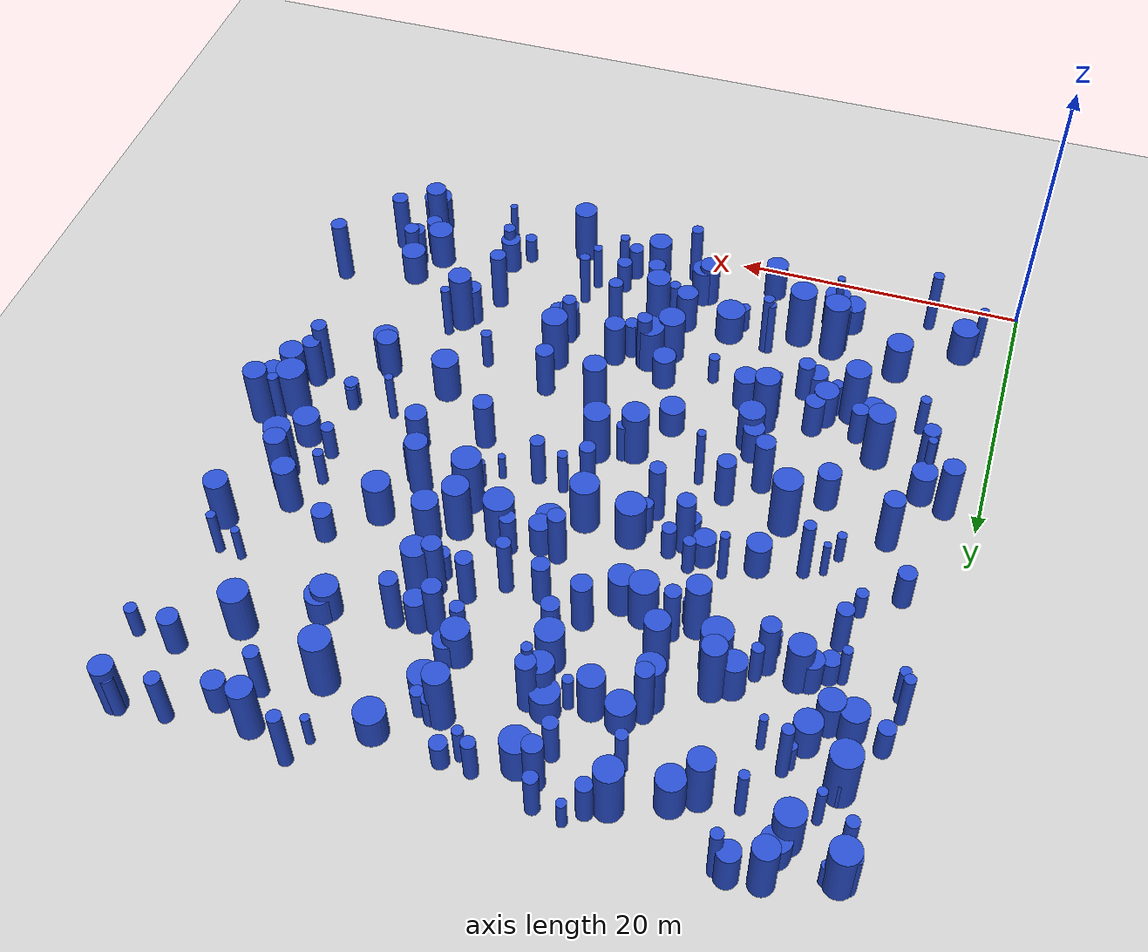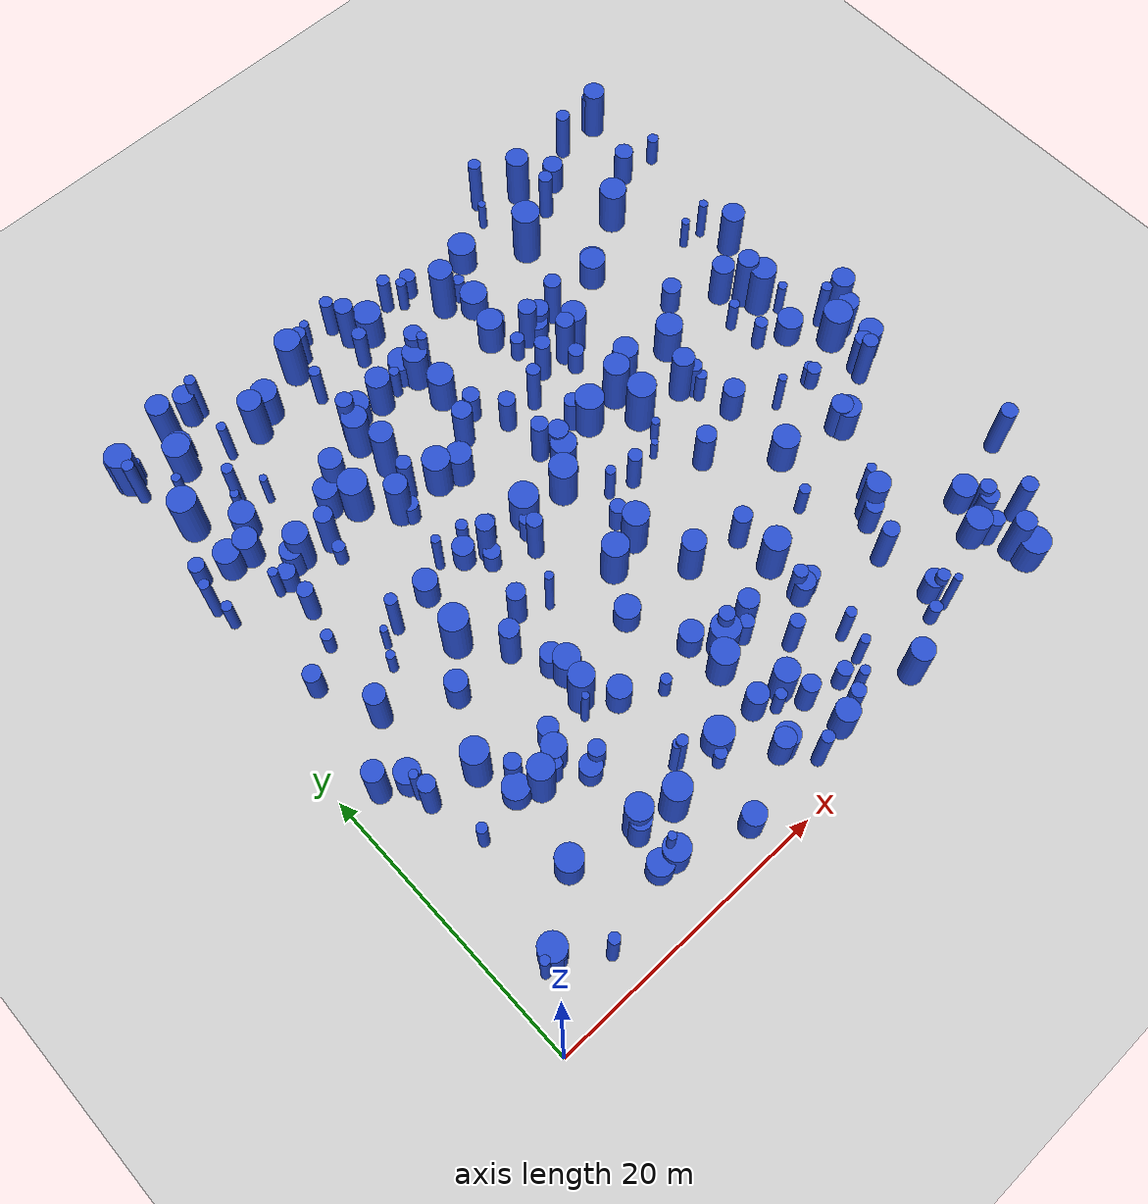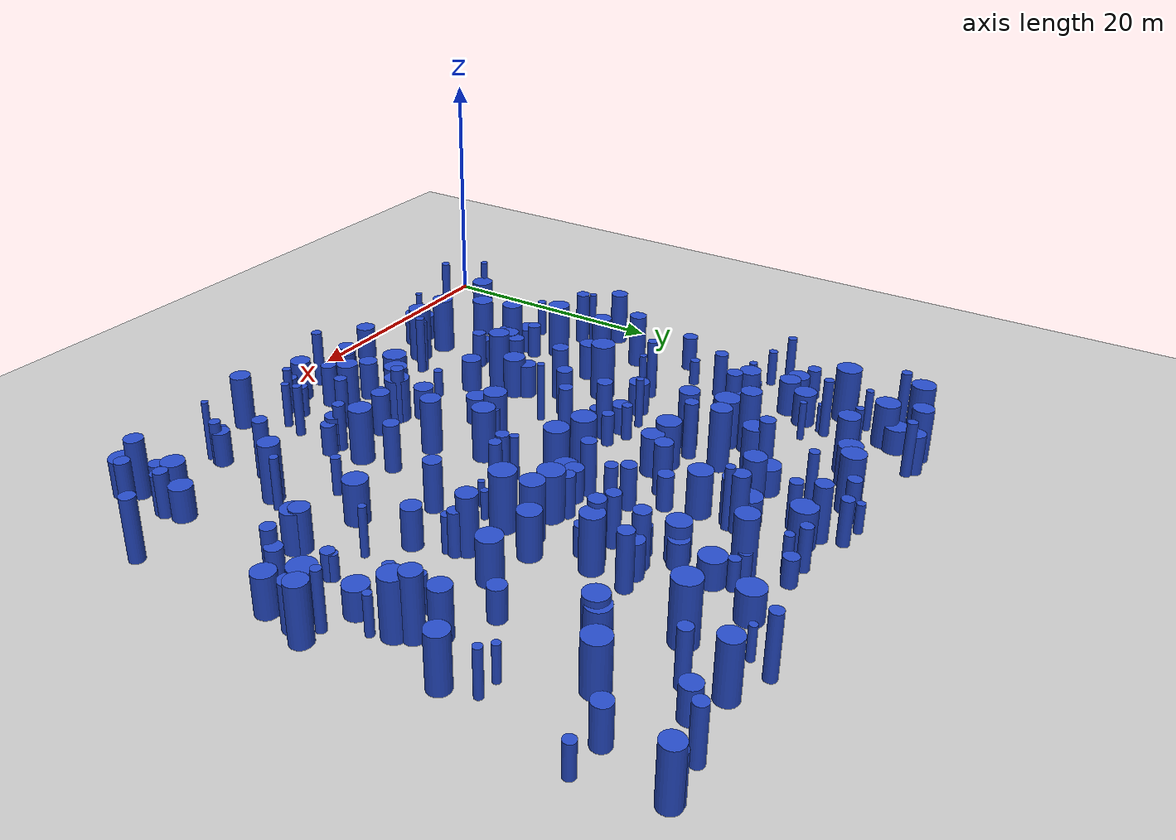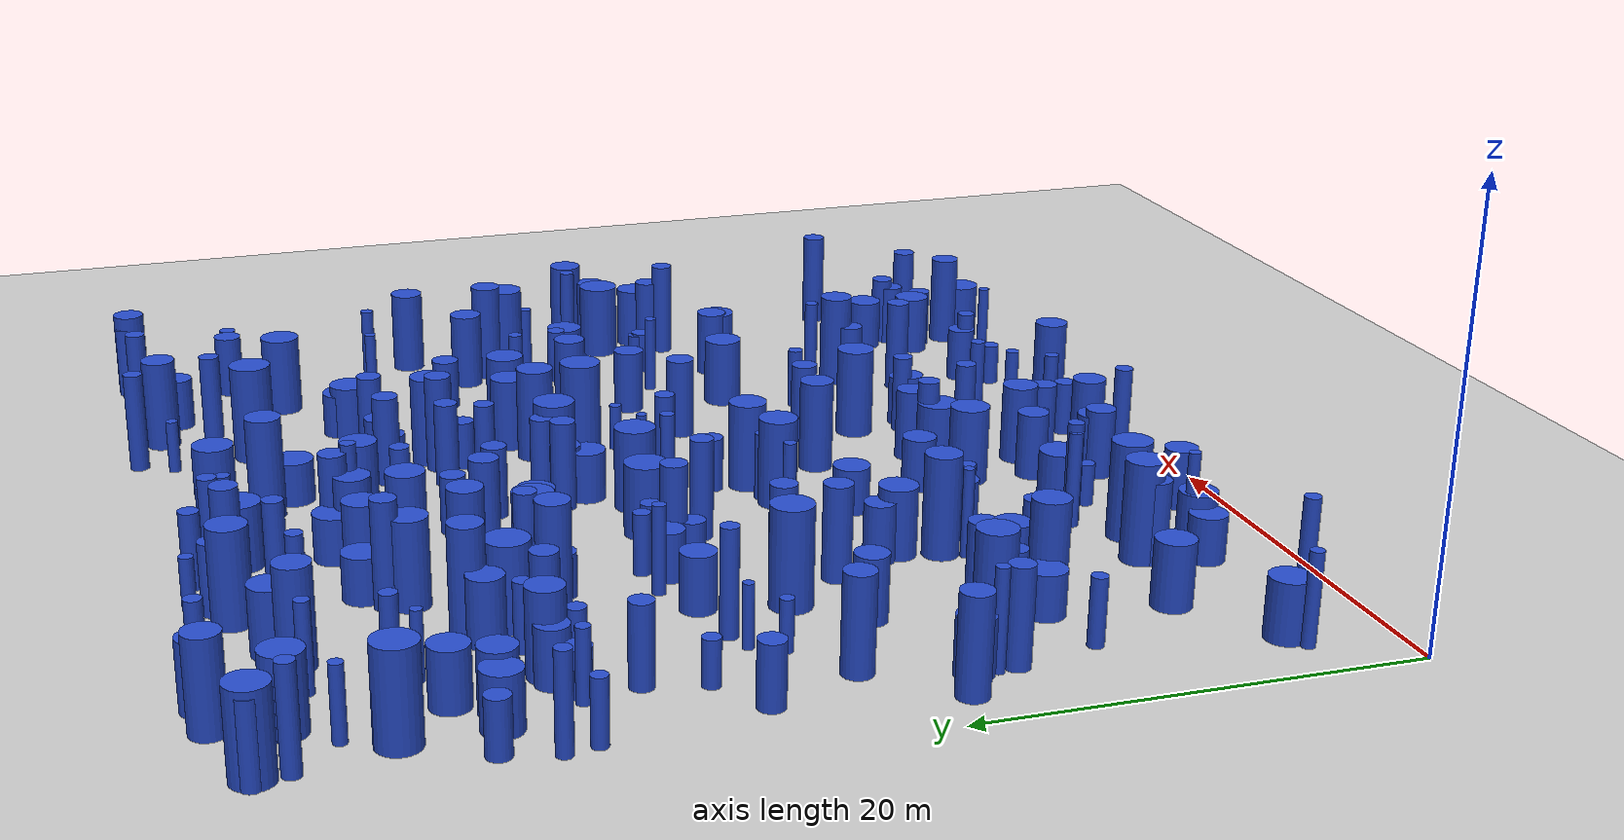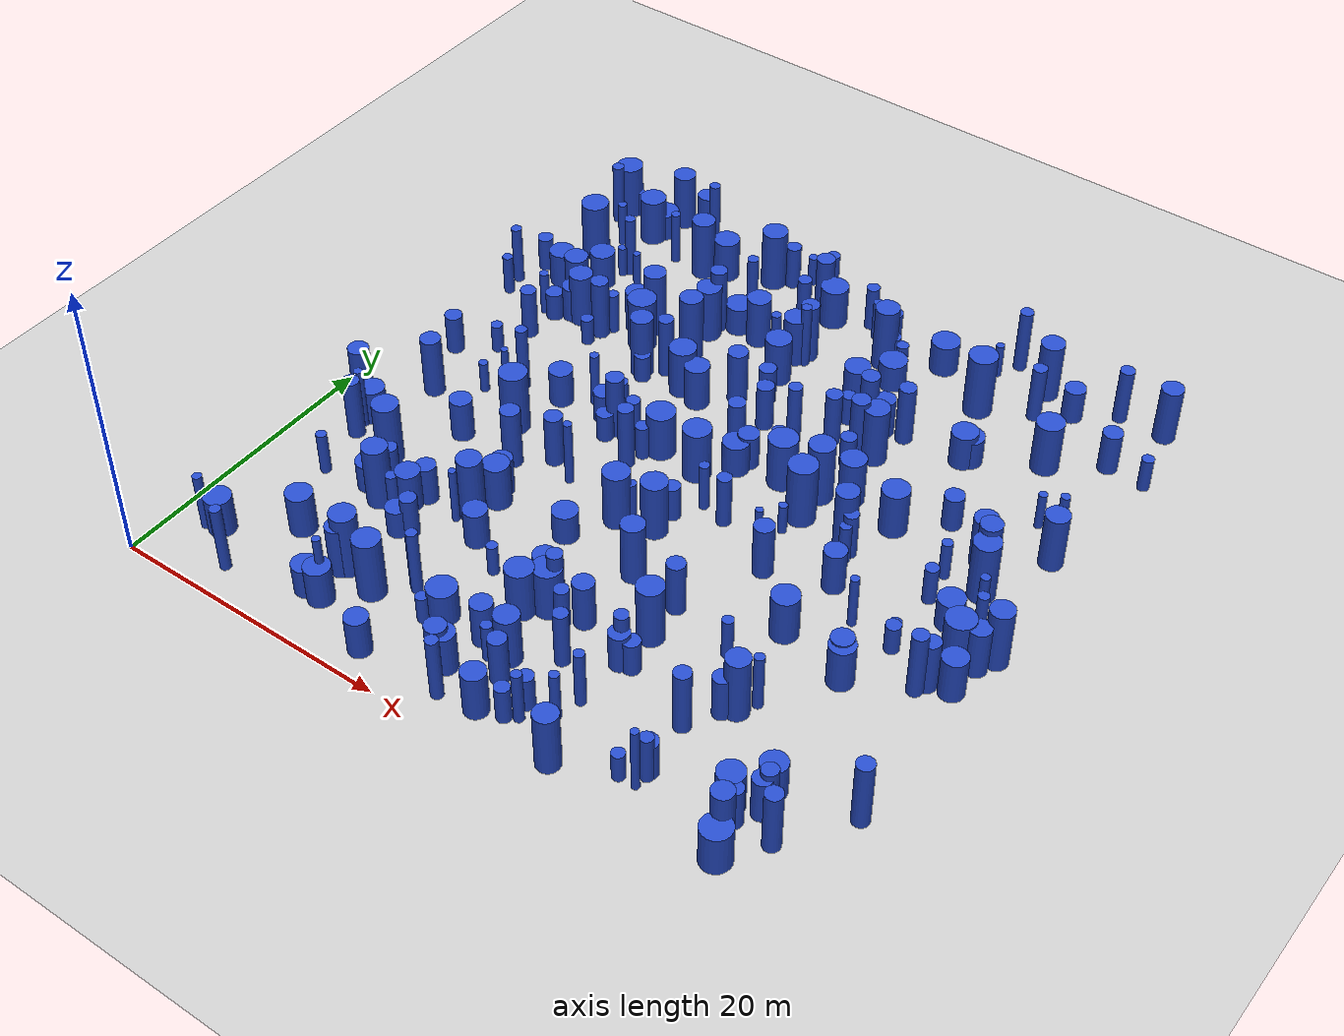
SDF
<sdf version="1.6">
 <world name="default">
  <light name="sun" type="directional">
   <pose>0 0 10 0 -0 0</pose>
   <diffuse>0.8 0.8 0.8 1</diffuse>
   <specular>0.1 0.1 0.1 1</specular>
   <attenuation>
    <range>1000</range>
    <constant>0.9</constant>
    <linear>0.01</linear>
    <quadratic>0.001</quadratic>
   </attenuation>
   <direction>-0.5 0.5 -1</direction>
  </light>
  <model name="ground_plane">
   <static>1</static>
   <link name="link">
    <collision name="collision">
     <geometry><plane><normal>0 0 1</normal><size>100 100</size></plane></geometry>
     <surface><friction><ode><mu>100</mu><mu2>50</mu2></ode></friction></surface>
    </collision>
    <visual name="visual">
     <cast_shadows>0</cast_shadows>
     <geometry><plane><normal>0 0 1</normal><size>100 100</size></plane></geometry>
     <material>
      <script><uri>file://media/materials/scripts/gazebo.material</uri><name>Gazebo/Grey</name></script>
     </material>
    </visual>
   </link>
  </model>
  <gravity>0 0 -9.8</gravity>
  <magnetic_field>6e-06 2.3e-05 -4.2e-05</magnetic_field>
  <atmosphere type="adiabatic"/>
  <physics name="default_physics" default="0" type="ode">
   <max_step_size>0.001</max_step_size>
   <real_time_factor>1</real_time_factor>
   <real_time_update_rate>1000</real_time_update_rate>
  </physics>
  <scene><ambient>0.4 0.4 0.4 1</ambient><background>0.7 0.7 0.7 1</background><shadows>1</shadows></scene>
  <spherical_coordinates>
   <surface_model>EARTH_WGS84</surface_model>
   <latitude_deg>0</latitude_deg>
   <longitude_deg>0</longitude_deg>
   <elevation>0</elevation>
   <heading_deg>0</heading_deg>
  </spherical_coordinates>
  <model name="0">
   <static>0</static>
   <link name="link">
    <inertial>
     <mass>2</mass>
     <inertia><ixx>2.34982</ixx><ixy>0</ixy><ixz>0</ixz><iyy>2.34982</iyy><iyz>0</iyz><izz>0.175341</izz></inertia>
    </inertial>
    <collision name="collision">
     <geometry><cylinder><length>3.68414</length><radius>0.418737</radius></cylinder></geometry>
     <surface><contact><collide_without_contact>1</collide_without_contact></contact></surface>
    </collision>
    <visual name="visual">
     <geometry><cylinder><length>3.68414</length><radius>0.418737</radius></cylinder></geometry>
     <material>
      <script><uri>file://media/materials/scripts/gazebo.material</uri><name>Gazebo/Blue</name></script>
     </material>
    </visual>
    <gravity>0</gravity>
   </link>
   <pose>22.4212 20.0822 1.84207 0 -0 0</pose>
  </model>
  <model name="1">
   <static>0</static>
   <link name="link">
    <inertial>
     <mass>2</mass>
     <inertia><ixx>1.42291</ixx><ixy>0</ixy><ixz>0</ixz><iyy>1.42291</iyy><iyz>0</iyz><izz>0.128584</izz></inertia>
    </inertial>
    <collision name="collision">
     <geometry><cylinder><length>2.85512</length><radius>0.358586</radius></cylinder></geometry>
     <surface><contact><collide_without_contact>1</collide_without_contact></contact></surface>
    </collision>
    <visual name="visual">
     <geometry><cylinder><length>2.85512</length><radius>0.358586</radius></cylinder></geometry>
     <material>
      <script><uri>file://media/materials/scripts/gazebo.material</uri><name>Gazebo/Blue</name></script>
     </material>
    </visual>
    <gravity>0</gravity>
   </link>
   <pose>41.7752 27.9235 1.42756 0 -0 0</pose>
  </model>
  <model name="2">
   <static>0</static>
   <link name="link">
    <inertial>
     <mass>2</mass>
     <inertia><ixx>3.7496</ixx><ixy>0</ixy><ixz>0</ixz><iyy>3.7496</iyy><iyz>0</iyz><izz>0.179017</izz></inertia>
    </inertial>
    <collision name="collision">
     <geometry><cylinder><length>4.68621</length><radius>0.423104</radius></cylinder></geometry>
     <surface><contact><collide_without_contact>1</collide_without_contact></contact></surface>
    </collision>
    <visual name="visual">
     <geometry><cylinder><length>4.68621</length><radius>0.423104</radius></cylinder></geometry>
     <material>
      <script><uri>file://media/materials/scripts/gazebo.material</uri><name>Gazebo/Blue</name></script>
     </material>
    </visual>
    <gravity>0</gravity>
   </link>
   <pose>23.1867 2.18453 2.3431 0 -0 0</pose>
  </model>
  <model name="3">
   <static>0</static>
   <link name="link">
    <inertial>
     <mass>2</mass>
     <inertia><ixx>1.32488</ixx><ixy>0</ixy><ixz>0</ixz><iyy>1.32488</iyy><iyz>0</iyz><izz>0.51786</izz></inertia>
    </inertial>
    <collision name="collision">
     <geometry><cylinder><length>2.52897</length><radius>0.719625</radius></cylinder></geometry>
     <surface><contact><collide_without_contact>1</collide_without_contact></contact></surface>
    </collision>
    <visual name="visual">
     <geometry><cylinder><length>2.52897</length><radius>0.719625</radius></cylinder></geometry>
     <material>
      <script><uri>file://media/materials/scripts/gazebo.material</uri><name>Gazebo/Blue</name></script>
     </material>
    </visual>
    <gravity>0</gravity>
   </link>
   <pose>40.9199 45.4642 1.26449 0 -0 0</pose>
  </model>
  <model name="4">
   <static>0</static>
   <link name="link">
    <inertial>
     <mass>2</mass>
     <inertia>
      <ixx>0.784851</ixx>
      <ixy>0</ixy>
      <ixz>0</ixz>
      <iyy>0.784851</iyy>
      <iyz>0</iyz>
      <izz>0.196081</izz>
     </inertia>
    </inertial>
    <collision name="collision">
     <geometry><cylinder><length>2.02999</length><radius>0.442811</radius></cylinder></geometry>
     <surface><contact><collide_without_contact>1</collide_without_contact></contact></surface>
    </collision>
    <visual name="visual">
     <geometry><cylinder><length>2.02999</length><radius>0.442811</radius></cylinder></geometry>
     <material>
      <script><uri>file://media/materials/scripts/gazebo.material</uri><name>Gazebo/Blue</name></script>
     </material>
    </visual>
    <gravity>0</gravity>
   </link>
   <pose>22.4216 3.87466 1.015 0 -0 0</pose>
  </model>
  <model name="5">
   <static>0</static>
   <link name="link">
    <inertial>
     <mass>2</mass>
     <inertia><ixx>1.19895</ixx><ixy>0</ixy><ixz>0</ixz><iyy>1.19895</iyy><iyz>0</iyz><izz>0.27551</izz></inertia>
    </inertial>
    <collision name="collision">
     <geometry><cylinder><length>2.52333</length><radius>0.52489</radius></cylinder></geometry>
     <surface><contact><collide_without_contact>1</collide_without_contact></contact></surface>
    </collision>
    <visual name="visual">
     <geometry><cylinder><length>2.52333</length><radius>0.52489</radius></cylinder></geometry>
     <material>
      <script><uri>file://media/materials/scripts/gazebo.material</uri><name>Gazebo/Blue</name></script>
     </material>
    </visual>
    <gravity>0</gravity>
   </link>
   <pose>27.8719 4.70569 1.26166 0 -0 0</pose>
  </model>
  <model name="6">
   <static>0</static>
   <link name="link">
    <inertial>
     <mass>2</mass>
     <inertia><ixx>1.37461</ixx><ixy>0</ixy><ixz>0</ixz><iyy>1.37461</iyy><iyz>0</iyz><izz>0.826308</izz></inertia>
    </inertial>
    <collision name="collision">
     <geometry><cylinder><length>2.40182</length><radius>0.909015</radius></cylinder></geometry>
     <surface><contact><collide_without_contact>1</collide_without_contact></contact></surface>
    </collision>
    <visual name="visual">
     <geometry><cylinder><length>2.40182</length><radius>0.909015</radius></cylinder></geometry>
     <material>
      <script><uri>file://media/materials/scripts/gazebo.material</uri><name>Gazebo/Blue</name></script>
     </material>
    </visual>
    <gravity>0</gravity>
   </link>
   <pose>25.9791 28.1484 1.20091 0 -0 0</pose>
  </model>
  <model name="7">
   <static>0</static>
   <link name="link">
    <inertial>
     <mass>2</mass>
     <inertia><ixx>1.55105</ixx><ixy>0</ixy><ixz>0</ixz><iyy>1.55105</iyy><iyz>0</iyz><izz>0.812849</izz></inertia>
    </inertial>
    <collision name="collision">
     <geometry><cylinder><length>2.62064</length><radius>0.901581</radius></cylinder></geometry>
     <surface><contact><collide_without_contact>1</collide_without_contact></contact></surface>
    </collision>
    <visual name="visual">
     <geometry><cylinder><length>2.62064</length><radius>0.901581</radius></cylinder></geometry>
     <material>
      <script><uri>file://media/materials/scripts/gazebo.material</uri><name>Gazebo/Blue</name></script>
     </material>
    </visual>
    <gravity>0</gravity>
   </link>
   <pose>37.3399 37.4414 1.31032 0 -0 0</pose>
  </model>
  <model name="8">
   <static>0</static>
   <link name="link">
    <inertial>
     <mass>2</mass>
     <inertia>
      <ixx>0.936811</ixx>
      <ixy>0</ixy>
      <ixz>0</ixz>
      <iyy>0.936811</iyy>
      <iyz>0</iyz>
      <izz>0.138882</izz>
     </inertia>
    </inertial>
    <collision name="collision">
     <geometry><cylinder><length>2.28128</length><radius>0.372668</radius></cylinder></geometry>
     <surface><contact><collide_without_contact>1</collide_without_contact></contact></surface>
    </collision>
    <visual name="visual">
     <geometry><cylinder><length>2.28128</length><radius>0.372668</radius></cylinder></geometry>
     <material>
      <script><uri>file://media/materials/scripts/gazebo.material</uri><name>Gazebo/Blue</name></script>
     </material>
    </visual>
    <gravity>0</gravity>
   </link>
   <pose>19.4248 11.7611 1.14064 0 -0 0</pose>
  </model>
  <model name="9">
   <static>0</static>
   <link name="link">
    <inertial>
     <mass>2</mass>
     <inertia><ixx>1.77191</ixx><ixy>0</ixy><ixz>0</ixz><iyy>1.77191</iyy><iyz>0</iyz><izz>0.691914</izz></inertia>
    </inertial>
    <collision name="collision">
     <geometry><cylinder><length>2.92502</length><radius>0.831814</radius></cylinder></geometry>
     <surface><contact><collide_without_contact>1</collide_without_contact></contact></surface>
    </collision>
    <visual name="visual">
     <geometry><cylinder><length>2.92502</length><radius>0.831814</radius></cylinder></geometry>
     <material>
      <script><uri>file://media/materials/scripts/gazebo.material</uri><name>Gazebo/Blue</name></script>
     </material>
    </visual>
    <gravity>0</gravity>
   </link>
   <pose>11.3721 13.2 1.46251 0 -0 0</pose>
  </model>
  <model name="10">
   <static>0</static>
   <link name="link">
    <inertial>
     <mass>2</mass>
     <inertia>
      <ixx>0.774725</ixx>
      <ixy>0</ixy>
      <ixz>0</ixz>
      <iyy>0.774725</iyy>
      <iyz>0</iyz>
      <izz>0.189763</izz>
     </inertia>
    </inertial>
    <collision name="collision">
     <geometry><cylinder><length>2.01967</length><radius>0.435618</radius></cylinder></geometry>
     <surface><contact><collide_without_contact>1</collide_without_contact></contact></surface>
    </collision>
    <visual name="visual">
     <geometry><cylinder><length>2.01967</length><radius>0.435618</radius></cylinder></geometry>
     <material>
      <script><uri>file://media/materials/scripts/gazebo.material</uri><name>Gazebo/Blue</name></script>
     </material>
    </visual>
    <gravity>0</gravity>
   </link>
   <pose>10.4125 32.5588 1.00983 0 -0 0</pose>
  </model>
  <model name="11">
   <static>0</static>
   <link name="link">
    <inertial>
     <mass>2</mass>
     <inertia><ixx>3.80874</ixx><ixy>0</ixy><ixz>0</ixz><iyy>3.80874</iyy><iyz>0</iyz><izz>0.499703</izz></inertia>
    </inertial>
    <collision name="collision">
     <geometry><cylinder><length>4.62097</length><radius>0.706896</radius></cylinder></geometry>
     <surface><contact><collide_without_contact>1</collide_without_contact></contact></surface>
    </collision>
    <visual name="visual">
     <geometry><cylinder><length>4.62097</length><radius>0.706896</radius></cylinder></geometry>
     <material>
      <script><uri>file://media/materials/scripts/gazebo.material</uri><name>Gazebo/Blue</name></script>
     </material>
    </visual>
    <gravity>0</gravity>
   </link>
   <pose>42.6481 3.33236 2.31048 0 -0 0</pose>
  </model>
  <model name="12">
   <static>0</static>
   <link name="link">
    <inertial>
     <mass>2</mass>
     <inertia>
      <ixx>3.57056</ixx>
      <ixy>0</ixy>
      <ixz>0</ixz>
      <iyy>3.57056</iyy>
      <iyz>0</iyz>
      <izz>0.0913782</izz>
     </inertia>
    </inertial>
    <collision name="collision">
     <geometry><cylinder><length>4.59883</length><radius>0.302288</radius></cylinder></geometry>
     <surface><contact><collide_without_contact>1</collide_without_contact></contact></surface>
    </collision>
    <visual name="visual">
     <geometry><cylinder><length>4.59883</length><radius>0.302288</radius></cylinder></geometry>
     <material>
      <script><uri>file://media/materials/scripts/gazebo.material</uri><name>Gazebo/Blue</name></script>
     </material>
    </visual>
    <gravity>0</gravity>
   </link>
   <pose>3.87306 17.0696 2.29941 0 -0 0</pose>
  </model>
  <model name="13">
   <static>0</static>
   <link name="link">
    <inertial>
     <mass>2</mass>
     <inertia><ixx>1.9703</ixx><ixy>0</ixy><ixz>0</ixz><iyy>1.9703</iyy><iyz>0</iyz><izz>0.2914</izz></inertia>
    </inertial>
    <collision name="collision">
     <geometry><cylinder><length>3.30871</length><radius>0.539815</radius></cylinder></geometry>
     <surface><contact><collide_without_contact>1</collide_without_contact></contact></surface>
    </collision>
    <visual name="visual">
     <geometry><cylinder><length>3.30871</length><radius>0.539815</radius></cylinder></geometry>
     <material>
      <script><uri>file://media/materials/scripts/gazebo.material</uri><name>Gazebo/Blue</name></script>
     </material>
    </visual>
    <gravity>0</gravity>
   </link>
   <pose>28.2282 29.745 1.65436 0 -0 0</pose>
  </model>
  <model name="14">
   <static>0</static>
   <link name="link">
    <inertial>
     <mass>2</mass>
     <inertia><ixx>1.37401</ixx><ixy>0</ixy><ixz>0</ixz><iyy>1.37401</iyy><iyz>0</iyz><izz>0.143411</izz></inertia>
    </inertial>
    <collision name="collision">
     <geometry><cylinder><length>2.79532</length><radius>0.378697</radius></cylinder></geometry>
     <surface><contact><collide_without_contact>1</collide_without_contact></contact></surface>
    </collision>
    <visual name="visual">
     <geometry><cylinder><length>2.79532</length><radius>0.378697</radius></cylinder></geometry>
     <material>
      <script><uri>file://media/materials/scripts/gazebo.material</uri><name>Gazebo/Blue</name></script>
     </material>
    </visual>
    <gravity>0</gravity>
   </link>
   <pose>23.7113 6.20723 1.39766 0 -0 0</pose>
  </model>
  <model name="15">
   <static>0</static>
   <link name="link">
    <inertial>
     <mass>2</mass>
     <inertia><ixx>1.15166</ixx><ixy>0</ixy><ixz>0</ixz><iyy>1.15166</iyy><iyz>0</iyz><izz>0.803615</izz></inertia>
    </inertial>
    <collision name="collision">
     <geometry><cylinder><length>2.12111</length><radius>0.896446</radius></cylinder></geometry>
     <surface><contact><collide_without_contact>1</collide_without_contact></contact></surface>
    </collision>
    <visual name="visual">
     <geometry><cylinder><length>2.12111</length><radius>0.896446</radius></cylinder></geometry>
     <material>
      <script><uri>file://media/materials/scripts/gazebo.material</uri><name>Gazebo/Blue</name></script>
     </material>
    </visual>
    <gravity>0</gravity>
   </link>
   <pose>8.16995 13.0512 1.06056 0 -0 0</pose>
  </model>
  <model name="16">
   <static>0</static>
   <link name="link">
    <inertial>
     <mass>2</mass>
     <inertia>
      <ixx>0.892268</ixx>
      <ixy>0</ixy>
      <ixz>0</ixz>
      <iyy>0.892268</iyy>
      <iyz>0</iyz>
      <izz>0.347311</izz>
     </inertia>
    </inertial>
    <collision name="collision">
     <geometry><cylinder><length>2.07646</length><radius>0.589331</radius></cylinder></geometry>
     <surface><contact><collide_without_contact>1</collide_without_contact></contact></surface>
    </collision>
    <visual name="visual">
     <geometry><cylinder><length>2.07646</length><radius>0.589331</radius></cylinder></geometry>
     <material>
      <script><uri>file://media/materials/scripts/gazebo.material</uri><name>Gazebo/Blue</name></script>
     </material>
    </visual>
    <gravity>0</gravity>
   </link>
   <pose>17.3559 25.5947 1.03823 0 -0 0</pose>
  </model>
  <model name="17">
   <static>0</static>
   <link name="link">
    <inertial>
     <mass>2</mass>
     <inertia><ixx>1.53515</ixx><ixy>0</ixy><ixz>0</ixz><iyy>1.53515</iyy><iyz>0</iyz><izz>0.667989</izz></inertia>
    </inertial>
    <collision name="collision">
     <geometry><cylinder><length>2.68458</length><radius>0.817306</radius></cylinder></geometry>
     <surface><contact><collide_without_contact>1</collide_without_contact></contact></surface>
    </collision>
    <visual name="visual">
     <geometry><cylinder><length>2.68458</length><radius>0.817306</radius></cylinder></geometry>
     <material>
      <script><uri>file://media/materials/scripts/gazebo.material</uri><name>Gazebo/Blue</name></script>
     </material>
    </visual>
    <gravity>0</gravity>
   </link>
   <pose>12.7985 26.728 1.34229 0 -0 0</pose>
  </model>
  <model name="18">
   <static>0</static>
   <link name="link">
    <inertial>
     <mass>2</mass>
     <inertia>
      <ixx>0.755053</ixx>
      <ixy>0</ixy>
      <ixz>0</ixz>
      <iyy>0.755053</iyy>
      <iyz>0</iyz>
      <izz>0.161134</izz>
     </inertia>
    </inertial>
    <collision name="collision">
     <geometry><cylinder><length>2.01169</length><radius>0.401415</radius></cylinder></geometry>
     <surface><contact><collide_without_contact>1</collide_without_contact></contact></surface>
    </collision>
    <visual name="visual">
     <geometry><cylinder><length>2.01169</length><radius>0.401415</radius></cylinder></geometry>
     <material>
      <script><uri>file://media/materials/scripts/gazebo.material</uri><name>Gazebo/Blue</name></script>
     </material>
    </visual>
    <gravity>0</gravity>
   </link>
   <pose>42.3675 21.2109 1.00585 0 -0 0</pose>
  </model>
  <model name="19">
   <static>0</static>
   <link name="link">
    <inertial>
     <mass>2</mass>
     <inertia><ixx>3.44669</ixx><ixy>0</ixy><ixz>0</ixz><iyy>3.44669</iyy><iyz>0</iyz><izz>0.34216</izz></inertia>
    </inertial>
    <collision name="collision">
     <geometry><cylinder><length>4.43325</length><radius>0.584945</radius></cylinder></geometry>
     <surface><contact><collide_without_contact>1</collide_without_contact></contact></surface>
    </collision>
    <visual name="visual">
     <geometry><cylinder><length>4.43325</length><radius>0.584945</radius></cylinder></geometry>
     <material>
      <script><uri>file://media/materials/scripts/gazebo.material</uri><name>Gazebo/Blue</name></script>
     </material>
    </visual>
    <gravity>0</gravity>
   </link>
   <pose>33.1585 37.0156 2.21662 0 -0 0</pose>
  </model>
  <model name="20">
   <static>0</static>
   <link name="link">
    <inertial>
     <mass>2</mass>
     <inertia><ixx>2.14927</ixx><ixy>0</ixy><ixz>0</ixz><iyy>2.14927</iyy><iyz>0</iyz><izz>0.10024</izz></inertia>
    </inertial>
    <collision name="collision">
     <geometry><cylinder><length>3.54893</length><radius>0.316606</radius></cylinder></geometry>
     <surface><contact><collide_without_contact>1</collide_without_contact></contact></surface>
    </collision>
    <visual name="visual">
     <geometry><cylinder><length>3.54893</length><radius>0.316606</radius></cylinder></geometry>
     <material>
      <script><uri>file://media/materials/scripts/gazebo.material</uri><name>Gazebo/Blue</name></script>
     </material>
    </visual>
    <gravity>0</gravity>
   </link>
   <pose>45.8173 35.0316 1.77447 0 -0 0</pose>
  </model>
  <model name="21">
   <static>0</static>
   <link name="link">
    <inertial>
     <mass>2</mass>
     <inertia><ixx>2.07639</ixx><ixy>0</ixy><ixz>0</ixz><iyy>2.07639</iyy><iyz>0</iyz><izz>0.241004</izz></inertia>
    </inertial>
    <collision name="collision">
     <geometry><cylinder><length>3.42569</length><radius>0.490922</radius></cylinder></geometry>
     <surface><contact><collide_without_contact>1</collide_without_contact></contact></surface>
    </collision>
    <visual name="visual">
     <geometry><cylinder><length>3.42569</length><radius>0.490922</radius></cylinder></geometry>
     <material>
      <script><uri>file://media/materials/scripts/gazebo.material</uri><name>Gazebo/Blue</name></script>
     </material>
    </visual>
    <gravity>0</gravity>
   </link>
   <pose>36.0554 26.0454 1.71284 0 -0 0</pose>
  </model>
  <model name="22">
   <static>0</static>
   <link name="link">
    <inertial>
     <mass>2</mass>
     <inertia><ixx>2.26913</ixx><ixy>0</ixy><ixz>0</ixz><iyy>2.26913</iyy><iyz>0</iyz><izz>0.505011</izz></inertia>
    </inertial>
    <collision name="collision">
     <geometry><cylinder><length>3.47847</length><radius>0.710641</radius></cylinder></geometry>
     <surface><contact><collide_without_contact>1</collide_without_contact></contact></surface>
    </collision>
    <visual name="visual">
     <geometry><cylinder><length>3.47847</length><radius>0.710641</radius></cylinder></geometry>
     <material>
      <script><uri>file://media/materials/scripts/gazebo.material</uri><name>Gazebo/Blue</name></script>
     </material>
    </visual>
    <gravity>0</gravity>
   </link>
   <pose>26.527 11.7667 1.73924 0 -0 0</pose>
  </model>
  <model name="23">
   <static>0</static>
   <link name="link">
    <inertial>
     <mass>2</mass>
     <inertia><ixx>2.13264</ixx><ixy>0</ixy><ixz>0</ixz><iyy>2.13264</iyy><iyz>0</iyz><izz>0.34742</izz></inertia>
    </inertial>
    <collision name="collision">
     <geometry><cylinder><length>3.42835</length><radius>0.589423</radius></cylinder></geometry>
     <surface><contact><collide_without_contact>1</collide_without_contact></contact></surface>
    </collision>
    <visual name="visual">
     <geometry><cylinder><length>3.42835</length><radius>0.589423</radius></cylinder></geometry>
     <material>
      <script><uri>file://media/materials/scripts/gazebo.material</uri><name>Gazebo/Blue</name></script>
     </material>
    </visual>
    <gravity>0</gravity>
   </link>
   <pose>25.0737 32.6969 1.71417 0 -0 0</pose>
  </model>
  <model name="24">
   <static>0</static>
   <link name="link">
    <inertial>
     <mass>2</mass>
     <inertia><ixx>3.77941</ixx><ixy>0</ixy><ixz>0</ixz><iyy>3.77941</iyy><iyz>0</iyz><izz>0.148371</izz></inertia>
    </inertial>
    <collision name="collision">
     <geometry><cylinder><length>4.71502</length><radius>0.38519</radius></cylinder></geometry>
     <surface><contact><collide_without_contact>1</collide_without_contact></contact></surface>
    </collision>
    <visual name="visual">
     <geometry><cylinder><length>4.71502</length><radius>0.38519</radius></cylinder></geometry>
     <material>
      <script><uri>file://media/materials/scripts/gazebo.material</uri><name>Gazebo/Blue</name></script>
     </material>
    </visual>
    <gravity>0</gravity>
   </link>
   <pose>8.12711 40.4296 2.35751 0 -0 0</pose>
  </model>
  <model name="25">
   <static>0</static>
   <link name="link">
    <inertial>
     <mass>2</mass>
     <inertia><ixx>3.99631</ixx><ixy>0</ixy><ixz>0</ixz><iyy>3.99631</iyy><iyz>0</iyz><izz>0.280628</izz></inertia>
    </inertial>
    <collision name="collision">
     <geometry><cylinder><length>4.80998</length><radius>0.529744</radius></cylinder></geometry>
     <surface><contact><collide_without_contact>1</collide_without_contact></contact></surface>
    </collision>
    <visual name="visual">
     <geometry><cylinder><length>4.80998</length><radius>0.529744</radius></cylinder></geometry>
     <material>
      <script><uri>file://media/materials/scripts/gazebo.material</uri><name>Gazebo/Blue</name></script>
     </material>
    </visual>
    <gravity>0</gravity>
   </link>
   <pose>45.2657 18.9256 2.40499 0 -0 0</pose>
  </model>
  <model name="26">
   <static>0</static>
   <link name="link">
    <inertial>
     <mass>2</mass>
     <inertia><ixx>2.66427</ixx><ixy>0</ixy><ixz>0</ixz><iyy>2.66427</iyy><iyz>0</iyz><izz>0.704227</izz></inertia>
    </inertial>
    <collision name="collision">
     <geometry><cylinder><length>3.72464</length><radius>0.839182</radius></cylinder></geometry>
     <surface><contact><collide_without_contact>1</collide_without_contact></contact></surface>
    </collision>
    <visual name="visual">
     <geometry><cylinder><length>3.72464</length><radius>0.839182</radius></cylinder></geometry>
     <material>
      <script><uri>file://media/materials/scripts/gazebo.material</uri><name>Gazebo/Blue</name></script>
     </material>
    </visual>
    <gravity>0</gravity>
   </link>
   <pose>19.7542 39.6332 1.86232 0 -0 0</pose>
  </model>
  <model name="27">
   <static>0</static>
   <link name="link">
    <inertial>
     <mass>2</mass>
     <inertia><ixx>1.44612</ixx><ixy>0</ixy><ixz>0</ixz><iyy>1.44612</iyy><iyz>0</iyz><izz>0.468528</izz></inertia>
    </inertial>
    <collision name="collision">
     <geometry><cylinder><length>2.69651</length><radius>0.684491</radius></cylinder></geometry>
     <surface><contact><collide_without_contact>1</collide_without_contact></contact></surface>
    </collision>
    <visual name="visual">
     <geometry><cylinder><length>2.69651</length><radius>0.684491</radius></cylinder></geometry>
     <material>
      <script><uri>file://media/materials/scripts/gazebo.material</uri><name>Gazebo/Blue</name></script>
     </material>
    </visual>
    <gravity>0</gravity>
   </link>
   <pose>36.4301 4.9127 1.34825 0 -0 0</pose>
  </model>
  <model name="28">
   <static>0</static>
   <link name="link">
    <inertial>
     <mass>2</mass>
     <inertia><ixx>3.02201</ixx><ixy>0</ixy><ixz>0</ixz><iyy>3.02201</iyy><iyz>0</iyz><izz>0.698976</izz></inertia>
    </inertial>
    <collision name="collision">
     <geometry><cylinder><length>4.00439</length><radius>0.836048</radius></cylinder></geometry>
     <surface><contact><collide_without_contact>1</collide_without_contact></contact></surface>
    </collision>
    <visual name="visual">
     <geometry><cylinder><length>4.00439</length><radius>0.836048</radius></cylinder></geometry>
     <material>
      <script><uri>file://media/materials/scripts/gazebo.material</uri><name>Gazebo/Blue</name></script>
     </material>
    </visual>
    <gravity>0</gravity>
   </link>
   <pose>8.59451 34.2473 2.0022 0 -0 0</pose>
  </model>
  <model name="29">
   <static>0</static>
   <link name="link">
    <inertial>
     <mass>2</mass>
     <inertia>
      <ixx>0.975002</ixx>
      <ixy>0</ixy>
      <ixz>0</ixz>
      <iyy>0.975002</iyy>
      <iyz>0</iyz>
      <izz>0.174571</izz>
     </inertia>
    </inertial>
    <collision name="collision">
     <geometry><cylinder><length>2.30788</length><radius>0.417817</radius></cylinder></geometry>
     <surface><contact><collide_without_contact>1</collide_without_contact></contact></surface>
    </collision>
    <visual name="visual">
     <geometry><cylinder><length>2.30788</length><radius>0.417817</radius></cylinder></geometry>
     <material>
      <script><uri>file://media/materials/scripts/gazebo.material</uri><name>Gazebo/Blue</name></script>
     </material>
    </visual>
    <gravity>0</gravity>
   </link>
   <pose>29.3907 42.6499 1.15394 0 -0 0</pose>
  </model>
  <model name="30">
   <static>0</static>
   <link name="link">
    <inertial>
     <mass>2</mass>
     <inertia><ixx>3.44762</ixx><ixy>0</ixy><ixz>0</ixz><iyy>3.44762</iyy><iyz>0</iyz><izz>0.103691</izz></inertia>
    </inertial>
    <collision name="collision">
     <geometry><cylinder><length>4.51383</length><radius>0.322011</radius></cylinder></geometry>
     <surface><contact><collide_without_contact>1</collide_without_contact></contact></surface>
    </collision>
    <visual name="visual">
     <geometry><cylinder><length>4.51383</length><radius>0.322011</radius></cylinder></geometry>
     <material>
      <script><uri>file://media/materials/scripts/gazebo.material</uri><name>Gazebo/Blue</name></script>
     </material>
    </visual>
    <gravity>0</gravity>
   </link>
   <pose>16.4467 7.91767 2.25692 0 -0 0</pose>
  </model>
  <model name="31">
   <static>0</static>
   <link name="link">
    <inertial>
     <mass>2</mass>
     <inertia><ixx>2.57392</ixx><ixy>0</ixy><ixz>0</ixz><iyy>2.57392</iyy><iyz>0</iyz><izz>0.71737</izz></inertia>
    </inertial>
    <collision name="collision">
     <geometry><cylinder><length>3.64574</length><radius>0.846977</radius></cylinder></geometry>
     <surface><contact><collide_without_contact>1</collide_without_contact></contact></surface>
    </collision>
    <visual name="visual">
     <geometry><cylinder><length>3.64574</length><radius>0.846977</radius></cylinder></geometry>
     <material>
      <script><uri>file://media/materials/scripts/gazebo.material</uri><name>Gazebo/Blue</name></script>
     </material>
    </visual>
    <gravity>0</gravity>
   </link>
   <pose>22.8649 39.5204 1.82287 0 -0 0</pose>
  </model>
  <model name="32">
   <static>0</static>
   <link name="link">
    <inertial>
     <mass>2</mass>
     <inertia><ixx>4.32118</ixx><ixy>0</ixy><ixz>0</ixz><iyy>4.32118</iyy><iyz>0</iyz><izz>0.545109</izz></inertia>
    </inertial>
    <collision name="collision">
     <geometry><cylinder><length>4.92867</length><radius>0.738315</radius></cylinder></geometry>
     <surface><contact><collide_without_contact>1</collide_without_contact></contact></surface>
    </collision>
    <visual name="visual">
     <geometry><cylinder><length>4.92867</length><radius>0.738315</radius></cylinder></geometry>
     <material>
      <script><uri>file://media/materials/scripts/gazebo.material</uri><name>Gazebo/Blue</name></script>
     </material>
    </visual>
    <gravity>0</gravity>
   </link>
   <pose>43.9927 28.992 2.46433 0 -0 0</pose>
  </model>
  <model name="33">
   <static>0</static>
   <link name="link">
    <inertial>
     <mass>2</mass>
     <inertia><ixx>1.18232</ixx><ixy>0</ixy><ixz>0</ixz><iyy>1.18232</iyy><iyz>0</iyz><izz>0.933247</izz></inertia>
    </inertial>
    <collision name="collision">
     <geometry><cylinder><length>2.07224</length><radius>0.966047</radius></cylinder></geometry>
     <surface><contact><collide_without_contact>1</collide_without_contact></contact></surface>
    </collision>
    <visual name="visual">
     <geometry><cylinder><length>2.07224</length><radius>0.966047</radius></cylinder></geometry>
     <material>
      <script><uri>file://media/materials/scripts/gazebo.material</uri><name>Gazebo/Blue</name></script>
     </material>
    </visual>
    <gravity>0</gravity>
   </link>
   <pose>29.552 41.2584 1.03612 0 -0 0</pose>
  </model>
  <model name="34">
   <static>0</static>
   <link name="link">
    <inertial>
     <mass>2</mass>
     <inertia><ixx>3.25336</ixx><ixy>0</ixy><ixz>0</ixz><iyy>3.25336</iyy><iyz>0</iyz><izz>0.568015</izz></inertia>
    </inertial>
    <collision name="collision">
     <geometry><cylinder><length>4.22092</length><radius>0.753668</radius></cylinder></geometry>
     <surface><contact><collide_without_contact>1</collide_without_contact></contact></surface>
    </collision>
    <visual name="visual">
     <geometry><cylinder><length>4.22092</length><radius>0.753668</radius></cylinder></geometry>
     <material>
      <script><uri>file://media/materials/scripts/gazebo.material</uri><name>Gazebo/Blue</name></script>
     </material>
    </visual>
    <gravity>0</gravity>
   </link>
   <pose>46.7338 47.3062 2.11046 0 -0 0</pose>
  </model>
  <model name="35">
   <static>0</static>
   <link name="link">
    <inertial>
     <mass>2</mass>
     <inertia>
      <ixx>1.30378</ixx>
      <ixy>0</ixy>
      <ixz>0</ixz>
      <iyy>1.30378</iyy>
      <iyz>0</iyz>
      <izz>0.0818979</izz>
     </inertia>
    </inertial>
    <collision name="collision">
     <geometry><cylinder><length>2.75264</length><radius>0.286178</radius></cylinder></geometry>
     <surface><contact><collide_without_contact>1</collide_without_contact></contact></surface>
    </collision>
    <visual name="visual">
     <geometry><cylinder><length>2.75264</length><radius>0.286178</radius></cylinder></geometry>
     <material>
      <script><uri>file://media/materials/scripts/gazebo.material</uri><name>Gazebo/Blue</name></script>
     </material>
    </visual>
    <gravity>0</gravity>
   </link>
   <pose>44.2744 35.1639 1.37632 0 -0 0</pose>
  </model>
  <model name="36">
   <static>0</static>
   <link name="link">
    <inertial>
     <mass>2</mass>
     <inertia><ixx>3.51883</ixx><ixy>0</ixy><ixz>0</ixz><iyy>3.51883</iyy><iyz>0</iyz><izz>0.320908</izz></inertia>
    </inertial>
    <collision name="collision">
     <geometry><cylinder><length>4.4889</length><radius>0.566488</radius></cylinder></geometry>
     <surface><contact><collide_without_contact>1</collide_without_contact></contact></surface>
    </collision>
    <visual name="visual">
     <geometry><cylinder><length>4.4889</length><radius>0.566488</radius></cylinder></geometry>
     <material>
      <script><uri>file://media/materials/scripts/gazebo.material</uri><name>Gazebo/Blue</name></script>
     </material>
    </visual>
    <gravity>0</gravity>
   </link>
   <pose>44.884 4.86893 2.24445 0 -0 0</pose>
  </model>
  <model name="37">
   <static>0</static>
   <link name="link">
    <inertial>
     <mass>2</mass>
     <inertia><ixx>3.04398</ixx><ixy>0</ixy><ixz>0</ixz><iyy>3.04398</iyy><iyz>0</iyz><izz>0.92073</izz></inertia>
    </inertial>
    <collision name="collision">
     <geometry><cylinder><length>3.93722</length><radius>0.959547</radius></cylinder></geometry>
     <surface><contact><collide_without_contact>1</collide_without_contact></contact></surface>
    </collision>
    <visual name="visual">
     <geometry><cylinder><length>3.93722</length><radius>0.959547</radius></cylinder></geometry>
     <material>
      <script><uri>file://media/materials/scripts/gazebo.material</uri><name>Gazebo/Blue</name></script>
     </material>
    </visual>
    <gravity>0</gravity>
   </link>
   <pose>24.2494 26.2747 1.96861 0 -0 0</pose>
  </model>
  <model name="38">
   <static>0</static>
   <link name="link">
    <inertial>
     <mass>2</mass>
     <inertia><ixx>1.02896</ixx><ixy>0</ixy><ixz>0</ixz><iyy>1.02896</iyy><iyz>0</iyz><izz>0.550959</izz></inertia>
    </inertial>
    <collision name="collision">
     <geometry><cylinder><length>2.12623</length><radius>0.742266</radius></cylinder></geometry>
     <surface><contact><collide_without_contact>1</collide_without_contact></contact></surface>
    </collision>
    <visual name="visual">
     <geometry><cylinder><length>2.12623</length><radius>0.742266</radius></cylinder></geometry>
     <material>
      <script><uri>file://media/materials/scripts/gazebo.material</uri><name>Gazebo/Blue</name></script>
     </material>
    </visual>
    <gravity>0</gravity>
   </link>
   <pose>29.1701 38.6962 1.06311 0 -0 0</pose>
  </model>
  <model name="39">
   <static>0</static>
   <link name="link">
    <inertial>
     <mass>2</mass>
     <inertia><ixx>2.1303</ixx><ixy>0</ixy><ixz>0</ixz><iyy>2.1303</iyy><iyz>0</iyz><izz>0.504175</izz></inertia>
    </inertial>
    <collision name="collision">
     <geometry><cylinder><length>3.35697</length><radius>0.710052</radius></cylinder></geometry>
     <surface><contact><collide_without_contact>1</collide_without_contact></contact></surface>
    </collision>
    <visual name="visual">
     <geometry><cylinder><length>3.35697</length><radius>0.710052</radius></cylinder></geometry>
     <material>
      <script><uri>file://media/materials/scripts/gazebo.material</uri><name>Gazebo/Blue</name></script>
     </material>
    </visual>
    <gravity>0</gravity>
   </link>
   <pose>21.7132 4.03501 1.67849 0 -0 0</pose>
  </model>
  <model name="40">
   <static>0</static>
   <link name="link">
    <inertial>
     <mass>2</mass>
     <inertia><ixx>1.56214</ixx><ixy>0</ixy><ixz>0</ixz><iyy>1.56214</iyy><iyz>0</iyz><izz>0.523114</izz></inertia>
    </inertial>
    <collision name="collision">
     <geometry><cylinder><length>2.79347</length><radius>0.723266</radius></cylinder></geometry>
     <surface><contact><collide_without_contact>1</collide_without_contact></contact></surface>
    </collision>
    <visual name="visual">
     <geometry><cylinder><length>2.79347</length><radius>0.723266</radius></cylinder></geometry>
     <material>
      <script><uri>file://media/materials/scripts/gazebo.material</uri><name>Gazebo/Blue</name></script>
     </material>
    </visual>
    <gravity>0</gravity>
   </link>
   <pose>15.2742 17.7058 1.39674 0 -0 0</pose>
  </model>
  <model name="41">
   <static>0</static>
   <link name="link">
    <inertial>
     <mass>2</mass>
     <inertia><ixx>2.43129</ixx><ixy>0</ixy><ixz>0</ixz><iyy>2.43129</iyy><iyz>0</iyz><izz>0.15694</izz></inertia>
    </inertial>
    <collision name="collision">
     <geometry><cylinder><length>3.75725</length><radius>0.396156</radius></cylinder></geometry>
     <surface><contact><collide_without_contact>1</collide_without_contact></contact></surface>
    </collision>
    <visual name="visual">
     <geometry><cylinder><length>3.75725</length><radius>0.396156</radius></cylinder></geometry>
     <material>
      <script><uri>file://media/materials/scripts/gazebo.material</uri><name>Gazebo/Blue</name></script>
     </material>
    </visual>
    <gravity>0</gravity>
   </link>
   <pose>16.9986 42.8262 1.87863 0 -0 0</pose>
  </model>
  <model name="42">
   <static>0</static>
   <link name="link">
    <inertial>
     <mass>2</mass>
     <inertia><ixx>3.9345</ixx><ixy>0</ixy><ixz>0</ixz><iyy>3.9345</iyy><iyz>0</iyz><izz>0.817818</izz></inertia>
    </inertial>
    <collision name="collision">
     <geometry><cylinder><length>4.5993</length><radius>0.904333</radius></cylinder></geometry>
     <surface><contact><collide_without_contact>1</collide_without_contact></contact></surface>
    </collision>
    <visual name="visual">
     <geometry><cylinder><length>4.5993</length><radius>0.904333</radius></cylinder></geometry>
     <material>
      <script><uri>file://media/materials/scripts/gazebo.material</uri><name>Gazebo/Blue</name></script>
     </material>
    </visual>
    <gravity>0</gravity>
   </link>
   <pose>7.3963 15.7324 2.29965 0 -0 0</pose>
  </model>
  <model name="43">
   <static>0</static>
   <link name="link">
    <inertial>
     <mass>2</mass>
     <inertia>
      <ixx>3.81452</ixx>
      <ixy>0</ixy>
      <ixz>0</ixz>
      <iyy>3.81452</iyy>
      <iyz>0</iyz>
      <izz>0.0700208</izz>
     </inertia>
    </inertial>
    <collision name="collision">
     <geometry><cylinder><length>4.76204</length><radius>0.264614</radius></cylinder></geometry>
     <surface><contact><collide_without_contact>1</collide_without_contact></contact></surface>
    </collision>
    <visual name="visual">
     <geometry><cylinder><length>4.76204</length><radius>0.264614</radius></cylinder></geometry>
     <material>
      <script><uri>file://media/materials/scripts/gazebo.material</uri><name>Gazebo/Blue</name></script>
     </material>
    </visual>
    <gravity>0</gravity>
   </link>
   <pose>36.5145 3.67072 2.38102 0 -0 0</pose>
  </model>
  <model name="44">
   <static>0</static>
   <link name="link">
    <inertial>
     <mass>2</mass>
     <inertia><ixx>1.89444</ixx><ixy>0</ixy><ixz>0</ixz><iyy>1.89444</iyy><iyz>0</iyz><izz>0.104986</izz></inertia>
    </inertial>
    <collision name="collision">
     <geometry><cylinder><length>3.32441</length><radius>0.324016</radius></cylinder></geometry>
     <surface><contact><collide_without_contact>1</collide_without_contact></contact></surface>
    </collision>
    <visual name="visual">
     <geometry><cylinder><length>3.32441</length><radius>0.324016</radius></cylinder></geometry>
     <material>
      <script><uri>file://media/materials/scripts/gazebo.material</uri><name>Gazebo/Blue</name></script>
     </material>
    </visual>
    <gravity>0</gravity>
   </link>
   <pose>6.01162 33.3985 1.6622 0 -0 0</pose>
  </model>
  <model name="45">
   <static>0</static>
   <link name="link">
    <inertial>
     <mass>2</mass>
     <inertia>
      <ixx>0.842287</ixx>
      <ixy>0</ixy>
      <ixz>0</ixz>
      <iyy>0.842287</iyy>
      <iyz>0</iyz>
      <izz>0.166231</izz>
     </inertia>
    </inertial>
    <collision name="collision">
     <geometry><cylinder><length>2.13425</length><radius>0.407715</radius></cylinder></geometry>
     <surface><contact><collide_without_contact>1</collide_without_contact></contact></surface>
    </collision>
    <visual name="visual">
     <geometry><cylinder><length>2.13425</length><radius>0.407715</radius></cylinder></geometry>
     <material>
      <script><uri>file://media/materials/scripts/gazebo.material</uri><name>Gazebo/Blue</name></script>
     </material>
    </visual>
    <gravity>0</gravity>
   </link>
   <pose>5.99403 28.261 1.06713 0 -0 0</pose>
  </model>
  <model name="46">
   <static>0</static>
   <link name="link">
    <inertial>
     <mass>2</mass>
     <inertia><ixx>3.66514</ixx><ixy>0</ixy><ixz>0</ixz><iyy>3.66514</iyy><iyz>0</iyz><izz>0.277177</izz></inertia>
    </inertial>
    <collision name="collision">
     <geometry><cylinder><length>4.59992</length><radius>0.526476</radius></cylinder></geometry>
     <surface><contact><collide_without_contact>1</collide_without_contact></contact></surface>
    </collision>
    <visual name="visual">
     <geometry><cylinder><length>4.59992</length><radius>0.526476</radius></cylinder></geometry>
     <material>
      <script><uri>file://media/materials/scripts/gazebo.material</uri><name>Gazebo/Blue</name></script>
     </material>
    </visual>
    <gravity>0</gravity>
   </link>
   <pose>16.6724 33.1642 2.29996 0 -0 0</pose>
  </model>
  <model name="47">
   <static>0</static>
   <link name="link">
    <inertial>
     <mass>2</mass>
     <inertia><ixx>4.39041</ixx><ixy>0</ixy><ixz>0</ixz><iyy>4.39041</iyy><iyz>0</iyz><izz>0.626142</izz></inertia>
    </inertial>
    <collision name="collision">
     <geometry><cylinder><length>4.94611</length><radius>0.791291</radius></cylinder></geometry>
     <surface><contact><collide_without_contact>1</collide_without_contact></contact></surface>
    </collision>
    <visual name="visual">
     <geometry><cylinder><length>4.94611</length><radius>0.791291</radius></cylinder></geometry>
     <material>
      <script><uri>file://media/materials/scripts/gazebo.material</uri><name>Gazebo/Blue</name></script>
     </material>
    </visual>
    <gravity>0</gravity>
   </link>
   <pose>13.3403 36.3856 2.47306 0 -0 0</pose>
  </model>
  <model name="48">
   <static>0</static>
   <link name="link">
    <inertial>
     <mass>2</mass>
     <inertia><ixx>1.60895</ixx><ixy>0</ixy><ixz>0</ixz><iyy>1.60895</iyy><iyz>0</iyz><izz>0.100304</izz></inertia>
    </inertial>
    <collision name="collision">
     <geometry><cylinder><length>3.05823</length><radius>0.316709</radius></cylinder></geometry>
     <surface><contact><collide_without_contact>1</collide_without_contact></contact></surface>
    </collision>
    <visual name="visual">
     <geometry><cylinder><length>3.05823</length><radius>0.316709</radius></cylinder></geometry>
     <material>
      <script><uri>file://media/materials/scripts/gazebo.material</uri><name>Gazebo/Blue</name></script>
     </material>
    </visual>
    <gravity>0</gravity>
   </link>
   <pose>45.1707 26.6144 1.52911 0 -0 0</pose>
  </model>
  <model name="49">
   <static>0</static>
   <link name="link">
    <inertial>
     <mass>2</mass>
     <inertia><ixx>1.51586</ixx><ixy>0</ixy><ixz>0</ixz><iyy>1.51586</iyy><iyz>0</iyz><izz>0.321451</izz></inertia>
    </inertial>
    <collision name="collision">
     <geometry><cylinder><length>2.85146</length><radius>0.566967</radius></cylinder></geometry>
     <surface><contact><collide_without_contact>1</collide_without_contact></contact></surface>
    </collision>
    <visual name="visual">
     <geometry><cylinder><length>2.85146</length><radius>0.566967</radius></cylinder></geometry>
     <material>
      <script><uri>file://media/materials/scripts/gazebo.material</uri><name>Gazebo/Blue</name></script>
     </material>
    </visual>
    <gravity>0</gravity>
   </link>
   <pose>8.91157 14.1693 1.42573 0 -0 0</pose>
  </model>
  <model name="50">
   <static>0</static>
   <link name="link">
    <inertial>
     <mass>2</mass>
     <inertia><ixx>1.61339</ixx><ixy>0</ixy><ixz>0</ixz><iyy>1.61339</iyy><iyz>0</iyz><izz>0.452002</izz></inertia>
    </inertial>
    <collision name="collision">
     <geometry><cylinder><length>2.8852</length><radius>0.672311</radius></cylinder></geometry>
     <surface><contact><collide_without_contact>1</collide_without_contact></contact></surface>
    </collision>
    <visual name="visual">
     <geometry><cylinder><length>2.8852</length><radius>0.672311</radius></cylinder></geometry>
     <material>
      <script><uri>file://media/materials/scripts/gazebo.material</uri><name>Gazebo/Blue</name></script>
     </material>
    </visual>
    <gravity>0</gravity>
   </link>
   <pose>11.9244 14.3079 1.4426 0 -0 0</pose>
  </model>
  <model name="51">
   <static>0</static>
   <link name="link">
    <inertial>
     <mass>2</mass>
     <inertia><ixx>2.45508</ixx><ixy>0</ixy><ixz>0</ixz><iyy>2.45508</iyy><iyz>0</iyz><izz>0.2284</izz></inertia>
    </inertial>
    <collision name="collision">
     <geometry><cylinder><length>3.7477</length><radius>0.477912</radius></cylinder></geometry>
     <surface><contact><collide_without_contact>1</collide_without_contact></contact></surface>
    </collision>
    <visual name="visual">
     <geometry><cylinder><length>3.7477</length><radius>0.477912</radius></cylinder></geometry>
     <material>
      <script><uri>file://media/materials/scripts/gazebo.material</uri><name>Gazebo/Blue</name></script>
     </material>
    </visual>
    <gravity>0</gravity>
   </link>
   <pose>3.10571 46.4389 1.87385 0 -0 0</pose>
  </model>
  <model name="52">
   <static>0</static>
   <link name="link">
    <inertial>
     <mass>2</mass>
     <inertia><ixx>1.9861</ixx><ixy>0</ixy><ixz>0</ixz><iyy>1.9861</iyy><iyz>0</iyz><izz>0.542401</izz></inertia>
    </inertial>
    <collision name="collision">
     <geometry><cylinder><length>3.20771</length><radius>0.736479</radius></cylinder></geometry>
     <surface><contact><collide_without_contact>1</collide_without_contact></contact></surface>
    </collision>
    <visual name="visual">
     <geometry><cylinder><length>3.20771</length><radius>0.736479</radius></cylinder></geometry>
     <material>
      <script><uri>file://media/materials/scripts/gazebo.material</uri><name>Gazebo/Blue</name></script>
     </material>
    </visual>
    <gravity>0</gravity>
   </link>
   <pose>22.5768 7.11732 1.60386 0 -0 0</pose>
  </model>
  <model name="53">
   <static>0</static>
   <link name="link">
    <inertial>
     <mass>2</mass>
     <inertia><ixx>3.78116</ixx><ixy>0</ixy><ixz>0</ixz><iyy>3.78116</iyy><iyz>0</iyz><izz>0.58004</izz></inertia>
    </inertial>
    <collision name="collision">
     <geometry><cylinder><length>4.57677</length><radius>0.761604</radius></cylinder></geometry>
     <surface><contact><collide_without_contact>1</collide_without_contact></contact></surface>
    </collision>
    <visual name="visual">
     <geometry><cylinder><length>4.57677</length><radius>0.761604</radius></cylinder></geometry>
     <material>
      <script><uri>file://media/materials/scripts/gazebo.material</uri><name>Gazebo/Blue</name></script>
     </material>
    </visual>
    <gravity>0</gravity>
   </link>
   <pose>35.376 26.5708 2.28839 0 -0 0</pose>
  </model>
  <model name="54">
   <static>0</static>
   <link name="link">
    <inertial>
     <mass>2</mass>
     <inertia>
      <ixx>0.855605</ixx>
      <ixy>0</ixy>
      <ixz>0</ixz>
      <iyy>0.855605</iyy>
      <iyz>0</iyz>
      <izz>0.167054</izz>
     </inertia>
    </inertial>
    <collision name="collision">
     <geometry><cylinder><length>2.15232</length><radius>0.408722</radius></cylinder></geometry>
     <surface><contact><collide_without_contact>1</collide_without_contact></contact></surface>
    </collision>
    <visual name="visual">
     <geometry><cylinder><length>2.15232</length><radius>0.408722</radius></cylinder></geometry>
     <material>
      <script><uri>file://media/materials/scripts/gazebo.material</uri><name>Gazebo/Blue</name></script>
     </material>
    </visual>
    <gravity>0</gravity>
   </link>
   <pose>3.50927 4.04848 1.07616 0 -0 0</pose>
  </model>
  <model name="55">
   <static>0</static>
   <link name="link">
    <inertial>
     <mass>2</mass>
     <inertia><ixx>4.19628</ixx><ixy>0</ixy><ixz>0</ixz><iyy>4.19628</iyy><iyz>0</iyz><izz>0.712394</izz></inertia>
    </inertial>
    <collision name="collision">
     <geometry><cylinder><length>4.80005</length><radius>0.844034</radius></cylinder></geometry>
     <surface><contact><collide_without_contact>1</collide_without_contact></contact></surface>
    </collision>
    <visual name="visual">
     <geometry><cylinder><length>4.80005</length><radius>0.844034</radius></cylinder></geometry>
     <material>
      <script><uri>file://media/materials/scripts/gazebo.material</uri><name>Gazebo/Blue</name></script>
     </material>
    </visual>
    <gravity>0</gravity>
   </link>
   <pose>15.1603 14.8496 2.40003 0 -0 0</pose>
  </model>
  <model name="56">
   <static>0</static>
   <link name="link">
    <inertial>
     <mass>2</mass>
     <inertia><ixx>3.96337</ixx><ixy>0</ixy><ixz>0</ixz><iyy>3.96337</iyy><iyz>0</iyz><izz>0.741021</izz></inertia>
    </inertial>
    <collision name="collision">
     <geometry><cylinder><length>4.64297</length><radius>0.860826</radius></cylinder></geometry>
     <surface><contact><collide_without_contact>1</collide_without_contact></contact></surface>
    </collision>
    <visual name="visual">
     <geometry><cylinder><length>4.64297</length><radius>0.860826</radius></cylinder></geometry>
     <material>
      <script><uri>file://media/materials/scripts/gazebo.material</uri><name>Gazebo/Blue</name></script>
     </material>
    </visual>
    <gravity>0</gravity>
   </link>
   <pose>9.58124 12.331 2.32149 0 -0 0</pose>
  </model>
  <model name="57">
   <static>0</static>
   <link name="link">
    <inertial>
     <mass>2</mass>
     <inertia><ixx>1.41533</ixx><ixy>0</ixy><ixz>0</ixz><iyy>1.41533</iyy><iyz>0</iyz><izz>0.380508</izz></inertia>
    </inertial>
    <collision name="collision">
     <geometry><cylinder><length>2.71117</length><radius>0.616853</radius></cylinder></geometry>
     <surface><contact><collide_without_contact>1</collide_without_contact></contact></surface>
    </collision>
    <visual name="visual">
     <geometry><cylinder><length>2.71117</length><radius>0.616853</radius></cylinder></geometry>
     <material>
      <script><uri>file://media/materials/scripts/gazebo.material</uri><name>Gazebo/Blue</name></script>
     </material>
    </visual>
    <gravity>0</gravity>
   </link>
   <pose>26.4776 16.4928 1.35559 0 -0 0</pose>
  </model>
  <model name="58">
   <static>0</static>
   <link name="link">
    <inertial>
     <mass>2</mass>
     <inertia><ixx>1.01116</ixx><ixy>0</ixy><ixz>0</ixz><iyy>1.01116</iyy><iyz>0</iyz><izz>0.471925</izz></inertia>
    </inertial>
    <collision name="collision">
     <geometry><cylinder><length>2.15666</length><radius>0.686968</radius></cylinder></geometry>
     <surface><contact><collide_without_contact>1</collide_without_contact></contact></surface>
    </collision>
    <visual name="visual">
     <geometry><cylinder><length>2.15666</length><radius>0.686968</radius></cylinder></geometry>
     <material>
      <script><uri>file://media/materials/scripts/gazebo.material</uri><name>Gazebo/Blue</name></script>
     </material>
    </visual>
    <gravity>0</gravity>
   </link>
   <pose>31.2002 36.402 1.07833 0 -0 0</pose>
  </model>
  <model name="59">
   <static>0</static>
   <link name="link">
    <inertial>
     <mass>2</mass>
     <inertia><ixx>3.92698</ixx><ixy>0</ixy><ixz>0</ixz><iyy>3.92698</iyy><iyz>0</iyz><izz>0.61693</izz></inertia>
    </inertial>
    <collision name="collision">
     <geometry><cylinder><length>4.65952</length><radius>0.785449</radius></cylinder></geometry>
     <surface><contact><collide_without_contact>1</collide_without_contact></contact></surface>
    </collision>
    <visual name="visual">
     <geometry><cylinder><length>4.65952</length><radius>0.785449</radius></cylinder></geometry>
     <material>
      <script><uri>file://media/materials/scripts/gazebo.material</uri><name>Gazebo/Blue</name></script>
     </material>
    </visual>
    <gravity>0</gravity>
   </link>
   <pose>15.2975 32.3059 2.32976 0 -0 0</pose>
  </model>
  <model name="60">
   <static>0</static>
   <link name="link">
    <inertial>
     <mass>2</mass>
     <inertia><ixx>1.93141</ixx><ixy>0</ixy><ixz>0</ixz><iyy>1.93141</iyy><iyz>0</iyz><izz>0.684843</izz></inertia>
    </inertial>
    <collision name="collision">
     <geometry><cylinder><length>3.08771</length><radius>0.827552</radius></cylinder></geometry>
     <surface><contact><collide_without_contact>1</collide_without_contact></contact></surface>
    </collision>
    <visual name="visual">
     <geometry><cylinder><length>3.08771</length><radius>0.827552</radius></cylinder></geometry>
     <material>
      <script><uri>file://media/materials/scripts/gazebo.material</uri><name>Gazebo/Blue</name></script>
     </material>
    </visual>
    <gravity>0</gravity>
   </link>
   <pose>12.1888 35.8743 1.54386 0 -0 0</pose>
  </model>
  <model name="61">
   <static>0</static>
   <link name="link">
    <inertial>
     <mass>2</mass>
     <inertia><ixx>1.98038</ixx><ixy>0</ixy><ixz>0</ixz><iyy>1.98038</iyy><iyz>0</iyz><izz>0.205126</izz></inertia>
    </inertial>
    <collision name="collision">
     <geometry><cylinder><length>3.35662</length><radius>0.452909</radius></cylinder></geometry>
     <surface><contact><collide_without_contact>1</collide_without_contact></contact></surface>
    </collision>
    <visual name="visual">
     <geometry><cylinder><length>3.35662</length><radius>0.452909</radius></cylinder></geometry>
     <material>
      <script><uri>file://media/materials/scripts/gazebo.material</uri><name>Gazebo/Blue</name></script>
     </material>
    </visual>
    <gravity>0</gravity>
   </link>
   <pose>25.1371 45.5648 1.67831 0 -0 0</pose>
  </model>
  <model name="62">
   <static>0</static>
   <link name="link">
    <inertial>
     <mass>2</mass>
     <inertia><ixx>2.47347</ixx><ixy>0</ixy><ixz>0</ixz><iyy>2.47347</iyy><iyz>0</iyz><izz>0.98743</izz></inertia>
    </inertial>
    <collision name="collision">
     <geometry><cylinder><length>3.44652</length><radius>0.993695</radius></cylinder></geometry>
     <surface><contact><collide_without_contact>1</collide_without_contact></contact></surface>
    </collision>
    <visual name="visual">
     <geometry><cylinder><length>3.44652</length><radius>0.993695</radius></cylinder></geometry>
     <material>
      <script><uri>file://media/materials/scripts/gazebo.material</uri><name>Gazebo/Blue</name></script>
     </material>
    </visual>
    <gravity>0</gravity>
   </link>
   <pose>21.1142 26.6464 1.72326 0 -0 0</pose>
  </model>
  <model name="63">
   <static>0</static>
   <link name="link">
    <inertial>
     <mass>2</mass>
     <inertia><ixx>3.52604</ixx><ixy>0</ixy><ixz>0</ixz><iyy>3.52604</iyy><iyz>0</iyz><izz>0.741918</izz></inertia>
    </inertial>
    <collision name="collision">
     <geometry><cylinder><length>4.35092</length><radius>0.861346</radius></cylinder></geometry>
     <surface><contact><collide_without_contact>1</collide_without_contact></contact></surface>
    </collision>
    <visual name="visual">
     <geometry><cylinder><length>4.35092</length><radius>0.861346</radius></cylinder></geometry>
     <material>
      <script><uri>file://media/materials/scripts/gazebo.material</uri><name>Gazebo/Blue</name></script>
     </material>
    </visual>
    <gravity>0</gravity>
   </link>
   <pose>32.5729 34.2745 2.17546 0 -0 0</pose>
  </model>
  <model name="64">
   <static>0</static>
   <link name="link">
    <inertial>
     <mass>2</mass>
     <inertia><ixx>2.96651</ixx><ixy>0</ixy><ixz>0</ixz><iyy>2.96651</iyy><iyz>0</iyz><izz>0.892374</izz></inertia>
    </inertial>
    <collision name="collision">
     <geometry><cylinder><length>3.88869</length><radius>0.944655</radius></cylinder></geometry>
     <surface><contact><collide_without_contact>1</collide_without_contact></contact></surface>
    </collision>
    <visual name="visual">
     <geometry><cylinder><length>3.88869</length><radius>0.944655</radius></cylinder></geometry>
     <material>
      <script><uri>file://media/materials/scripts/gazebo.material</uri><name>Gazebo/Blue</name></script>
     </material>
    </visual>
    <gravity>0</gravity>
   </link>
   <pose>41.8645 40.1542 1.94434 0 -0 0</pose>
  </model>
  <model name="65">
   <static>0</static>
   <link name="link">
    <inertial>
     <mass>2</mass>
     <inertia><ixx>1.82034</ixx><ixy>0</ixy><ixz>0</ixz><iyy>1.82034</iyy><iyz>0</iyz><izz>0.128433</izz></inertia>
    </inertial>
    <collision name="collision">
     <geometry><cylinder><length>3.24603</length><radius>0.358375</radius></cylinder></geometry>
     <surface><contact><collide_without_contact>1</collide_without_contact></contact></surface>
    </collision>
    <visual name="visual">
     <geometry><cylinder><length>3.24603</length><radius>0.358375</radius></cylinder></geometry>
     <material>
      <script><uri>file://media/materials/scripts/gazebo.material</uri><name>Gazebo/Blue</name></script>
     </material>
    </visual>
    <gravity>0</gravity>
   </link>
   <pose>23.5079 20.3422 1.62302 0 -0 0</pose>
  </model>
  <model name="66">
   <static>0</static>
   <link name="link">
    <inertial>
     <mass>2</mass>
     <inertia><ixx>2.97876</ixx><ixy>0</ixy><ixz>0</ixz><iyy>2.97876</iyy><iyz>0</iyz><izz>0.129571</izz></inertia>
    </inertial>
    <collision name="collision">
     <geometry><cylinder><length>4.18137</length><radius>0.359959</radius></cylinder></geometry>
     <surface><contact><collide_without_contact>1</collide_without_contact></contact></surface>
    </collision>
    <visual name="visual">
     <geometry><cylinder><length>4.18137</length><radius>0.359959</radius></cylinder></geometry>
     <material>
      <script><uri>file://media/materials/scripts/gazebo.material</uri><name>Gazebo/Blue</name></script>
     </material>
    </visual>
    <gravity>0</gravity>
   </link>
   <pose>30.227 6.70811 2.09069 0 -0 0</pose>
  </model>
  <model name="67">
   <static>0</static>
   <link name="link">
    <inertial>
     <mass>2</mass>
     <inertia><ixx>3.83548</ixx><ixy>0</ixy><ixz>0</ixz><iyy>3.83548</iyy><iyz>0</iyz><izz>0.673844</izz></inertia>
    </inertial>
    <collision name="collision">
     <geometry><cylinder><length>4.58163</length><radius>0.82088</radius></cylinder></geometry>
     <surface><contact><collide_without_contact>1</collide_without_contact></contact></surface>
    </collision>
    <visual name="visual">
     <geometry><cylinder><length>4.58163</length><radius>0.82088</radius></cylinder></geometry>
     <material>
      <script><uri>file://media/materials/scripts/gazebo.material</uri><name>Gazebo/Blue</name></script>
     </material>
    </visual>
    <gravity>0</gravity>
   </link>
   <pose>12.2633 43.5245 2.29082 0 -0 0</pose>
  </model>
  <model name="68">
   <static>0</static>
   <link name="link">
    <inertial>
     <mass>2</mass>
     <inertia><ixx>2.41844</ixx><ixy>0</ixy><ixz>0</ixz><iyy>2.41844</iyy><iyz>0</iyz><izz>0.53192</izz></inertia>
    </inertial>
    <collision name="collision">
     <geometry><cylinder><length>3.59373</length><radius>0.729328</radius></cylinder></geometry>
     <surface><contact><collide_without_contact>1</collide_without_contact></contact></surface>
    </collision>
    <visual name="visual">
     <geometry><cylinder><length>3.59373</length><radius>0.729328</radius></cylinder></geometry>
     <material>
      <script><uri>file://media/materials/scripts/gazebo.material</uri><name>Gazebo/Blue</name></script>
     </material>
    </visual>
    <gravity>0</gravity>
   </link>
   <pose>47.2387 22.452 1.79686 0 -0 0</pose>
  </model>
  <model name="69">
   <static>0</static>
   <link name="link">
    <inertial>
     <mass>2</mass>
     <inertia><ixx>3.87499</ixx><ixy>0</ixy><ixz>0</ixz><iyy>3.87499</iyy><iyz>0</iyz><izz>0.295667</izz></inertia>
    </inertial>
    <collision name="collision">
     <geometry><cylinder><length>4.72895</length><radius>0.543753</radius></cylinder></geometry>
     <surface><contact><collide_without_contact>1</collide_without_contact></contact></surface>
    </collision>
    <visual name="visual">
     <geometry><cylinder><length>4.72895</length><radius>0.543753</radius></cylinder></geometry>
     <material>
      <script><uri>file://media/materials/scripts/gazebo.material</uri><name>Gazebo/Blue</name></script>
     </material>
    </visual>
    <gravity>0</gravity>
   </link>
   <pose>20.0239 24.3758 2.36447 0 -0 0</pose>
  </model>
  <model name="70">
   <static>0</static>
   <link name="link">
    <inertial>
     <mass>2</mass>
     <inertia>
      <ixx>1.68909</ixx>
      <ixy>0</ixy>
      <ixz>0</ixz>
      <iyy>1.68909</iyy>
      <iyz>0</iyz>
      <izz>0.0711109</izz>
     </inertia>
    </inertial>
    <collision name="collision">
     <geometry><cylinder><length>3.14979</length><radius>0.266666</radius></cylinder></geometry>
     <surface><contact><collide_without_contact>1</collide_without_contact></contact></surface>
    </collision>
    <visual name="visual">
     <geometry><cylinder><length>3.14979</length><radius>0.266666</radius></cylinder></geometry>
     <material>
      <script><uri>file://media/materials/scripts/gazebo.material</uri><name>Gazebo/Blue</name></script>
     </material>
    </visual>
    <gravity>0</gravity>
   </link>
   <pose>9.67754 39.1381 1.5749 0 -0 0</pose>
  </model>
  <model name="71">
   <static>0</static>
   <link name="link">
    <inertial>
     <mass>2</mass>
     <inertia><ixx>3.59264</ixx><ixy>0</ixy><ixz>0</ixz><iyy>3.59264</iyy><iyz>0</iyz><izz>0.399079</izz></inertia>
    </inertial>
    <collision name="collision">
     <geometry><cylinder><length>4.51205</length><radius>0.631727</radius></cylinder></geometry>
     <surface><contact><collide_without_contact>1</collide_without_contact></contact></surface>
    </collision>
    <visual name="visual">
     <geometry><cylinder><length>4.51205</length><radius>0.631727</radius></cylinder></geometry>
     <material>
      <script><uri>file://media/materials/scripts/gazebo.material</uri><name>Gazebo/Blue</name></script>
     </material>
    </visual>
    <gravity>0</gravity>
   </link>
   <pose>23.478 40.2505 2.25603 0 -0 0</pose>
  </model>
  <model name="72">
   <static>0</static>
   <link name="link">
    <inertial>
     <mass>2</mass>
     <inertia><ixx>2.09914</ixx><ixy>0</ixy><ixz>0</ixz><iyy>2.09914</iyy><iyz>0</iyz><izz>0.55611</izz></inertia>
    </inertial>
    <collision name="collision">
     <geometry><cylinder><length>3.30553</length><radius>0.745728</radius></cylinder></geometry>
     <surface><contact><collide_without_contact>1</collide_without_contact></contact></surface>
    </collision>
    <visual name="visual">
     <geometry><cylinder><length>3.30553</length><radius>0.745728</radius></cylinder></geometry>
     <material>
      <script><uri>file://media/materials/scripts/gazebo.material</uri><name>Gazebo/Blue</name></script>
     </material>
    </visual>
    <gravity>0</gravity>
   </link>
   <pose>41.124 17.3426 1.65277 0 -0 0</pose>
  </model>
  <model name="73">
   <static>0</static>
   <link name="link">
    <inertial>
     <mass>2</mass>
     <inertia><ixx>3.57015</ixx><ixy>0</ixy><ixz>0</ixz><iyy>3.57015</iyy><iyz>0</iyz><izz>0.638733</izz></inertia>
    </inertial>
    <collision name="collision">
     <geometry><cylinder><length>4.41641</length><radius>0.799207</radius></cylinder></geometry>
     <surface><contact><collide_without_contact>1</collide_without_contact></contact></surface>
    </collision>
    <visual name="visual">
     <geometry><cylinder><length>4.41641</length><radius>0.799207</radius></cylinder></geometry>
     <material>
      <script><uri>file://media/materials/scripts/gazebo.material</uri><name>Gazebo/Blue</name></script>
     </material>
    </visual>
    <gravity>0</gravity>
   </link>
   <pose>26.4993 16.6319 2.20821 0 -0 0</pose>
  </model>
  <model name="74">
   <static>0</static>
   <link name="link">
    <inertial>
     <mass>2</mass>
     <inertia><ixx>3.74291</ixx><ixy>0</ixy><ixz>0</ixz><iyy>3.74291</iyy><iyz>0</iyz><izz>0.319595</izz></inertia>
    </inertial>
    <collision name="collision">
     <geometry><cylinder><length>4.63667</length><radius>0.565327</radius></cylinder></geometry>
     <surface><contact><collide_without_contact>1</collide_without_contact></contact></surface>
    </collision>
    <visual name="visual">
     <geometry><cylinder><length>4.63667</length><radius>0.565327</radius></cylinder></geometry>
     <material>
      <script><uri>file://media/materials/scripts/gazebo.material</uri><name>Gazebo/Blue</name></script>
     </material>
    </visual>
    <gravity>0</gravity>
   </link>
   <pose>36.0139 8.72628 2.31833 0 -0 0</pose>
  </model>
  <model name="75">
   <static>0</static>
   <link name="link">
    <inertial>
     <mass>2</mass>
     <inertia>
      <ixx>1.12046</ixx>
      <ixy>0</ixy>
      <ixz>0</ixz>
      <iyy>1.12046</iyy>
      <iyz>0</iyz>
      <izz>0.0821955</izz>
     </inertia>
    </inertial>
    <collision name="collision">
     <geometry><cylinder><length>2.54483</length><radius>0.286698</radius></cylinder></geometry>
     <surface><contact><collide_without_contact>1</collide_without_contact></contact></surface>
    </collision>
    <visual name="visual">
     <geometry><cylinder><length>2.54483</length><radius>0.286698</radius></cylinder></geometry>
     <material>
      <script><uri>file://media/materials/scripts/gazebo.material</uri><name>Gazebo/Blue</name></script>
     </material>
    </visual>
    <gravity>0</gravity>
   </link>
   <pose>34.7912 46.2772 1.27241 0 -0 0</pose>
  </model>
  <model name="76">
   <static>0</static>
   <link name="link">
    <inertial>
     <mass>2</mass>
     <inertia><ixx>2.90704</ixx><ixy>0</ixy><ixz>0</ixz><iyy>2.90704</iyy><iyz>0</iyz><izz>0.308433</izz></inertia>
    </inertial>
    <collision name="collision">
     <geometry><cylinder><length>4.0641</length><radius>0.555368</radius></cylinder></geometry>
     <surface><contact><collide_without_contact>1</collide_without_contact></contact></surface>
    </collision>
    <visual name="visual">
     <geometry><cylinder><length>4.0641</length><radius>0.555368</radius></cylinder></geometry>
     <material>
      <script><uri>file://media/materials/scripts/gazebo.material</uri><name>Gazebo/Blue</name></script>
     </material>
    </visual>
    <gravity>0</gravity>
   </link>
   <pose>29.4935 34.03 2.03205 0 -0 0</pose>
  </model>
  <model name="77">
   <static>0</static>
   <link name="link">
    <inertial>
     <mass>2</mass>
     <inertia><ixx>3.29642</ixx><ixy>0</ixy><ixz>0</ixz><iyy>3.29642</iyy><iyz>0</iyz><izz>0.149809</izz></inertia>
    </inertial>
    <collision name="collision">
     <geometry><cylinder><length>4.39648</length><radius>0.387051</radius></cylinder></geometry>
     <surface><contact><collide_without_contact>1</collide_without_contact></contact></surface>
    </collision>
    <visual name="visual">
     <geometry><cylinder><length>4.39648</length><radius>0.387051</radius></cylinder></geometry>
     <material>
      <script><uri>file://media/materials/scripts/gazebo.material</uri><name>Gazebo/Blue</name></script>
     </material>
    </visual>
    <gravity>0</gravity>
   </link>
   <pose>10.3762 47.5174 2.19824 0 -0 0</pose>
  </model>
  <model name="78">
   <static>0</static>
   <link name="link">
    <inertial>
     <mass>2</mass>
     <inertia><ixx>1.49884</ixx><ixy>0</ixy><ixz>0</ixz><iyy>1.49884</iyy><iyz>0</iyz><izz>0.718499</izz></inertia>
    </inertial>
    <collision name="collision">
     <geometry><cylinder><length>2.61487</length><radius>0.847643</radius></cylinder></geometry>
     <surface><contact><collide_without_contact>1</collide_without_contact></contact></surface>
    </collision>
    <visual name="visual">
     <geometry><cylinder><length>2.61487</length><radius>0.847643</radius></cylinder></geometry>
     <material>
      <script><uri>file://media/materials/scripts/gazebo.material</uri><name>Gazebo/Blue</name></script>
     </material>
    </visual>
    <gravity>0</gravity>
   </link>
   <pose>3.94613 18.0538 1.30744 0 -0 0</pose>
  </model>
  <model name="79">
   <static>0</static>
   <link name="link">
    <inertial>
     <mass>2</mass>
     <inertia><ixx>1.49288</ixx><ixy>0</ixy><ixz>0</ixz><iyy>1.49288</iyy><iyz>0</iyz><izz>0.148529</izz></inertia>
    </inertial>
    <collision name="collision">
     <geometry><cylinder><length>2.91748</length><radius>0.385395</radius></cylinder></geometry>
     <surface><contact><collide_without_contact>1</collide_without_contact></contact></surface>
    </collision>
    <visual name="visual">
     <geometry><cylinder><length>2.91748</length><radius>0.385395</radius></cylinder></geometry>
     <material>
      <script><uri>file://media/materials/scripts/gazebo.material</uri><name>Gazebo/Blue</name></script>
     </material>
    </visual>
    <gravity>0</gravity>
   </link>
   <pose>36.0862 25.4242 1.45874 0 -0 0</pose>
  </model>
  <model name="80">
   <static>0</static>
   <link name="link">
    <inertial>
     <mass>2</mass>
     <inertia><ixx>3.80086</ixx><ixy>0</ixy><ixz>0</ixz><iyy>3.80086</iyy><iyz>0</iyz><izz>0.77804</izz></inertia>
    </inertial>
    <collision name="collision">
     <geometry><cylinder><length>4.52449</length><radius>0.882066</radius></cylinder></geometry>
     <surface><contact><collide_without_contact>1</collide_without_contact></contact></surface>
    </collision>
    <visual name="visual">
     <geometry><cylinder><length>4.52449</length><radius>0.882066</radius></cylinder></geometry>
     <material>
      <script><uri>file://media/materials/scripts/gazebo.material</uri><name>Gazebo/Blue</name></script>
     </material>
    </visual>
    <gravity>0</gravity>
   </link>
   <pose>31.7605 29.2102 2.26225 0 -0 0</pose>
  </model>
  <model name="81">
   <static>0</static>
   <link name="link">
    <inertial>
     <mass>2</mass>
     <inertia><ixx>2.74723</ixx><ixy>0</ixy><ixz>0</ixz><iyy>2.74723</iyy><iyz>0</iyz><izz>0.869014</izz></inertia>
    </inertial>
    <collision name="collision">
     <geometry><cylinder><length>3.72509</length><radius>0.932209</radius></cylinder></geometry>
     <surface><contact><collide_without_contact>1</collide_without_contact></contact></surface>
    </collision>
    <visual name="visual">
     <geometry><cylinder><length>3.72509</length><radius>0.932209</radius></cylinder></geometry>
     <material>
      <script><uri>file://media/materials/scripts/gazebo.material</uri><name>Gazebo/Blue</name></script>
     </material>
    </visual>
    <gravity>0</gravity>
   </link>
   <pose>22.8803 10.2598 1.86255 0 -0 0</pose>
  </model>
  <model name="82">
   <static>0</static>
   <link name="link">
    <inertial>
     <mass>2</mass>
     <inertia><ixx>1.61235</ixx><ixy>0</ixy><ixz>0</ixz><iyy>1.61235</iyy><iyz>0</iyz><izz>0.244371</izz></inertia>
    </inertial>
    <collision name="collision">
     <geometry><cylinder><length>2.99014</length><radius>0.494338</radius></cylinder></geometry>
     <surface><contact><collide_without_contact>1</collide_without_contact></contact></surface>
    </collision>
    <visual name="visual">
     <geometry><cylinder><length>2.99014</length><radius>0.494338</radius></cylinder></geometry>
     <material>
      <script><uri>file://media/materials/scripts/gazebo.material</uri><name>Gazebo/Blue</name></script>
     </material>
    </visual>
    <gravity>0</gravity>
   </link>
   <pose>25.5362 10.8942 1.49507 0 -0 0</pose>
  </model>
  <model name="83">
   <static>0</static>
   <link name="link">
    <inertial>
     <mass>2</mass>
     <inertia><ixx>1.69403</ixx><ixy>0</ixy><ixz>0</ixz><iyy>1.69403</iyy><iyz>0</iyz><izz>0.134634</izz></inertia>
    </inertial>
    <collision name="collision">
     <geometry><cylinder><length>3.12414</length><radius>0.366925</radius></cylinder></geometry>
     <surface><contact><collide_without_contact>1</collide_without_contact></contact></surface>
    </collision>
    <visual name="visual">
     <geometry><cylinder><length>3.12414</length><radius>0.366925</radius></cylinder></geometry>
     <material>
      <script><uri>file://media/materials/scripts/gazebo.material</uri><name>Gazebo/Blue</name></script>
     </material>
    </visual>
    <gravity>0</gravity>
   </link>
   <pose>4.88645 12.3275 1.56207 0 -0 0</pose>
  </model>
  <model name="84">
   <static>0</static>
   <link name="link">
    <inertial>
     <mass>2</mass>
     <inertia><ixx>2.71071</ixx><ixy>0</ixy><ixz>0</ixz><iyy>2.71071</iyy><iyz>0</iyz><izz>0.884749</izz></inertia>
    </inertial>
    <collision name="collision">
     <geometry><cylinder><length>3.68917</length><radius>0.940611</radius></cylinder></geometry>
     <surface><contact><collide_without_contact>1</collide_without_contact></contact></surface>
    </collision>
    <visual name="visual">
     <geometry><cylinder><length>3.68917</length><radius>0.940611</radius></cylinder></geometry>
     <material>
      <script><uri>file://media/materials/scripts/gazebo.material</uri><name>Gazebo/Blue</name></script>
     </material>
    </visual>
    <gravity>0</gravity>
   </link>
   <pose>18.6467 32.3799 1.84459 0 -0 0</pose>
  </model>
  <model name="85">
   <static>0</static>
   <link name="link">
    <inertial>
     <mass>2</mass>
     <inertia><ixx>1.16177</ixx><ixy>0</ixy><ixz>0</ixz><iyy>1.16177</iyy><iyz>0</iyz><izz>0.543841</izz></inertia>
    </inertial>
    <collision name="collision">
     <geometry><cylinder><length>2.31065</length><radius>0.737455</radius></cylinder></geometry>
     <surface><contact><collide_without_contact>1</collide_without_contact></contact></surface>
    </collision>
    <visual name="visual">
     <geometry><cylinder><length>2.31065</length><radius>0.737455</radius></cylinder></geometry>
     <material>
      <script><uri>file://media/materials/scripts/gazebo.material</uri><name>Gazebo/Blue</name></script>
     </material>
    </visual>
    <gravity>0</gravity>
   </link>
   <pose>16.1913 27.0229 1.15532 0 -0 0</pose>
  </model>
  <model name="86">
   <static>0</static>
   <link name="link">
    <inertial>
     <mass>2</mass>
     <inertia><ixx>2.28266</ixx><ixy>0</ixy><ixz>0</ixz><iyy>2.28266</iyy><iyz>0</iyz><izz>0.845902</izz></inertia>
    </inertial>
    <collision name="collision">
     <geometry><cylinder><length>3.3404</length><radius>0.919729</radius></cylinder></geometry>
     <surface><contact><collide_without_contact>1</collide_without_contact></contact></surface>
    </collision>
    <visual name="visual">
     <geometry><cylinder><length>3.3404</length><radius>0.919729</radius></cylinder></geometry>
     <material>
      <script><uri>file://media/materials/scripts/gazebo.material</uri><name>Gazebo/Blue</name></script>
     </material>
    </visual>
    <gravity>0</gravity>
   </link>
   <pose>36.6208 18.1374 1.6702 0 -0 0</pose>
  </model>
  <model name="87">
   <static>0</static>
   <link name="link">
    <inertial>
     <mass>2</mass>
     <inertia><ixx>1.2223</ixx><ixy>0</ixy><ixz>0</ixz><iyy>1.2223</iyy><iyz>0</iyz><izz>0.801071</izz></inertia>
    </inertial>
    <collision name="collision">
     <geometry><cylinder><length>2.2205</length><radius>0.895026</radius></cylinder></geometry>
     <surface><contact><collide_without_contact>1</collide_without_contact></contact></surface>
    </collision>
    <visual name="visual">
     <geometry><cylinder><length>2.2205</length><radius>0.895026</radius></cylinder></geometry>
     <material>
      <script><uri>file://media/materials/scripts/gazebo.material</uri><name>Gazebo/Blue</name></script>
     </material>
    </visual>
    <gravity>0</gravity>
   </link>
   <pose>44.0898 24.707 1.11025 0 -0 0</pose>
  </model>
  <model name="88">
   <static>0</static>
   <link name="link">
    <inertial>
     <mass>2</mass>
     <inertia><ixx>2.86237</ixx><ixy>0</ixy><ixz>0</ixz><iyy>2.86237</iyy><iyz>0</iyz><izz>0.098513</izz></inertia>
    </inertial>
    <collision name="collision">
     <geometry><cylinder><length>4.10837</length><radius>0.313868</radius></cylinder></geometry>
     <surface><contact><collide_without_contact>1</collide_without_contact></contact></surface>
    </collision>
    <visual name="visual">
     <geometry><cylinder><length>4.10837</length><radius>0.313868</radius></cylinder></geometry>
     <material>
      <script><uri>file://media/materials/scripts/gazebo.material</uri><name>Gazebo/Blue</name></script>
     </material>
    </visual>
    <gravity>0</gravity>
   </link>
   <pose>14.7797 27.8503 2.05418 0 -0 0</pose>
  </model>
  <model name="89">
   <static>0</static>
   <link name="link">
    <inertial>
     <mass>2</mass>
     <inertia><ixx>4.46549</ixx><ixy>0</ixy><ixz>0</ixz><iyy>4.46549</iyy><iyz>0</iyz><izz>0.649868</izz></inertia>
    </inertial>
    <collision name="collision">
     <geometry><cylinder><length>4.98431</length><radius>0.806144</radius></cylinder></geometry>
     <surface><contact><collide_without_contact>1</collide_without_contact></contact></surface>
    </collision>
    <visual name="visual">
     <geometry><cylinder><length>4.98431</length><radius>0.806144</radius></cylinder></geometry>
     <material>
      <script><uri>file://media/materials/scripts/gazebo.material</uri><name>Gazebo/Blue</name></script>
     </material>
    </visual>
    <gravity>0</gravity>
   </link>
   <pose>16.9416 35.66 2.49215 0 -0 0</pose>
  </model>
  <model name="90">
   <static>0</static>
   <link name="link">
    <inertial>
     <mass>2</mass>
     <inertia><ixx>1.25348</ixx><ixy>0</ixy><ixz>0</ixz><iyy>1.25348</iyy><iyz>0</iyz><izz>0.890795</izz></inertia>
    </inertial>
    <collision name="collision">
     <geometry><cylinder><length>2.20193</length><radius>0.943819</radius></cylinder></geometry>
     <surface><contact><collide_without_contact>1</collide_without_contact></contact></surface>
    </collision>
    <visual name="visual">
     <geometry><cylinder><length>2.20193</length><radius>0.943819</radius></cylinder></geometry>
     <material>
      <script><uri>file://media/materials/scripts/gazebo.material</uri><name>Gazebo/Blue</name></script>
     </material>
    </visual>
    <gravity>0</gravity>
   </link>
   <pose>22.3331 40.4778 1.10096 0 -0 0</pose>
  </model>
  <model name="91">
   <static>0</static>
   <link name="link">
    <inertial>
     <mass>2</mass>
     <inertia>
      <ixx>0.882223</ixx>
      <ixy>0</ixy>
      <ixz>0</ixz>
      <iyy>0.882223</iyy>
      <iyz>0</iyz>
      <izz>0.0874614</izz>
     </inertia>
    </inertial>
    <collision name="collision">
     <geometry><cylinder><length>2.24298</length><radius>0.295739</radius></cylinder></geometry>
     <surface><contact><collide_without_contact>1</collide_without_contact></contact></surface>
    </collision>
    <visual name="visual">
     <geometry><cylinder><length>2.24298</length><radius>0.295739</radius></cylinder></geometry>
     <material>
      <script><uri>file://media/materials/scripts/gazebo.material</uri><name>Gazebo/Blue</name></script>
     </material>
    </visual>
    <gravity>0</gravity>
   </link>
   <pose>31.6263 25.2196 1.12149 0 -0 0</pose>
  </model>
  <model name="92">
   <static>0</static>
   <link name="link">
    <inertial>
     <mass>2</mass>
     <inertia><ixx>4.14606</ixx><ixy>0</ixy><ixz>0</ixz><iyy>4.14606</iyy><iyz>0</iyz><izz>0.139804</izz></inertia>
    </inertial>
    <collision name="collision">
     <geometry><cylinder><length>4.9454</length><radius>0.373904</radius></cylinder></geometry>
     <surface><contact><collide_without_contact>1</collide_without_contact></contact></surface>
    </collision>
    <visual name="visual">
     <geometry><cylinder><length>4.9454</length><radius>0.373904</radius></cylinder></geometry>
     <material>
      <script><uri>file://media/materials/scripts/gazebo.material</uri><name>Gazebo/Blue</name></script>
     </material>
    </visual>
    <gravity>0</gravity>
   </link>
   <pose>5.92605 2.27303 2.4727 0 -0 0</pose>
  </model>
  <model name="93">
   <static>0</static>
   <link name="link">
    <inertial>
     <mass>2</mass>
     <inertia><ixx>3.51306</ixx><ixy>0</ixy><ixz>0</ixz><iyy>3.51306</iyy><iyz>0</iyz><izz>0.438819</izz></inertia>
    </inertial>
    <collision name="collision">
     <geometry><cylinder><length>4.44544</length><radius>0.662434</radius></cylinder></geometry>
     <surface><contact><collide_without_contact>1</collide_without_contact></contact></surface>
    </collision>
    <visual name="visual">
     <geometry><cylinder><length>4.44544</length><radius>0.662434</radius></cylinder></geometry>
     <material>
      <script><uri>file://media/materials/scripts/gazebo.material</uri><name>Gazebo/Blue</name></script>
     </material>
    </visual>
    <gravity>0</gravity>
   </link>
   <pose>14.0495 20.1173 2.22272 0 -0 0</pose>
  </model>
  <model name="94">
   <static>0</static>
   <link name="link">
    <inertial>
     <mass>2</mass>
     <inertia><ixx>2.17349</ixx><ixy>0</ixy><ixz>0</ixz><iyy>2.17349</iyy><iyz>0</iyz><izz>0.653674</izz></inertia>
    </inertial>
    <collision name="collision">
     <geometry><cylinder><length>3.32865</length><radius>0.808501</radius></cylinder></geometry>
     <surface><contact><collide_without_contact>1</collide_without_contact></contact></surface>
    </collision>
    <visual name="visual">
     <geometry><cylinder><length>3.32865</length><radius>0.808501</radius></cylinder></geometry>
     <material>
      <script><uri>file://media/materials/scripts/gazebo.material</uri><name>Gazebo/Blue</name></script>
     </material>
    </visual>
    <gravity>0</gravity>
   </link>
   <pose>25.7537 2.67026 1.66433 0 -0 0</pose>
  </model>
  <model name="95">
   <static>0</static>
   <link name="link">
    <inertial>
     <mass>2</mass>
     <inertia><ixx>2.62375</ixx><ixy>0</ixy><ixz>0</ixz><iyy>2.62375</iyy><iyz>0</iyz><izz>0.398352</izz></inertia>
    </inertial>
    <collision name="collision">
     <geometry><cylinder><length>3.81411</length><radius>0.631151</radius></cylinder></geometry>
     <surface><contact><collide_without_contact>1</collide_without_contact></contact></surface>
    </collision>
    <visual name="visual">
     <geometry><cylinder><length>3.81411</length><radius>0.631151</radius></cylinder></geometry>
     <material>
      <script><uri>file://media/materials/scripts/gazebo.material</uri><name>Gazebo/Blue</name></script>
     </material>
    </visual>
    <gravity>0</gravity>
   </link>
   <pose>16.1446 21.8435 1.90705 0 -0 0</pose>
  </model>
  <model name="96">
   <static>0</static>
   <link name="link">
    <inertial>
     <mass>2</mass>
     <inertia><ixx>2.87652</ixx><ixy>0</ixy><ixz>0</ixz><iyy>2.87652</iyy><iyz>0</iyz><izz>0.99004</izz></inertia>
    </inertial>
    <collision name="collision">
     <geometry><cylinder><length>3.78008</length><radius>0.995008</radius></cylinder></geometry>
     <surface><contact><collide_without_contact>1</collide_without_contact></contact></surface>
    </collision>
    <visual name="visual">
     <geometry><cylinder><length>3.78008</length><radius>0.995008</radius></cylinder></geometry>
     <material>
      <script><uri>file://media/materials/scripts/gazebo.material</uri><name>Gazebo/Blue</name></script>
     </material>
    </visual>
    <gravity>0</gravity>
   </link>
   <pose>29.0539 28.9243 1.89004 0 -0 0</pose>
  </model>
  <model name="97">
   <static>0</static>
   <link name="link">
    <inertial>
     <mass>2</mass>
     <inertia><ixx>3.06542</ixx><ixy>0</ixy><ixz>0</ixz><iyy>3.06542</iyy><iyz>0</iyz><izz>0.237937</izz></inertia>
    </inertial>
    <collision name="collision">
     <geometry><cylinder><length>4.20461</length><radius>0.487788</radius></cylinder></geometry>
     <surface><contact><collide_without_contact>1</collide_without_contact></contact></surface>
    </collision>
    <visual name="visual">
     <geometry><cylinder><length>4.20461</length><radius>0.487788</radius></cylinder></geometry>
     <material>
      <script><uri>file://media/materials/scripts/gazebo.material</uri><name>Gazebo/Blue</name></script>
     </material>
    </visual>
    <gravity>0</gravity>
   </link>
   <pose>38.9002 43.9954 2.1023 0 -0 0</pose>
  </model>
  <model name="98">
   <static>0</static>
   <link name="link">
    <inertial>
     <mass>2</mass>
     <inertia><ixx>1.56863</ixx><ixy>0</ixy><ixz>0</ixz><iyy>1.56863</iyy><iyz>0</iyz><izz>0.659448</izz></inertia>
    </inertial>
    <collision name="collision">
     <geometry><cylinder><length>2.72643</length><radius>0.812064</radius></cylinder></geometry>
     <surface><contact><collide_without_contact>1</collide_without_contact></contact></surface>
    </collision>
    <visual name="visual">
     <geometry><cylinder><length>2.72643</length><radius>0.812064</radius></cylinder></geometry>
     <material>
      <script><uri>file://media/materials/scripts/gazebo.material</uri><name>Gazebo/Blue</name></script>
     </material>
    </visual>
    <gravity>0</gravity>
   </link>
   <pose>16.8643 13.2333 1.36321 0 -0 0</pose>
  </model>
  <model name="99">
   <static>0</static>
   <link name="link">
    <inertial>
     <mass>2</mass>
     <inertia><ixx>3.60206</ixx><ixy>0</ixy><ixz>0</ixz><iyy>3.60206</iyy><iyz>0</iyz><izz>0.658908</izz></inertia>
    </inertial>
    <collision name="collision">
     <geometry><cylinder><length>4.43121</length><radius>0.811731</radius></cylinder></geometry>
     <surface><contact><collide_without_contact>1</collide_without_contact></contact></surface>
    </collision>
    <visual name="visual">
     <geometry><cylinder><length>4.43121</length><radius>0.811731</radius></cylinder></geometry>
     <material>
      <script><uri>file://media/materials/scripts/gazebo.material</uri><name>Gazebo/Blue</name></script>
     </material>
    </visual>
    <gravity>0</gravity>
   </link>
   <pose>38.4414 46.4906 2.21561 0 -0 0</pose>
  </model>
  <model name="100">
   <static>0</static>
   <link name="link">
    <inertial>
     <mass>2</mass>
     <inertia><ixx>4.22866</ixx><ixy>0</ixy><ixz>0</ixz><iyy>4.22866</iyy><iyz>0</iyz><izz>0.960089</izz></inertia>
    </inertial>
    <collision name="collision">
     <geometry><cylinder><length>4.74254</length><radius>0.979841</radius></cylinder></geometry>
     <surface><contact><collide_without_contact>1</collide_without_contact></contact></surface>
    </collision>
    <visual name="visual">
     <geometry><cylinder><length>4.74254</length><radius>0.979841</radius></cylinder></geometry>
     <material>
      <script><uri>file://media/materials/scripts/gazebo.material</uri><name>Gazebo/Blue</name></script>
     </material>
    </visual>
    <gravity>0</gravity>
   </link>
   <pose>35.549 42.3674 2.37127 0 -0 0</pose>
  </model>
  <model name="101">
   <static>0</static>
   <link name="link">
    <inertial>
     <mass>2</mass>
     <inertia><ixx>2.22594</ixx><ixy>0</ixy><ixz>0</ixz><iyy>2.22594</iyy><iyz>0</iyz><izz>0.205713</izz></inertia>
    </inertial>
    <collision name="collision">
     <geometry><cylinder><length>3.5691</length><radius>0.453555</radius></cylinder></geometry>
     <surface><contact><collide_without_contact>1</collide_without_contact></contact></surface>
    </collision>
    <visual name="visual">
     <geometry><cylinder><length>3.5691</length><radius>0.453555</radius></cylinder></geometry>
     <material>
      <script><uri>file://media/materials/scripts/gazebo.material</uri><name>Gazebo/Blue</name></script>
     </material>
    </visual>
    <gravity>0</gravity>
   </link>
   <pose>46.4323 47.5985 1.78455 0 -0 0</pose>
  </model>
  <model name="102">
   <static>0</static>
   <link name="link">
    <inertial>
     <mass>2</mass>
     <inertia>
      <ixx>0.731561</ixx>
      <ixy>0</ixy>
      <ixz>0</ixz>
      <iyy>0.731561</iyy>
      <iyz>0</iyz>
      <izz>0.0647101</izz>
     </inertia>
    </inertial>
    <collision name="collision">
     <geometry><cylinder><length>2.04823</length><radius>0.254382</radius></cylinder></geometry>
     <surface><contact><collide_without_contact>1</collide_without_contact></contact></surface>
    </collision>
    <visual name="visual">
     <geometry><cylinder><length>2.04823</length><radius>0.254382</radius></cylinder></geometry>
     <material>
      <script><uri>file://media/materials/scripts/gazebo.material</uri><name>Gazebo/Blue</name></script>
     </material>
    </visual>
    <gravity>0</gravity>
   </link>
   <pose>30.5558 24.1859 1.02411 0 -0 0</pose>
  </model>
  <model name="103">
   <static>0</static>
   <link name="link">
    <inertial>
     <mass>2</mass>
     <inertia><ixx>2.52847</ixx><ixy>0</ixy><ixz>0</ixz><iyy>2.52847</iyy><iyz>0</iyz><izz>0.874715</izz></inertia>
    </inertial>
    <collision name="collision">
     <geometry><cylinder><length>3.54213</length><radius>0.935262</radius></cylinder></geometry>
     <surface><contact><collide_without_contact>1</collide_without_contact></contact></surface>
    </collision>
    <visual name="visual">
     <geometry><cylinder><length>3.54213</length><radius>0.935262</radius></cylinder></geometry>
     <material>
      <script><uri>file://media/materials/scripts/gazebo.material</uri><name>Gazebo/Blue</name></script>
     </material>
    </visual>
    <gravity>0</gravity>
   </link>
   <pose>6.94051 44.7004 1.77107 0 -0 0</pose>
  </model>
  <model name="104">
   <static>0</static>
   <link name="link">
    <inertial>
     <mass>2</mass>
     <inertia><ixx>3.9165</ixx><ixy>0</ixy><ixz>0</ixz><iyy>3.9165</iyy><iyz>0</iyz><izz>0.40346</izz></inertia>
    </inertial>
    <collision name="collision">
     <geometry><cylinder><length>4.72108</length><radius>0.635185</radius></cylinder></geometry>
     <surface><contact><collide_without_contact>1</collide_without_contact></contact></surface>
    </collision>
    <visual name="visual">
     <geometry><cylinder><length>4.72108</length><radius>0.635185</radius></cylinder></geometry>
     <material>
      <script><uri>file://media/materials/scripts/gazebo.material</uri><name>Gazebo/Blue</name></script>
     </material>
    </visual>
    <gravity>0</gravity>
   </link>
   <pose>31.5272 33.9944 2.36054 0 -0 0</pose>
  </model>
  <model name="105">
   <static>0</static>
   <link name="link">
    <inertial>
     <mass>2</mass>
     <inertia><ixx>3.61232</ixx><ixy>0</ixy><ixz>0</ixz><iyy>3.61232</iyy><iyz>0</iyz><izz>0.498938</izz></inertia>
    </inertial>
    <collision name="collision">
     <geometry><cylinder><length>4.49189</length><radius>0.706356</radius></cylinder></geometry>
     <surface><contact><collide_without_contact>1</collide_without_contact></contact></surface>
    </collision>
    <visual name="visual">
     <geometry><cylinder><length>4.49189</length><radius>0.706356</radius></cylinder></geometry>
     <material>
      <script><uri>file://media/materials/scripts/gazebo.material</uri><name>Gazebo/Blue</name></script>
     </material>
    </visual>
    <gravity>0</gravity>
   </link>
   <pose>5.34761 22.4274 2.24595 0 -0 0</pose>
  </model>
  <model name="106">
   <static>0</static>
   <link name="link">
    <inertial>
     <mass>2</mass>
     <inertia><ixx>1.86812</ixx><ixy>0</ixy><ixz>0</ixz><iyy>1.86812</iyy><iyz>0</iyz><izz>0.587072</izz></inertia>
    </inertial>
    <collision name="collision">
     <geometry><cylinder><length>3.07368</length><radius>0.766206</radius></cylinder></geometry>
     <surface><contact><collide_without_contact>1</collide_without_contact></contact></surface>
    </collision>
    <visual name="visual">
     <geometry><cylinder><length>3.07368</length><radius>0.766206</radius></cylinder></geometry>
     <material>
      <script><uri>file://media/materials/scripts/gazebo.material</uri><name>Gazebo/Blue</name></script>
     </material>
    </visual>
    <gravity>0</gravity>
   </link>
   <pose>9.74168 20.2119 1.53684 0 -0 0</pose>
  </model>
  <model name="107">
   <static>0</static>
   <link name="link">
    <inertial>
     <mass>2</mass>
     <inertia><ixx>1.96436</ixx><ixy>0</ixy><ixz>0</ixz><iyy>1.96436</iyy><iyz>0</iyz><izz>0.272821</izz></inertia>
    </inertial>
    <collision name="collision">
     <geometry><cylinder><length>3.31175</length><radius>0.522322</radius></cylinder></geometry>
     <surface><contact><collide_without_contact>1</collide_without_contact></contact></surface>
    </collision>
    <visual name="visual">
     <geometry><cylinder><length>3.31175</length><radius>0.522322</radius></cylinder></geometry>
     <material>
      <script><uri>file://media/materials/scripts/gazebo.material</uri><name>Gazebo/Blue</name></script>
     </material>
    </visual>
    <gravity>0</gravity>
   </link>
   <pose>18.1658 46.183 1.65587 0 -0 0</pose>
  </model>
  <model name="108">
   <static>0</static>
   <link name="link">
    <inertial>
     <mass>2</mass>
     <inertia><ixx>1.89458</ixx><ixy>0</ixy><ixz>0</ixz><iyy>1.89458</iyy><iyz>0</iyz><izz>0.771832</izz></inertia>
    </inertial>
    <collision name="collision">
     <geometry><cylinder><length>3.00865</length><radius>0.87854</radius></cylinder></geometry>
     <surface><contact><collide_without_contact>1</collide_without_contact></contact></surface>
    </collision>
    <visual name="visual">
     <geometry><cylinder><length>3.00865</length><radius>0.87854</radius></cylinder></geometry>
     <material>
      <script><uri>file://media/materials/scripts/gazebo.material</uri><name>Gazebo/Blue</name></script>
     </material>
    </visual>
    <gravity>0</gravity>
   </link>
   <pose>41.5256 5.71485 1.50433 0 -0 0</pose>
  </model>
  <model name="109">
   <static>0</static>
   <link name="link">
    <inertial>
     <mass>2</mass>
     <inertia>
      <ixx>0.949774</ixx>
      <ixy>0</ixy>
      <ixz>0</ixz>
      <iyy>0.949774</iyy>
      <iyz>0</iyz>
      <izz>0.0924293</izz>
     </inertia>
    </inertial>
    <collision name="collision">
     <geometry><cylinder><length>2.32838</length><radius>0.304022</radius></cylinder></geometry>
     <surface><contact><collide_without_contact>1</collide_without_contact></contact></surface>
    </collision>
    <visual name="visual">
     <geometry><cylinder><length>2.32838</length><radius>0.304022</radius></cylinder></geometry>
     <material>
      <script><uri>file://media/materials/scripts/gazebo.material</uri><name>Gazebo/Blue</name></script>
     </material>
    </visual>
    <gravity>0</gravity>
   </link>
   <pose>7.77465 39.9579 1.16419 0 -0 0</pose>
  </model>
  <model name="110">
   <static>0</static>
   <link name="link">
    <inertial>
     <mass>2</mass>
     <inertia>
      <ixx>0.946997</ixx>
      <ixy>0</ixy>
      <ixz>0</ixz>
      <iyy>0.946997</iyy>
      <iyz>0</iyz>
      <izz>0.230982</izz>
     </inertia>
    </inertial>
    <collision name="collision">
     <geometry><cylinder><length>2.23361</length><radius>0.480606</radius></cylinder></geometry>
     <surface><contact><collide_without_contact>1</collide_without_contact></contact></surface>
    </collision>
    <visual name="visual">
     <geometry><cylinder><length>2.23361</length><radius>0.480606</radius></cylinder></geometry>
     <material>
      <script><uri>file://media/materials/scripts/gazebo.material</uri><name>Gazebo/Blue</name></script>
     </material>
    </visual>
    <gravity>0</gravity>
   </link>
   <pose>29.2281 36.3305 1.11681 0 -0 0</pose>
  </model>
  <model name="111">
   <static>0</static>
   <link name="link">
    <inertial>
     <mass>2</mass>
     <inertia><ixx>1.46807</ixx><ixy>0</ixy><ixz>0</ixz><iyy>1.46807</iyy><iyz>0</iyz><izz>0.571442</izz></inertia>
    </inertial>
    <collision name="collision">
     <geometry><cylinder><length>2.66347</length><radius>0.755938</radius></cylinder></geometry>
     <surface><contact><collide_without_contact>1</collide_without_contact></contact></surface>
    </collision>
    <visual name="visual">
     <geometry><cylinder><length>2.66347</length><radius>0.755938</radius></cylinder></geometry>
     <material>
      <script><uri>file://media/materials/scripts/gazebo.material</uri><name>Gazebo/Blue</name></script>
     </material>
    </visual>
    <gravity>0</gravity>
   </link>
   <pose>7.89645 34.1686 1.33174 0 -0 0</pose>
  </model>
  <model name="112">
   <static>0</static>
   <link name="link">
    <inertial>
     <mass>2</mass>
     <inertia><ixx>1.24524</ixx><ixy>0</ixy><ixz>0</ixz><iyy>1.24524</iyy><iyz>0</iyz><izz>0.298264</izz></inertia>
    </inertial>
    <collision name="collision">
     <geometry><cylinder><length>2.56449</length><radius>0.546136</radius></cylinder></geometry>
     <surface><contact><collide_without_contact>1</collide_without_contact></contact></surface>
    </collision>
    <visual name="visual">
     <geometry><cylinder><length>2.56449</length><radius>0.546136</radius></cylinder></geometry>
     <material>
      <script><uri>file://media/materials/scripts/gazebo.material</uri><name>Gazebo/Blue</name></script>
     </material>
    </visual>
    <gravity>0</gravity>
   </link>
   <pose>2.86458 37.4236 1.28225 0 -0 0</pose>
  </model>
  <model name="113">
   <static>0</static>
   <link name="link">
    <inertial>
     <mass>2</mass>
     <inertia>
      <ixx>0.757629</ixx>
      <ixy>0</ixy>
      <ixz>0</ixz>
      <iyy>0.757629</iyy>
      <iyz>0</iyz>
      <izz>0.168603</izz>
     </inertia>
    </inertial>
    <collision name="collision">
     <geometry><cylinder><length>2.00997</length><radius>0.410614</radius></cylinder></geometry>
     <surface><contact><collide_without_contact>1</collide_without_contact></contact></surface>
    </collision>
    <visual name="visual">
     <geometry><cylinder><length>2.00997</length><radius>0.410614</radius></cylinder></geometry>
     <material>
      <script><uri>file://media/materials/scripts/gazebo.material</uri><name>Gazebo/Blue</name></script>
     </material>
    </visual>
    <gravity>0</gravity>
   </link>
   <pose>18.6159 6.21219 1.00498 0 -0 0</pose>
  </model>
  <model name="114">
   <static>0</static>
   <link name="link">
    <inertial>
     <mass>2</mass>
     <inertia><ixx>3.88257</ixx><ixy>0</ixy><ixz>0</ixz><iyy>3.88257</iyy><iyz>0</iyz><izz>0.378975</izz></inertia>
    </inertial>
    <collision name="collision">
     <geometry><cylinder><length>4.70728</length><radius>0.61561</radius></cylinder></geometry>
     <surface><contact><collide_without_contact>1</collide_without_contact></contact></surface>
    </collision>
    <visual name="visual">
     <geometry><cylinder><length>4.70728</length><radius>0.61561</radius></cylinder></geometry>
     <material>
      <script><uri>file://media/materials/scripts/gazebo.material</uri><name>Gazebo/Blue</name></script>
     </material>
    </visual>
    <gravity>0</gravity>
   </link>
   <pose>17.6251 26.3576 2.35364 0 -0 0</pose>
  </model>
  <model name="115">
   <static>0</static>
   <link name="link">
    <inertial>
     <mass>2</mass>
     <inertia><ixx>3.6437</ixx><ixy>0</ixy><ixz>0</ixz><iyy>3.6437</iyy><iyz>0</iyz><izz>0.381318</izz></inertia>
    </inertial>
    <collision name="collision">
     <geometry><cylinder><length>4.55173</length><radius>0.61751</radius></cylinder></geometry>
     <surface><contact><collide_without_contact>1</collide_without_contact></contact></surface>
    </collision>
    <visual name="visual">
     <geometry><cylinder><length>4.55173</length><radius>0.61751</radius></cylinder></geometry>
     <material>
      <script><uri>file://media/materials/scripts/gazebo.material</uri><name>Gazebo/Blue</name></script>
     </material>
    </visual>
    <gravity>0</gravity>
   </link>
   <pose>10.5925 33.7909 2.27586 0 -0 0</pose>
  </model>
  <model name="116">
   <static>0</static>
   <link name="link">
    <inertial>
     <mass>2</mass>
     <inertia><ixx>1.82778</ixx><ixy>0</ixy><ixz>0</ixz><iyy>1.82778</iyy><iyz>0</iyz><izz>0.687072</izz></inertia>
    </inertial>
    <collision name="collision">
     <geometry><cylinder><length>2.9842</length><radius>0.828898</radius></cylinder></geometry>
     <surface><contact><collide_without_contact>1</collide_without_contact></contact></surface>
    </collision>
    <visual name="visual">
     <geometry><cylinder><length>2.9842</length><radius>0.828898</radius></cylinder></geometry>
     <material>
      <script><uri>file://media/materials/scripts/gazebo.material</uri><name>Gazebo/Blue</name></script>
     </material>
    </visual>
    <gravity>0</gravity>
   </link>
   <pose>22.1262 4.11813 1.4921 0 -0 0</pose>
  </model>
  <model name="117">
   <static>0</static>
   <link name="link">
    <inertial>
     <mass>2</mass>
     <inertia><ixx>3.83077</ixx><ixy>0</ixy><ixz>0</ixz><iyy>3.83077</iyy><iyz>0</iyz><izz>0.816156</izz></inertia>
    </inertial>
    <collision name="collision">
     <geometry><cylinder><length>4.53168</length><radius>0.903414</radius></cylinder></geometry>
     <surface><contact><collide_without_contact>1</collide_without_contact></contact></surface>
    </collision>
    <visual name="visual">
     <geometry><cylinder><length>4.53168</length><radius>0.903414</radius></cylinder></geometry>
     <material>
      <script><uri>file://media/materials/scripts/gazebo.material</uri><name>Gazebo/Blue</name></script>
     </material>
    </visual>
    <gravity>0</gravity>
   </link>
   <pose>44.4012 27.9009 2.26584 0 -0 0</pose>
  </model>
  <model name="118">
   <static>0</static>
   <link name="link">
    <inertial>
     <mass>2</mass>
     <inertia><ixx>1.18813</ixx><ixy>0</ixy><ixz>0</ixz><iyy>1.18813</iyy><iyz>0</iyz><izz>0.232355</izz></inertia>
    </inertial>
    <collision name="collision">
     <geometry><cylinder><length>2.53608</length><radius>0.482032</radius></cylinder></geometry>
     <surface><contact><collide_without_contact>1</collide_without_contact></contact></surface>
    </collision>
    <visual name="visual">
     <geometry><cylinder><length>2.53608</length><radius>0.482032</radius></cylinder></geometry>
     <material>
      <script><uri>file://media/materials/scripts/gazebo.material</uri><name>Gazebo/Blue</name></script>
     </material>
    </visual>
    <gravity>0</gravity>
   </link>
   <pose>20.3931 25.6293 1.26804 0 -0 0</pose>
  </model>
  <model name="119">
   <static>0</static>
   <link name="link">
    <inertial>
     <mass>2</mass>
     <inertia><ixx>4.1708</ixx><ixy>0</ixy><ixz>0</ixz><iyy>4.1708</iyy><iyz>0</iyz><izz>0.167894</izz></inertia>
    </inertial>
    <collision name="collision">
     <geometry><cylinder><length>4.95188</length><radius>0.409748</radius></cylinder></geometry>
     <surface><contact><collide_without_contact>1</collide_without_contact></contact></surface>
    </collision>
    <visual name="visual">
     <geometry><cylinder><length>4.95188</length><radius>0.409748</radius></cylinder></geometry>
     <material>
      <script><uri>file://media/materials/scripts/gazebo.material</uri><name>Gazebo/Blue</name></script>
     </material>
    </visual>
    <gravity>0</gravity>
   </link>
   <pose>9.91773 26.2895 2.47594 0 -0 0</pose>
  </model>
  <model name="120">
   <static>0</static>
   <link name="link">
    <inertial>
     <mass>2</mass>
     <inertia><ixx>2.54871</ixx><ixy>0</ixy><ixz>0</ixz><iyy>2.54871</iyy><iyz>0</iyz><izz>0.224282</izz></inertia>
    </inertial>
    <collision name="collision">
     <geometry><cylinder><length>3.82354</length><radius>0.473584</radius></cylinder></geometry>
     <surface><contact><collide_without_contact>1</collide_without_contact></contact></surface>
    </collision>
    <visual name="visual">
     <geometry><cylinder><length>3.82354</length><radius>0.473584</radius></cylinder></geometry>
     <material>
      <script><uri>file://media/materials/scripts/gazebo.material</uri><name>Gazebo/Blue</name></script>
     </material>
    </visual>
    <gravity>0</gravity>
   </link>
   <pose>30.1137 10.7823 1.91177 0 -0 0</pose>
  </model>
  <model name="121">
   <static>0</static>
   <link name="link">
    <inertial>
     <mass>2</mass>
     <inertia><ixx>2.19147</ixx><ixy>0</ixy><ixz>0</ixz><iyy>2.19147</iyy><iyz>0</iyz><izz>0.213321</izz></inertia>
    </inertial>
    <collision name="collision">
     <geometry><cylinder><length>3.53679</length><radius>0.461867</radius></cylinder></geometry>
     <surface><contact><collide_without_contact>1</collide_without_contact></contact></surface>
    </collision>
    <visual name="visual">
     <geometry><cylinder><length>3.53679</length><radius>0.461867</radius></cylinder></geometry>
     <material>
      <script><uri>file://media/materials/scripts/gazebo.material</uri><name>Gazebo/Blue</name></script>
     </material>
    </visual>
    <gravity>0</gravity>
   </link>
   <pose>21.0757 46.7296 1.76839 0 -0 0</pose>
  </model>
  <model name="122">
   <static>0</static>
   <link name="link">
    <inertial>
     <mass>2</mass>
     <inertia><ixx>3.29208</ixx><ixy>0</ixy><ixz>0</ixz><iyy>3.29208</iyy><iyz>0</iyz><izz>0.392404</izz></inertia>
    </inertial>
    <collision name="collision">
     <geometry><cylinder><length>4.30991</length><radius>0.626421</radius></cylinder></geometry>
     <surface><contact><collide_without_contact>1</collide_without_contact></contact></surface>
    </collision>
    <visual name="visual">
     <geometry><cylinder><length>4.30991</length><radius>0.626421</radius></cylinder></geometry>
     <material>
      <script><uri>file://media/materials/scripts/gazebo.material</uri><name>Gazebo/Blue</name></script>
     </material>
    </visual>
    <gravity>0</gravity>
   </link>
   <pose>30.545 36.7008 2.15495 0 -0 0</pose>
  </model>
  <model name="123">
   <static>0</static>
   <link name="link">
    <inertial>
     <mass>2</mass>
     <inertia><ixx>4.2969</ixx><ixy>0</ixy><ixz>0</ixz><iyy>4.2969</iyy><iyz>0</iyz><izz>0.341178</izz></inertia>
    </inertial>
    <collision name="collision">
     <geometry><cylinder><length>4.97572</length><radius>0.584104</radius></cylinder></geometry>
     <surface><contact><collide_without_contact>1</collide_without_contact></contact></surface>
    </collision>
    <visual name="visual">
     <geometry><cylinder><length>4.97572</length><radius>0.584104</radius></cylinder></geometry>
     <material>
      <script><uri>file://media/materials/scripts/gazebo.material</uri><name>Gazebo/Blue</name></script>
     </material>
    </visual>
    <gravity>0</gravity>
   </link>
   <pose>16.7188 39.1376 2.48786 0 -0 0</pose>
  </model>
  <model name="124">
   <static>0</static>
   <link name="link">
    <inertial>
     <mass>2</mass>
     <inertia><ixx>1.56828</ixx><ixy>0</ixy><ixz>0</ixz><iyy>1.56828</iyy><iyz>0</iyz><izz>0.792169</izz></inertia>
    </inertial>
    <collision name="collision">
     <geometry><cylinder><length>2.65201</length><radius>0.890039</radius></cylinder></geometry>
     <surface><contact><collide_without_contact>1</collide_without_contact></contact></surface>
    </collision>
    <visual name="visual">
     <geometry><cylinder><length>2.65201</length><radius>0.890039</radius></cylinder></geometry>
     <material>
      <script><uri>file://media/materials/scripts/gazebo.material</uri><name>Gazebo/Blue</name></script>
     </material>
    </visual>
    <gravity>0</gravity>
   </link>
   <pose>4.8166 36.845 1.32601 0 -0 0</pose>
  </model>
  <model name="125">
   <static>0</static>
   <link name="link">
    <inertial>
     <mass>2</mass>
     <inertia><ixx>3.0237</ixx><ixy>0</ixy><ixz>0</ixz><iyy>3.0237</iyy><iyz>0</iyz><izz>0.240514</izz></inertia>
    </inertial>
    <collision name="collision">
     <geometry><cylinder><length>4.17381</length><radius>0.490422</radius></cylinder></geometry>
     <surface><contact><collide_without_contact>1</collide_without_contact></contact></surface>
    </collision>
    <visual name="visual">
     <geometry><cylinder><length>4.17381</length><radius>0.490422</radius></cylinder></geometry>
     <material>
      <script><uri>file://media/materials/scripts/gazebo.material</uri><name>Gazebo/Blue</name></script>
     </material>
    </visual>
    <gravity>0</gravity>
   </link>
   <pose>43.5516 47.2178 2.0869 0 -0 0</pose>
  </model>
  <model name="126">
   <static>0</static>
   <link name="link">
    <inertial>
     <mass>2</mass>
     <inertia><ixx>2.71554</ixx><ixy>0</ixy><ixz>0</ixz><iyy>2.71554</iyy><iyz>0</iyz><izz>0.387515</izz></inertia>
    </inertial>
    <collision name="collision">
     <geometry><cylinder><length>3.88982</length><radius>0.622507</radius></cylinder></geometry>
     <surface><contact><collide_without_contact>1</collide_without_contact></contact></surface>
    </collision>
    <visual name="visual">
     <geometry><cylinder><length>3.88982</length><radius>0.622507</radius></cylinder></geometry>
     <material>
      <script><uri>file://media/materials/scripts/gazebo.material</uri><name>Gazebo/Blue</name></script>
     </material>
    </visual>
    <gravity>0</gravity>
   </link>
   <pose>30.2394 15.9447 1.94491 0 -0 0</pose>
  </model>
  <model name="127">
   <static>0</static>
   <link name="link">
    <inertial>
     <mass>2</mass>
     <inertia><ixx>3.22287</ixx><ixy>0</ixy><ixz>0</ixz><iyy>3.22287</iyy><iyz>0</iyz><izz>0.762799</izz></inertia>
    </inertial>
    <collision name="collision">
     <geometry><cylinder><length>4.12902</length><radius>0.873384</radius></cylinder></geometry>
     <surface><contact><collide_without_contact>1</collide_without_contact></contact></surface>
    </collision>
    <visual name="visual">
     <geometry><cylinder><length>4.12902</length><radius>0.873384</radius></cylinder></geometry>
     <material>
      <script><uri>file://media/materials/scripts/gazebo.material</uri><name>Gazebo/Blue</name></script>
     </material>
    </visual>
    <gravity>0</gravity>
   </link>
   <pose>16.6059 38.1571 2.06451 0 -0 0</pose>
  </model>
  <model name="128">
   <static>0</static>
   <link name="link">
    <inertial>
     <mass>2</mass>
     <inertia><ixx>1.43318</ixx><ixy>0</ixy><ixz>0</ixz><iyy>1.43318</iyy><iyz>0</iyz><izz>0.965714</izz></inertia>
    </inertial>
    <collision name="collision">
     <geometry><cylinder><length>2.38787</length><radius>0.982708</radius></cylinder></geometry>
     <surface><contact><collide_without_contact>1</collide_without_contact></contact></surface>
    </collision>
    <visual name="visual">
     <geometry><cylinder><length>2.38787</length><radius>0.982708</radius></cylinder></geometry>
     <material>
      <script><uri>file://media/materials/scripts/gazebo.material</uri><name>Gazebo/Blue</name></script>
     </material>
    </visual>
    <gravity>0</gravity>
   </link>
   <pose>31.5115 44.7196 1.19394 0 -0 0</pose>
  </model>
  <model name="129">
   <static>0</static>
   <link name="link">
    <inertial>
     <mass>2</mass>
     <inertia><ixx>1.71504</ixx><ixy>0</ixy><ixz>0</ixz><iyy>1.71504</iyy><iyz>0</iyz><izz>0.857109</izz></inertia>
    </inertial>
    <collision name="collision">
     <geometry><cylinder><length>2.7783</length><radius>0.925802</radius></cylinder></geometry>
     <surface><contact><collide_without_contact>1</collide_without_contact></contact></surface>
    </collision>
    <visual name="visual">
     <geometry><cylinder><length>2.7783</length><radius>0.925802</radius></cylinder></geometry>
     <material>
      <script><uri>file://media/materials/scripts/gazebo.material</uri><name>Gazebo/Blue</name></script>
     </material>
    </visual>
    <gravity>0</gravity>
   </link>
   <pose>3.35246 4.58719 1.38915 0 -0 0</pose>
  </model>
  <model name="130">
   <static>0</static>
   <link name="link">
    <inertial>
     <mass>2</mass>
     <inertia><ixx>2.08421</ixx><ixy>0</ixy><ixz>0</ixz><iyy>2.08421</iyy><iyz>0</iyz><izz>0.73609</izz></inertia>
    </inertial>
    <collision name="collision">
     <geometry><cylinder><length>3.20889</length><radius>0.857957</radius></cylinder></geometry>
     <surface><contact><collide_without_contact>1</collide_without_contact></contact></surface>
    </collision>
    <visual name="visual">
     <geometry><cylinder><length>3.20889</length><radius>0.857957</radius></cylinder></geometry>
     <material>
      <script><uri>file://media/materials/scripts/gazebo.material</uri><name>Gazebo/Blue</name></script>
     </material>
    </visual>
    <gravity>0</gravity>
   </link>
   <pose>20.1641 31.8975 1.60445 0 -0 0</pose>
  </model>
  <model name="131">
   <static>0</static>
   <link name="link">
    <inertial>
     <mass>2</mass>
     <inertia><ixx>1.453</ixx><ixy>0</ixy><ixz>0</ixz><iyy>1.453</iyy><iyz>0</iyz><izz>0.351605</izz></inertia>
    </inertial>
    <collision name="collision">
     <geometry><cylinder><length>2.76824</length><radius>0.592963</radius></cylinder></geometry>
     <surface><contact><collide_without_contact>1</collide_without_contact></contact></surface>
    </collision>
    <visual name="visual">
     <geometry><cylinder><length>2.76824</length><radius>0.592963</radius></cylinder></geometry>
     <material>
      <script><uri>file://media/materials/scripts/gazebo.material</uri><name>Gazebo/Blue</name></script>
     </material>
    </visual>
    <gravity>0</gravity>
   </link>
   <pose>23.7772 34.883 1.38412 0 -0 0</pose>
  </model>
  <model name="132">
   <static>0</static>
   <link name="link">
    <inertial>
     <mass>2</mass>
     <inertia><ixx>1.61534</ixx><ixy>0</ixy><ixz>0</ixz><iyy>1.61534</iyy><iyz>0</iyz><izz>0.365131</izz></inertia>
    </inertial>
    <collision name="collision">
     <geometry><cylinder><length>2.93201</length><radius>0.604261</radius></cylinder></geometry>
     <surface><contact><collide_without_contact>1</collide_without_contact></contact></surface>
    </collision>
    <visual name="visual">
     <geometry><cylinder><length>2.93201</length><radius>0.604261</radius></cylinder></geometry>
     <material>
      <script><uri>file://media/materials/scripts/gazebo.material</uri><name>Gazebo/Blue</name></script>
     </material>
    </visual>
    <gravity>0</gravity>
   </link>
   <pose>3.6225 26.5939 1.466 0 -0 0</pose>
  </model>
  <model name="133">
   <static>0</static>
   <link name="link">
    <inertial>
     <mass>2</mass>
     <inertia><ixx>3.39922</ixx><ixy>0</ixy><ixz>0</ixz><iyy>3.39922</iyy><iyz>0</iyz><izz>0.407342</izz></inertia>
    </inertial>
    <collision name="collision">
     <geometry><cylinder><length>4.37873</length><radius>0.638233</radius></cylinder></geometry>
     <surface><contact><collide_without_contact>1</collide_without_contact></contact></surface>
    </collision>
    <visual name="visual">
     <geometry><cylinder><length>4.37873</length><radius>0.638233</radius></cylinder></geometry>
     <material>
      <script><uri>file://media/materials/scripts/gazebo.material</uri><name>Gazebo/Blue</name></script>
     </material>
    </visual>
    <gravity>0</gravity>
   </link>
   <pose>21.4511 45.1741 2.18937 0 -0 0</pose>
  </model>
  <model name="134">
   <static>0</static>
   <link name="link">
    <inertial>
     <mass>2</mass>
     <inertia>
      <ixx>0.788618</ixx>
      <ixy>0</ixy>
      <ixz>0</ixz>
      <iyy>0.788618</iyy>
      <iyz>0</iyz>
      <izz>0.186006</izz>
     </inertia>
    </inertial>
    <collision name="collision">
     <geometry><cylinder><length>2.04296</length><radius>0.431284</radius></cylinder></geometry>
     <surface><contact><collide_without_contact>1</collide_without_contact></contact></surface>
    </collision>
    <visual name="visual">
     <geometry><cylinder><length>2.04296</length><radius>0.431284</radius></cylinder></geometry>
     <material>
      <script><uri>file://media/materials/scripts/gazebo.material</uri><name>Gazebo/Blue</name></script>
     </material>
    </visual>
    <gravity>0</gravity>
   </link>
   <pose>35.3037 3.69044 1.02148 0 -0 0</pose>
  </model>
  <model name="135">
   <static>0</static>
   <link name="link">
    <inertial>
     <mass>2</mass>
     <inertia><ixx>1.19633</ixx><ixy>0</ixy><ixz>0</ixz><iyy>1.19633</iyy><iyz>0</iyz><izz>0.751827</izz></inertia>
    </inertial>
    <collision name="collision">
     <geometry><cylinder><length>2.21867</length><radius>0.867079</radius></cylinder></geometry>
     <surface><contact><collide_without_contact>1</collide_without_contact></contact></surface>
    </collision>
    <visual name="visual">
     <geometry><cylinder><length>2.21867</length><radius>0.867079</radius></cylinder></geometry>
     <material>
      <script><uri>file://media/materials/scripts/gazebo.material</uri><name>Gazebo/Blue</name></script>
     </material>
    </visual>
    <gravity>0</gravity>
   </link>
   <pose>11.3003 3.90964 1.10934 0 -0 0</pose>
  </model>
  <model name="136">
   <static>0</static>
   <link name="link">
    <inertial>
     <mass>2</mass>
     <inertia><ixx>3.70332</ixx><ixy>0</ixy><ixz>0</ixz><iyy>3.70332</iyy><iyz>0</iyz><izz>0.955801</izz></inertia>
    </inertial>
    <collision name="collision">
     <geometry><cylinder><length>4.39915</length><radius>0.977651</radius></cylinder></geometry>
     <surface><contact><collide_without_contact>1</collide_without_contact></contact></surface>
    </collision>
    <visual name="visual">
     <geometry><cylinder><length>4.39915</length><radius>0.977651</radius></cylinder></geometry>
     <material>
      <script><uri>file://media/materials/scripts/gazebo.material</uri><name>Gazebo/Blue</name></script>
     </material>
    </visual>
    <gravity>0</gravity>
   </link>
   <pose>4.72085 40.8118 2.19957 0 -0 0</pose>
  </model>
  <model name="137">
   <static>0</static>
   <link name="link">
    <inertial>
     <mass>2</mass>
     <inertia><ixx>3.97567</ixx><ixy>0</ixy><ixz>0</ixz><iyy>3.97567</iyy><iyz>0</iyz><izz>0.855594</izz></inertia>
    </inertial>
    <collision name="collision">
     <geometry><cylinder><length>4.61381</length><radius>0.924983</radius></cylinder></geometry>
     <surface><contact><collide_without_contact>1</collide_without_contact></contact></surface>
    </collision>
    <visual name="visual">
     <geometry><cylinder><length>4.61381</length><radius>0.924983</radius></cylinder></geometry>
     <material>
      <script><uri>file://media/materials/scripts/gazebo.material</uri><name>Gazebo/Blue</name></script>
     </material>
    </visual>
    <gravity>0</gravity>
   </link>
   <pose>14.6148 6.07332 2.3069 0 -0 0</pose>
  </model>
  <model name="138">
   <static>0</static>
   <link name="link">
    <inertial>
     <mass>2</mass>
     <inertia><ixx>3.16834</ixx><ixy>0</ixy><ixz>0</ixz><iyy>3.16834</iyy><iyz>0</iyz><izz>0.64621</izz></inertia>
    </inertial>
    <collision name="collision">
     <geometry><cylinder><length>4.13176</length><radius>0.803872</radius></cylinder></geometry>
     <surface><contact><collide_without_contact>1</collide_without_contact></contact></surface>
    </collision>
    <visual name="visual">
     <geometry><cylinder><length>4.13176</length><radius>0.803872</radius></cylinder></geometry>
     <material>
      <script><uri>file://media/materials/scripts/gazebo.material</uri><name>Gazebo/Blue</name></script>
     </material>
    </visual>
    <gravity>0</gravity>
   </link>
   <pose>46.4667 32.7789 2.06588 0 -0 0</pose>
  </model>
  <model name="139">
   <static>0</static>
   <link name="link">
    <inertial>
     <mass>2</mass>
     <inertia><ixx>1.26043</ixx><ixy>0</ixy><ixz>0</ixz><iyy>1.26043</iyy><iyz>0</iyz><izz>0.289407</izz></inertia>
    </inertial>
    <collision name="collision">
     <geometry><cylinder><length>2.58734</length><radius>0.537965</radius></cylinder></geometry>
     <surface><contact><collide_without_contact>1</collide_without_contact></contact></surface>
    </collision>
    <visual name="visual">
     <geometry><cylinder><length>2.58734</length><radius>0.537965</radius></cylinder></geometry>
     <material>
      <script><uri>file://media/materials/scripts/gazebo.material</uri><name>Gazebo/Blue</name></script>
     </material>
    </visual>
    <gravity>0</gravity>
   </link>
   <pose>25.2967 22.244 1.29367 0 -0 0</pose>
  </model>
  <model name="140">
   <static>0</static>
   <link name="link">
    <inertial>
     <mass>2</mass>
     <inertia><ixx>3.96038</ixx><ixy>0</ixy><ixz>0</ixz><iyy>3.96038</iyy><iyz>0</iyz><izz>0.962462</izz></inertia>
    </inertial>
    <collision name="collision">
     <geometry><cylinder><length>4.5689</length><radius>0.981051</radius></cylinder></geometry>
     <surface><contact><collide_without_contact>1</collide_without_contact></contact></surface>
    </collision>
    <visual name="visual">
     <geometry><cylinder><length>4.5689</length><radius>0.981051</radius></cylinder></geometry>
     <material>
      <script><uri>file://media/materials/scripts/gazebo.material</uri><name>Gazebo/Blue</name></script>
     </material>
    </visual>
    <gravity>0</gravity>
   </link>
   <pose>31.8637 26.9192 2.28445 0 -0 0</pose>
  </model>
  <model name="141">
   <static>0</static>
   <link name="link">
    <inertial>
     <mass>2</mass>
     <inertia><ixx>2.20126</ixx><ixy>0</ixy><ixz>0</ixz><iyy>2.20126</iyy><iyz>0</iyz><izz>0.372364</izz></inertia>
    </inertial>
    <collision name="collision">
     <geometry><cylinder><length>3.47714</length><radius>0.610216</radius></cylinder></geometry>
     <surface><contact><collide_without_contact>1</collide_without_contact></contact></surface>
    </collision>
    <visual name="visual">
     <geometry><cylinder><length>3.47714</length><radius>0.610216</radius></cylinder></geometry>
     <material>
      <script><uri>file://media/materials/scripts/gazebo.material</uri><name>Gazebo/Blue</name></script>
     </material>
    </visual>
    <gravity>0</gravity>
   </link>
   <pose>25.3082 5.31481 1.73857 0 -0 0</pose>
  </model>
  <model name="142">
   <static>0</static>
   <link name="link">
    <inertial>
     <mass>2</mass>
     <inertia><ixx>2.94757</ixx><ixy>0</ixy><ixz>0</ixz><iyy>2.94757</iyy><iyz>0</iyz><izz>0.109963</izz></inertia>
    </inertial>
    <collision name="collision">
     <geometry><cylinder><length>4.166</length><radius>0.331607</radius></cylinder></geometry>
     <surface><contact><collide_without_contact>1</collide_without_contact></contact></surface>
    </collision>
    <visual name="visual">
     <geometry><cylinder><length>4.166</length><radius>0.331607</radius></cylinder></geometry>
     <material>
      <script><uri>file://media/materials/scripts/gazebo.material</uri><name>Gazebo/Blue</name></script>
     </material>
    </visual>
    <gravity>0</gravity>
   </link>
   <pose>38.5649 12.612 2.083 0 -0 0</pose>
  </model>
  <model name="143">
   <static>0</static>
   <link name="link">
    <inertial>
     <mass>2</mass>
     <inertia><ixx>3.93473</ixx><ixy>0</ixy><ixz>0</ixz><iyy>3.93473</iyy><iyz>0</iyz><izz>0.206258</izz></inertia>
    </inertial>
    <collision name="collision">
     <geometry><cylinder><length>4.79475</length><radius>0.454157</radius></cylinder></geometry>
     <surface><contact><collide_without_contact>1</collide_without_contact></contact></surface>
    </collision>
    <visual name="visual">
     <geometry><cylinder><length>4.79475</length><radius>0.454157</radius></cylinder></geometry>
     <material>
      <script><uri>file://media/materials/scripts/gazebo.material</uri><name>Gazebo/Blue</name></script>
     </material>
    </visual>
    <gravity>0</gravity>
   </link>
   <pose>35.6397 47.8653 2.39737 0 -0 0</pose>
  </model>
  <model name="144">
   <static>0</static>
   <link name="link">
    <inertial>
     <mass>2</mass>
     <inertia><ixx>1.62736</ixx><ixy>0</ixy><ixz>0</ixz><iyy>1.62736</iyy><iyz>0</iyz><izz>0.775463</izz></inertia>
    </inertial>
    <collision name="collision">
     <geometry><cylinder><length>2.72723</length><radius>0.880604</radius></cylinder></geometry>
     <surface><contact><collide_without_contact>1</collide_without_contact></contact></surface>
    </collision>
    <visual name="visual">
     <geometry><cylinder><length>2.72723</length><radius>0.880604</radius></cylinder></geometry>
     <material>
      <script><uri>file://media/materials/scripts/gazebo.material</uri><name>Gazebo/Blue</name></script>
     </material>
    </visual>
    <gravity>0</gravity>
   </link>
   <pose>7.22925 38.3606 1.36361 0 -0 0</pose>
  </model>
  <model name="145">
   <static>0</static>
   <link name="link">
    <inertial>
     <mass>2</mass>
     <inertia><ixx>3.38474</ixx><ixy>0</ixy><ixz>0</ixz><iyy>3.38474</iyy><iyz>0</iyz><izz>0.826733</izz></inertia>
    </inertial>
    <collision name="collision">
     <geometry><cylinder><length>4.22235</length><radius>0.909248</radius></cylinder></geometry>
     <surface><contact><collide_without_contact>1</collide_without_contact></contact></surface>
    </collision>
    <visual name="visual">
     <geometry><cylinder><length>4.22235</length><radius>0.909248</radius></cylinder></geometry>
     <material>
      <script><uri>file://media/materials/scripts/gazebo.material</uri><name>Gazebo/Blue</name></script>
     </material>
    </visual>
    <gravity>0</gravity>
   </link>
   <pose>22.763 19.844 2.11117 0 -0 0</pose>
  </model>
  <model name="146">
   <static>0</static>
   <link name="link">
    <inertial>
     <mass>2</mass>
     <inertia>
      <ixx>2.51646</ixx>
      <ixy>0</ixy>
      <ixz>0</ixz>
      <iyy>2.51646</iyy>
      <iyz>0</iyz>
      <izz>0.0857115</izz>
     </inertia>
    </inertial>
    <collision name="collision">
     <geometry><cylinder><length>3.85248</length><radius>0.292765</radius></cylinder></geometry>
     <surface><contact><collide_without_contact>1</collide_without_contact></contact></surface>
    </collision>
    <visual name="visual">
     <geometry><cylinder><length>3.85248</length><radius>0.292765</radius></cylinder></geometry>
     <material>
      <script><uri>file://media/materials/scripts/gazebo.material</uri><name>Gazebo/Blue</name></script>
     </material>
    </visual>
    <gravity>0</gravity>
   </link>
   <pose>39.4106 21.2297 1.92624 0 -0 0</pose>
  </model>
  <model name="147">
   <static>0</static>
   <link name="link">
    <inertial>
     <mass>2</mass>
     <inertia><ixx>2.23956</ixx><ixy>0</ixy><ixz>0</ixz><iyy>2.23956</iyy><iyz>0</iyz><izz>0.798507</izz></inertia>
    </inertial>
    <collision name="collision">
     <geometry><cylinder><length>3.32292</length><radius>0.893592</radius></cylinder></geometry>
     <surface><contact><collide_without_contact>1</collide_without_contact></contact></surface>
    </collision>
    <visual name="visual">
     <geometry><cylinder><length>3.32292</length><radius>0.893592</radius></cylinder></geometry>
     <material>
      <script><uri>file://media/materials/scripts/gazebo.material</uri><name>Gazebo/Blue</name></script>
     </material>
    </visual>
    <gravity>0</gravity>
   </link>
   <pose>15.6747 16.7073 1.66146 0 -0 0</pose>
  </model>
  <model name="148">
   <static>0</static>
   <link name="link">
    <inertial>
     <mass>2</mass>
     <inertia><ixx>3.77434</ixx><ixy>0</ixy><ixz>0</ixz><iyy>3.77434</iyy><iyz>0</iyz><izz>0.802966</izz></inertia>
    </inertial>
    <collision name="collision">
     <geometry><cylinder><length>4.49857</length><radius>0.896084</radius></cylinder></geometry>
     <surface><contact><collide_without_contact>1</collide_without_contact></contact></surface>
    </collision>
    <visual name="visual">
     <geometry><cylinder><length>4.49857</length><radius>0.896084</radius></cylinder></geometry>
     <material>
      <script><uri>file://media/materials/scripts/gazebo.material</uri><name>Gazebo/Blue</name></script>
     </material>
    </visual>
    <gravity>0</gravity>
   </link>
   <pose>16.9609 45.5384 2.24929 0 -0 0</pose>
  </model>
  <model name="149">
   <static>0</static>
   <link name="link">
    <inertial>
     <mass>2</mass>
     <inertia>
      <ixx>1.56013</ixx>
      <ixy>0</ixy>
      <ixz>0</ixz>
      <iyy>1.56013</iyy>
      <iyz>0</iyz>
      <izz>0.0696492</izz>
     </inertia>
    </inertial>
    <collision name="collision">
     <geometry><cylinder><length>3.0252</length><radius>0.263911</radius></cylinder></geometry>
     <surface><contact><collide_without_contact>1</collide_without_contact></contact></surface>
    </collision>
    <visual name="visual">
     <geometry><cylinder><length>3.0252</length><radius>0.263911</radius></cylinder></geometry>
     <material>
      <script><uri>file://media/materials/scripts/gazebo.material</uri><name>Gazebo/Blue</name></script>
     </material>
    </visual>
    <gravity>0</gravity>
   </link>
   <pose>4.93171 40.2692 1.5126 0 -0 0</pose>
  </model>
  <model name="150">
   <static>0</static>
   <link name="link">
    <inertial>
     <mass>2</mass>
     <inertia>
      <ixx>0.989811</ixx>
      <ixy>0</ixy>
      <ixz>0</ixz>
      <iyy>0.989811</iyy>
      <iyz>0</iyz>
      <izz>0.088194</izz>
     </inertia>
    </inertial>
    <collision name="collision">
     <geometry><cylinder><length>2.38208</length><radius>0.296975</radius></cylinder></geometry>
     <surface><contact><collide_without_contact>1</collide_without_contact></contact></surface>
    </collision>
    <visual name="visual">
     <geometry><cylinder><length>2.38208</length><radius>0.296975</radius></cylinder></geometry>
     <material>
      <script><uri>file://media/materials/scripts/gazebo.material</uri><name>Gazebo/Blue</name></script>
     </material>
    </visual>
    <gravity>0</gravity>
   </link>
   <pose>4.71128 41.4967 1.19104 0 -0 0</pose>
  </model>
  <model name="151">
   <static>0</static>
   <link name="link">
    <inertial>
     <mass>2</mass>
     <inertia><ixx>1.90216</ixx><ixy>0</ixy><ixz>0</ixz><iyy>1.90216</iyy><iyz>0</iyz><izz>0.795254</izz></inertia>
    </inertial>
    <collision name="collision">
     <geometry><cylinder><length>3.00453</length><radius>0.89177</radius></cylinder></geometry>
     <surface><contact><collide_without_contact>1</collide_without_contact></contact></surface>
    </collision>
    <visual name="visual">
     <geometry><cylinder><length>3.00453</length><radius>0.89177</radius></cylinder></geometry>
     <material>
      <script><uri>file://media/materials/scripts/gazebo.material</uri><name>Gazebo/Blue</name></script>
     </material>
    </visual>
    <gravity>0</gravity>
   </link>
   <pose>28.5536 38.351 1.50226 0 -0 0</pose>
  </model>
  <model name="152">
   <static>0</static>
   <link name="link">
    <inertial>
     <mass>2</mass>
     <inertia><ixx>3.0223</ixx><ixy>0</ixy><ixz>0</ixz><iyy>3.0223</iyy><iyz>0</iyz><izz>0.469931</izz></inertia>
    </inertial>
    <collision name="collision">
     <geometry><cylinder><length>4.0895</length><radius>0.685515</radius></cylinder></geometry>
     <surface><contact><collide_without_contact>1</collide_without_contact></contact></surface>
    </collision>
    <visual name="visual">
     <geometry><cylinder><length>4.0895</length><radius>0.685515</radius></cylinder></geometry>
     <material>
      <script><uri>file://media/materials/scripts/gazebo.material</uri><name>Gazebo/Blue</name></script>
     </material>
    </visual>
    <gravity>0</gravity>
   </link>
   <pose>22.115 33.7828 2.04475 0 -0 0</pose>
  </model>
  <model name="153">
   <static>0</static>
   <link name="link">
    <inertial>
     <mass>2</mass>
     <inertia>
      <ixx>1.95078</ixx>
      <ixy>0</ixy>
      <ixz>0</ixz>
      <iyy>1.95078</iyy>
      <iyz>0</iyz>
      <izz>0.0955632</izz>
     </inertia>
    </inertial>
    <collision name="collision">
     <geometry><cylinder><length>3.37906</length><radius>0.309133</radius></cylinder></geometry>
     <surface><contact><collide_without_contact>1</collide_without_contact></contact></surface>
    </collision>
    <visual name="visual">
     <geometry><cylinder><length>3.37906</length><radius>0.309133</radius></cylinder></geometry>
     <material>
      <script><uri>file://media/materials/scripts/gazebo.material</uri><name>Gazebo/Blue</name></script>
     </material>
    </visual>
    <gravity>0</gravity>
   </link>
   <pose>5.55025 42.8779 1.68953 0 -0 0</pose>
  </model>
  <model name="154">
   <static>0</static>
   <link name="link">
    <inertial>
     <mass>2</mass>
     <inertia><ixx>1.08129</ixx><ixy>0</ixy><ixz>0</ixz><iyy>1.08129</iyy><iyz>0</iyz><izz>0.230415</izz></inertia>
    </inertial>
    <collision name="collision">
     <geometry><cylinder><length>2.40759</length><radius>0.480015</radius></cylinder></geometry>
     <surface><contact><collide_without_contact>1</collide_without_contact></contact></surface>
    </collision>
    <visual name="visual">
     <geometry><cylinder><length>2.40759</length><radius>0.480015</radius></cylinder></geometry>
     <material>
      <script><uri>file://media/materials/scripts/gazebo.material</uri><name>Gazebo/Blue</name></script>
     </material>
    </visual>
    <gravity>0</gravity>
   </link>
   <pose>28.5346 42.9609 1.2038 0 -0 0</pose>
  </model>
  <model name="155">
   <static>0</static>
   <link name="link">
    <inertial>
     <mass>2</mass>
     <inertia><ixx>1.12011</ixx><ixy>0</ixy><ixz>0</ixz><iyy>1.12011</iyy><iyz>0</iyz><izz>0.166165</izz></inertia>
    </inertial>
    <collision name="collision">
     <geometry><cylinder><length>2.49443</length><radius>0.407633</radius></cylinder></geometry>
     <surface><contact><collide_without_contact>1</collide_without_contact></contact></surface>
    </collision>
    <visual name="visual">
     <geometry><cylinder><length>2.49443</length><radius>0.407633</radius></cylinder></geometry>
     <material>
      <script><uri>file://media/materials/scripts/gazebo.material</uri><name>Gazebo/Blue</name></script>
     </material>
    </visual>
    <gravity>0</gravity>
   </link>
   <pose>47.8927 42.2093 1.24721 0 -0 0</pose>
  </model>
  <model name="156">
   <static>0</static>
   <link name="link">
    <inertial>
     <mass>2</mass>
     <inertia><ixx>1.19211</ixx><ixy>0</ixy><ixz>0</ixz><iyy>1.19211</iyy><iyz>0</iyz><izz>0.749006</izz></inertia>
    </inertial>
    <collision name="collision">
     <geometry><cylinder><length>2.21487</length><radius>0.865451</radius></cylinder></geometry>
     <surface><contact><collide_without_contact>1</collide_without_contact></contact></surface>
    </collision>
    <visual name="visual">
     <geometry><cylinder><length>2.21487</length><radius>0.865451</radius></cylinder></geometry>
     <material>
      <script><uri>file://media/materials/scripts/gazebo.material</uri><name>Gazebo/Blue</name></script>
     </material>
    </visual>
    <gravity>0</gravity>
   </link>
   <pose>21.0144 16.8537 1.10743 0 -0 0</pose>
  </model>
  <model name="157">
   <static>0</static>
   <link name="link">
    <inertial>
     <mass>2</mass>
     <inertia><ixx>3.46825</ixx><ixy>0</ixy><ixz>0</ixz><iyy>3.46825</iyy><iyz>0</iyz><izz>0.134053</izz></inertia>
    </inertial>
    <collision name="collision">
     <geometry><cylinder><length>4.51745</length><radius>0.366133</radius></cylinder></geometry>
     <surface><contact><collide_without_contact>1</collide_without_contact></contact></surface>
    </collision>
    <visual name="visual">
     <geometry><cylinder><length>4.51745</length><radius>0.366133</radius></cylinder></geometry>
     <material>
      <script><uri>file://media/materials/scripts/gazebo.material</uri><name>Gazebo/Blue</name></script>
     </material>
    </visual>
    <gravity>0</gravity>
   </link>
   <pose>46.4594 23.9461 2.25872 0 -0 0</pose>
  </model>
  <model name="158">
   <static>0</static>
   <link name="link">
    <inertial>
     <mass>2</mass>
     <inertia><ixx>1.29846</ixx><ixy>0</ixy><ixz>0</ixz><iyy>1.29846</iyy><iyz>0</iyz><izz>0.251787</izz></inertia>
    </inertial>
    <collision name="collision">
     <geometry><cylinder><length>2.65243</length><radius>0.501784</radius></cylinder></geometry>
     <surface><contact><collide_without_contact>1</collide_without_contact></contact></surface>
    </collision>
    <visual name="visual">
     <geometry><cylinder><length>2.65243</length><radius>0.501784</radius></cylinder></geometry>
     <material>
      <script><uri>file://media/materials/scripts/gazebo.material</uri><name>Gazebo/Blue</name></script>
     </material>
    </visual>
    <gravity>0</gravity>
   </link>
   <pose>27.4067 3.17067 1.32622 0 -0 0</pose>
  </model>
  <model name="159">
   <static>0</static>
   <link name="link">
    <inertial>
     <mass>2</mass>
     <inertia><ixx>1.47575</ixx><ixy>0</ixy><ixz>0</ixz><iyy>1.47575</iyy><iyz>0</iyz><izz>0.742642</izz></inertia>
    </inertial>
    <collision name="collision">
     <geometry><cylinder><length>2.57422</length><radius>0.861767</radius></cylinder></geometry>
     <surface><contact><collide_without_contact>1</collide_without_contact></contact></surface>
    </collision>
    <visual name="visual">
     <geometry><cylinder><length>2.57422</length><radius>0.861767</radius></cylinder></geometry>
     <material>
      <script><uri>file://media/materials/scripts/gazebo.material</uri><name>Gazebo/Blue</name></script>
     </material>
    </visual>
    <gravity>0</gravity>
   </link>
   <pose>42.8436 7.96022 1.28711 0 -0 0</pose>
  </model>
  <model name="160">
   <static>0</static>
   <link name="link">
    <inertial>
     <mass>2</mass>
     <inertia><ixx>2.06953</ixx><ixy>0</ixy><ixz>0</ixz><iyy>2.06953</iyy><iyz>0</iyz><izz>0.748875</izz></inertia>
    </inertial>
    <collision name="collision">
     <geometry><cylinder><length>3.18913</length><radius>0.865375</radius></cylinder></geometry>
     <surface><contact><collide_without_contact>1</collide_without_contact></contact></surface>
    </collision>
    <visual name="visual">
     <geometry><cylinder><length>3.18913</length><radius>0.865375</radius></cylinder></geometry>
     <material>
      <script><uri>file://media/materials/scripts/gazebo.material</uri><name>Gazebo/Blue</name></script>
     </material>
    </visual>
    <gravity>0</gravity>
   </link>
   <pose>41.3788 16.9585 1.59456 0 -0 0</pose>
  </model>
  <model name="161">
   <static>0</static>
   <link name="link">
    <inertial>
     <mass>2</mass>
     <inertia><ixx>3.76279</ixx><ixy>0</ixy><ixz>0</ixz><iyy>3.76279</iyy><iyz>0</iyz><izz>0.168409</izz></inertia>
    </inertial>
    <collision name="collision">
     <geometry><cylinder><length>4.69803</length><radius>0.410377</radius></cylinder></geometry>
     <surface><contact><collide_without_contact>1</collide_without_contact></contact></surface>
    </collision>
    <visual name="visual">
     <geometry><cylinder><length>4.69803</length><radius>0.410377</radius></cylinder></geometry>
     <material>
      <script><uri>file://media/materials/scripts/gazebo.material</uri><name>Gazebo/Blue</name></script>
     </material>
    </visual>
    <gravity>0</gravity>
   </link>
   <pose>3.6196 44.9291 2.34902 0 -0 0</pose>
  </model>
  <model name="162">
   <static>0</static>
   <link name="link">
    <inertial>
     <mass>2</mass>
     <inertia><ixx>2.49064</ixx><ixy>0</ixy><ixz>0</ixz><iyy>2.49064</iyy><iyz>0</iyz><izz>0.753027</izz></inertia>
    </inertial>
    <collision name="collision">
     <geometry><cylinder><length>3.56157</length><radius>0.867771</radius></cylinder></geometry>
     <surface><contact><collide_without_contact>1</collide_without_contact></contact></surface>
    </collision>
    <visual name="visual">
     <geometry><cylinder><length>3.56157</length><radius>0.867771</radius></cylinder></geometry>
     <material>
      <script><uri>file://media/materials/scripts/gazebo.material</uri><name>Gazebo/Blue</name></script>
     </material>
    </visual>
    <gravity>0</gravity>
   </link>
   <pose>33.5253 30.1542 1.78078 0 -0 0</pose>
  </model>
  <model name="163">
   <static>0</static>
   <link name="link">
    <inertial>
     <mass>2</mass>
     <inertia>
      <ixx>0.925012</ixx>
      <ixy>0</ixy>
      <ixz>0</ixz>
      <iyy>0.925012</iyy>
      <iyz>0</iyz>
      <izz>0.377759</izz>
     </inertia>
    </inertial>
    <collision name="collision">
     <geometry><cylinder><length>2.10162</length><radius>0.614621</radius></cylinder></geometry>
     <surface><contact><collide_without_contact>1</collide_without_contact></contact></surface>
    </collision>
    <visual name="visual">
     <geometry><cylinder><length>2.10162</length><radius>0.614621</radius></cylinder></geometry>
     <material>
      <script><uri>file://media/materials/scripts/gazebo.material</uri><name>Gazebo/Blue</name></script>
     </material>
    </visual>
    <gravity>0</gravity>
   </link>
   <pose>6.85279 33.4181 1.05081 0 -0 0</pose>
  </model>
  <model name="164">
   <static>0</static>
   <link name="link">
    <inertial>
     <mass>2</mass>
     <inertia>
      <ixx>1.45372</ixx>
      <ixy>0</ixy>
      <ixz>0</ixz>
      <iyy>1.45372</iyy>
      <iyz>0</iyz>
      <izz>0.0647348</izz>
     </inertia>
    </inertial>
    <collision name="collision">
     <geometry><cylinder><length>2.92029</length><radius>0.25443</radius></cylinder></geometry>
     <surface><contact><collide_without_contact>1</collide_without_contact></contact></surface>
    </collision>
    <visual name="visual">
     <geometry><cylinder><length>2.92029</length><radius>0.25443</radius></cylinder></geometry>
     <material>
      <script><uri>file://media/materials/scripts/gazebo.material</uri><name>Gazebo/Blue</name></script>
     </material>
    </visual>
    <gravity>0</gravity>
   </link>
   <pose>8.71199 25.8672 1.46014 0 -0 0</pose>
  </model>
  <model name="165">
   <static>0</static>
   <link name="link">
    <inertial>
     <mass>2</mass>
     <inertia><ixx>1.52389</ixx><ixy>0</ixy><ixz>0</ixz><iyy>1.52389</iyy><iyz>0</iyz><izz>0.993919</izz></inertia>
    </inertial>
    <collision name="collision">
     <geometry><cylinder><length>2.48225</length><radius>0.996955</radius></cylinder></geometry>
     <surface><contact><collide_without_contact>1</collide_without_contact></contact></surface>
    </collision>
    <visual name="visual">
     <geometry><cylinder><length>2.48225</length><radius>0.996955</radius></cylinder></geometry>
     <material>
      <script><uri>file://media/materials/scripts/gazebo.material</uri><name>Gazebo/Blue</name></script>
     </material>
    </visual>
    <gravity>0</gravity>
   </link>
   <pose>19.3985 7.17138 1.24113 0 -0 0</pose>
  </model>
  <model name="166">
   <static>0</static>
   <link name="link">
    <inertial>
     <mass>2</mass>
     <inertia><ixx>1.5574</ixx><ixy>0</ixy><ixz>0</ixz><iyy>1.5574</iyy><iyz>0</iyz><izz>0.124894</izz></inertia>
    </inertial>
    <collision name="collision">
     <geometry><cylinder><length>2.99495</length><radius>0.353403</radius></cylinder></geometry>
     <surface><contact><collide_without_contact>1</collide_without_contact></contact></surface>
    </collision>
    <visual name="visual">
     <geometry><cylinder><length>2.99495</length><radius>0.353403</radius></cylinder></geometry>
     <material>
      <script><uri>file://media/materials/scripts/gazebo.material</uri><name>Gazebo/Blue</name></script>
     </material>
    </visual>
    <gravity>0</gravity>
   </link>
   <pose>26.0606 44.8052 1.49748 0 -0 0</pose>
  </model>
  <model name="167">
   <static>0</static>
   <link name="link">
    <inertial>
     <mass>2</mass>
     <inertia>
      <ixx>3.98124</ixx>
      <ixy>0</ixy>
      <ixz>0</ixz>
      <iyy>3.98124</iyy>
      <iyz>0</iyz>
      <izz>0.0870769</izz>
     </inertia>
    </inertial>
    <collision name="collision">
     <geometry><cylinder><length>4.86068</length><radius>0.295088</radius></cylinder></geometry>
     <surface><contact><collide_without_contact>1</collide_without_contact></contact></surface>
    </collision>
    <visual name="visual">
     <geometry><cylinder><length>4.86068</length><radius>0.295088</radius></cylinder></geometry>
     <material>
      <script><uri>file://media/materials/scripts/gazebo.material</uri><name>Gazebo/Blue</name></script>
     </material>
    </visual>
    <gravity>0</gravity>
   </link>
   <pose>18.097 20.9042 2.43034 0 -0 0</pose>
  </model>
  <model name="168">
   <static>0</static>
   <link name="link">
    <inertial>
     <mass>2</mass>
     <inertia><ixx>3.91282</ixx><ixy>0</ixy><ixz>0</ixz><iyy>3.91282</iyy><iyz>0</iyz><izz>0.64338</izz></inertia>
    </inertial>
    <collision name="collision">
     <geometry><cylinder><length>4.64185</length><radius>0.80211</radius></cylinder></geometry>
     <surface><contact><collide_without_contact>1</collide_without_contact></contact></surface>
    </collision>
    <visual name="visual">
     <geometry><cylinder><length>4.64185</length><radius>0.80211</radius></cylinder></geometry>
     <material>
      <script><uri>file://media/materials/scripts/gazebo.material</uri><name>Gazebo/Blue</name></script>
     </material>
    </visual>
    <gravity>0</gravity>
   </link>
   <pose>37.8783 11.4759 2.32093 0 -0 0</pose>
  </model>
  <model name="169">
   <static>0</static>
   <link name="link">
    <inertial>
     <mass>2</mass>
     <inertia><ixx>3.98314</ixx><ixy>0</ixy><ixz>0</ixz><iyy>3.98314</iyy><iyz>0</iyz><izz>0.125619</izz></inertia>
    </inertial>
    <collision name="collision">
     <geometry><cylinder><length>4.84995</length><radius>0.354428</radius></cylinder></geometry>
     <surface><contact><collide_without_contact>1</collide_without_contact></contact></surface>
    </collision>
    <visual name="visual">
     <geometry><cylinder><length>4.84995</length><radius>0.354428</radius></cylinder></geometry>
     <material>
      <script><uri>file://media/materials/scripts/gazebo.material</uri><name>Gazebo/Blue</name></script>
     </material>
    </visual>
    <gravity>0</gravity>
   </link>
   <pose>23.6433 39.4979 2.42497 0 -0 0</pose>
  </model>
  <model name="170">
   <static>0</static>
   <link name="link">
    <inertial>
     <mass>2</mass>
     <inertia><ixx>4.14608</ixx><ixy>0</ixy><ixz>0</ixz><iyy>4.14608</iyy><iyz>0</iyz><izz>0.325372</izz></inertia>
    </inertial>
    <collision name="collision">
     <geometry><cylinder><length>4.8888</length><radius>0.570414</radius></cylinder></geometry>
     <surface><contact><collide_without_contact>1</collide_without_contact></contact></surface>
    </collision>
    <visual name="visual">
     <geometry><cylinder><length>4.8888</length><radius>0.570414</radius></cylinder></geometry>
     <material>
      <script><uri>file://media/materials/scripts/gazebo.material</uri><name>Gazebo/Blue</name></script>
     </material>
    </visual>
    <gravity>0</gravity>
   </link>
   <pose>47.853 9.16861 2.4444 0 -0 0</pose>
  </model>
  <model name="171">
   <static>0</static>
   <link name="link">
    <inertial>
     <mass>2</mass>
     <inertia><ixx>4.13126</ixx><ixy>0</ixy><ixz>0</ixz><iyy>4.13126</iyy><iyz>0</iyz><izz>0.77287</izz></inertia>
    </inertial>
    <collision name="collision">
     <geometry><cylinder><length>4.74014</length><radius>0.87913</radius></cylinder></geometry>
     <surface><contact><collide_without_contact>1</collide_without_contact></contact></surface>
    </collision>
    <visual name="visual">
     <geometry><cylinder><length>4.74014</length><radius>0.87913</radius></cylinder></geometry>
     <material>
      <script><uri>file://media/materials/scripts/gazebo.material</uri><name>Gazebo/Blue</name></script>
     </material>
    </visual>
    <gravity>0</gravity>
   </link>
   <pose>12.1266 6.70582 2.37007 0 -0 0</pose>
  </model>
  <model name="172">
   <static>0</static>
   <link name="link">
    <inertial>
     <mass>2</mass>
     <inertia><ixx>3.68279</ixx><ixy>0</ixy><ixz>0</ixz><iyy>3.68279</iyy><iyz>0</iyz><izz>0.512461</izz></inertia>
    </inertial>
    <collision name="collision">
     <geometry><cylinder><length>4.53424</length><radius>0.715864</radius></cylinder></geometry>
     <surface><contact><collide_without_contact>1</collide_without_contact></contact></surface>
    </collision>
    <visual name="visual">
     <geometry><cylinder><length>4.53424</length><radius>0.715864</radius></cylinder></geometry>
     <material>
      <script><uri>file://media/materials/scripts/gazebo.material</uri><name>Gazebo/Blue</name></script>
     </material>
    </visual>
    <gravity>0</gravity>
   </link>
   <pose>2.25294 18.8386 2.26712 0 -0 0</pose>
  </model>
  <model name="173">
   <static>0</static>
   <link name="link">
    <inertial>
     <mass>2</mass>
     <inertia><ixx>2.65741</ixx><ixy>0</ixy><ixz>0</ixz><iyy>2.65741</iyy><iyz>0</iyz><izz>0.370708</izz></inertia>
    </inertial>
    <collision name="collision">
     <geometry><cylinder><length>3.85127</length><radius>0.608858</radius></cylinder></geometry>
     <surface><contact><collide_without_contact>1</collide_without_contact></contact></surface>
    </collision>
    <visual name="visual">
     <geometry><cylinder><length>3.85127</length><radius>0.608858</radius></cylinder></geometry>
     <material>
      <script><uri>file://media/materials/scripts/gazebo.material</uri><name>Gazebo/Blue</name></script>
     </material>
    </visual>
    <gravity>0</gravity>
   </link>
   <pose>45.6421 19.6514 1.92564 0 -0 0</pose>
  </model>
  <model name="174">
   <static>0</static>
   <link name="link">
    <inertial>
     <mass>2</mass>
     <inertia><ixx>2.58714</ixx><ixy>0</ixy><ixz>0</ixz><iyy>2.58714</iyy><iyz>0</iyz><izz>0.23591</izz></inertia>
    </inertial>
    <collision name="collision">
     <geometry><cylinder><length>3.84904</length><radius>0.485706</radius></cylinder></geometry>
     <surface><contact><collide_without_contact>1</collide_without_contact></contact></surface>
    </collision>
    <visual name="visual">
     <geometry><cylinder><length>3.84904</length><radius>0.485706</radius></cylinder></geometry>
     <material>
      <script><uri>file://media/materials/scripts/gazebo.material</uri><name>Gazebo/Blue</name></script>
     </material>
    </visual>
    <gravity>0</gravity>
   </link>
   <pose>28.2157 23.7027 1.92452 0 -0 0</pose>
  </model>
  <model name="175">
   <static>0</static>
   <link name="link">
    <inertial>
     <mass>2</mass>
     <inertia><ixx>2.04164</ixx><ixy>0</ixy><ixz>0</ixz><iyy>2.04164</iyy><iyz>0</iyz><izz>0.831871</izz></inertia>
    </inertial>
    <collision name="collision">
     <geometry><cylinder><length>3.12318</length><radius>0.91207</radius></cylinder></geometry>
     <surface><contact><collide_without_contact>1</collide_without_contact></contact></surface>
    </collision>
    <visual name="visual">
     <geometry><cylinder><length>3.12318</length><radius>0.91207</radius></cylinder></geometry>
     <material>
      <script><uri>file://media/materials/scripts/gazebo.material</uri><name>Gazebo/Blue</name></script>
     </material>
    </visual>
    <gravity>0</gravity>
   </link>
   <pose>13.7304 44.3128 1.56159 0 -0 0</pose>
  </model>
  <model name="176">
   <static>0</static>
   <link name="link">
    <inertial>
     <mass>2</mass>
     <inertia><ixx>2.53835</ixx><ixy>0</ixy><ixz>0</ixz><iyy>2.53835</iyy><iyz>0</iyz><izz>0.118597</izz></inertia>
    </inertial>
    <collision name="collision">
     <geometry><cylinder><length>3.85672</length><radius>0.34438</radius></cylinder></geometry>
     <surface><contact><collide_without_contact>1</collide_without_contact></contact></surface>
    </collision>
    <visual name="visual">
     <geometry><cylinder><length>3.85672</length><radius>0.34438</radius></cylinder></geometry>
     <material>
      <script><uri>file://media/materials/scripts/gazebo.material</uri><name>Gazebo/Blue</name></script>
     </material>
    </visual>
    <gravity>0</gravity>
   </link>
   <pose>28.1689 3.60871 1.92836 0 -0 0</pose>
  </model>
  <model name="177">
   <static>0</static>
   <link name="link">
    <inertial>
     <mass>2</mass>
     <inertia><ixx>1.69614</ixx><ixy>0</ixy><ixz>0</ixz><iyy>1.69614</iyy><iyz>0</iyz><izz>0.787847</izz></inertia>
    </inertial>
    <collision name="collision">
     <geometry><cylinder><length>2.79523</length><radius>0.887607</radius></cylinder></geometry>
     <surface><contact><collide_without_contact>1</collide_without_contact></contact></surface>
    </collision>
    <visual name="visual">
     <geometry><cylinder><length>2.79523</length><radius>0.887607</radius></cylinder></geometry>
     <material>
      <script><uri>file://media/materials/scripts/gazebo.material</uri><name>Gazebo/Blue</name></script>
     </material>
    </visual>
    <gravity>0</gravity>
   </link>
   <pose>12.4885 3.81219 1.39762 0 -0 0</pose>
  </model>
  <model name="178">
   <static>0</static>
   <link name="link">
    <inertial>
     <mass>2</mass>
     <inertia><ixx>1.41536</ixx><ixy>0</ixy><ixz>0</ixz><iyy>1.41536</iyy><iyz>0</iyz><izz>0.157154</izz></inertia>
    </inertial>
    <collision name="collision">
     <geometry><cylinder><length>2.83208</length><radius>0.396426</radius></cylinder></geometry>
     <surface><contact><collide_without_contact>1</collide_without_contact></contact></surface>
    </collision>
    <visual name="visual">
     <geometry><cylinder><length>2.83208</length><radius>0.396426</radius></cylinder></geometry>
     <material>
      <script><uri>file://media/materials/scripts/gazebo.material</uri><name>Gazebo/Blue</name></script>
     </material>
    </visual>
    <gravity>0</gravity>
   </link>
   <pose>10.7741 12.3415 1.41604 0 -0 0</pose>
  </model>
  <model name="179">
   <static>0</static>
   <link name="link">
    <inertial>
     <mass>2</mass>
     <inertia>
      <ixx>0.859238</ixx>
      <ixy>0</ixy>
      <ixz>0</ixz>
      <iyy>0.859238</iyy>
      <iyz>0</iyz>
      <izz>0.245358</izz>
     </inertia>
    </inertial>
    <collision name="collision">
     <geometry><cylinder><length>2.10223</length><radius>0.495337</radius></cylinder></geometry>
     <surface><contact><collide_without_contact>1</collide_without_contact></contact></surface>
    </collision>
    <visual name="visual">
     <geometry><cylinder><length>2.10223</length><radius>0.495337</radius></cylinder></geometry>
     <material>
      <script><uri>file://media/materials/scripts/gazebo.material</uri><name>Gazebo/Blue</name></script>
     </material>
    </visual>
    <gravity>0</gravity>
   </link>
   <pose>42.4258 20.9007 1.05111 0 -0 0</pose>
  </model>
  <model name="180">
   <static>0</static>
   <link name="link">
    <inertial>
     <mass>2</mass>
     <inertia><ixx>4.25872</ixx><ixy>0</ixy><ixz>0</ixz><iyy>4.25872</iyy><iyz>0</iyz><izz>0.693397</izz></inertia>
    </inertial>
    <collision name="collision">
     <geometry><cylinder><length>4.8448</length><radius>0.832705</radius></cylinder></geometry>
     <surface><contact><collide_without_contact>1</collide_without_contact></contact></surface>
    </collision>
    <visual name="visual">
     <geometry><cylinder><length>4.8448</length><radius>0.832705</radius></cylinder></geometry>
     <material>
      <script><uri>file://media/materials/scripts/gazebo.material</uri><name>Gazebo/Blue</name></script>
     </material>
    </visual>
    <gravity>0</gravity>
   </link>
   <pose>28.0065 42.6788 2.4224 0 -0 0</pose>
  </model>
  <model name="181">
   <static>0</static>
   <link name="link">
    <inertial>
     <mass>2</mass>
     <inertia><ixx>1.37707</ixx><ixy>0</ixy><ixz>0</ixz><iyy>1.37707</iyy><iyz>0</iyz><izz>0.203434</izz></inertia>
    </inertial>
    <collision name="collision">
     <geometry><cylinder><length>2.76625</length><radius>0.451036</radius></cylinder></geometry>
     <surface><contact><collide_without_contact>1</collide_without_contact></contact></surface>
    </collision>
    <visual name="visual">
     <geometry><cylinder><length>2.76625</length><radius>0.451036</radius></cylinder></geometry>
     <material>
      <script><uri>file://media/materials/scripts/gazebo.material</uri><name>Gazebo/Blue</name></script>
     </material>
    </visual>
    <gravity>0</gravity>
   </link>
   <pose>42.1011 25.6486 1.38312 0 -0 0</pose>
  </model>
  <model name="182">
   <static>0</static>
   <link name="link">
    <inertial>
     <mass>2</mass>
     <inertia><ixx>2.82944</ixx><ixy>0</ixy><ixz>0</ixz><iyy>2.82944</iyy><iyz>0</iyz><izz>0.978961</izz></inertia>
    </inertial>
    <collision name="collision">
     <geometry><cylinder><length>3.74697</length><radius>0.989425</radius></cylinder></geometry>
     <surface><contact><collide_without_contact>1</collide_without_contact></contact></surface>
    </collision>
    <visual name="visual">
     <geometry><cylinder><length>3.74697</length><radius>0.989425</radius></cylinder></geometry>
     <material>
      <script><uri>file://media/materials/scripts/gazebo.material</uri><name>Gazebo/Blue</name></script>
     </material>
    </visual>
    <gravity>0</gravity>
   </link>
   <pose>46.0089 22.3169 1.87348 0 -0 0</pose>
  </model>
  <model name="183">
   <static>0</static>
   <link name="link">
    <inertial>
     <mass>2</mass>
     <inertia><ixx>3.67163</ixx><ixy>0</ixy><ixz>0</ixz><iyy>3.67163</iyy><iyz>0</iyz><izz>0.271582</izz></inertia>
    </inertial>
    <collision name="collision">
     <geometry><cylinder><length>4.60598</length><radius>0.521135</radius></cylinder></geometry>
     <surface><contact><collide_without_contact>1</collide_without_contact></contact></surface>
    </collision>
    <visual name="visual">
     <geometry><cylinder><length>4.60598</length><radius>0.521135</radius></cylinder></geometry>
     <material>
      <script><uri>file://media/materials/scripts/gazebo.material</uri><name>Gazebo/Blue</name></script>
     </material>
    </visual>
    <gravity>0</gravity>
   </link>
   <pose>24.428 11.7393 2.30299 0 -0 0</pose>
  </model>
  <model name="184">
   <static>0</static>
   <link name="link">
    <inertial>
     <mass>2</mass>
     <inertia><ixx>2.09227</ixx><ixy>0</ixy><ixz>0</ixz><iyy>2.09227</iyy><iyz>0</iyz><izz>0.189244</izz></inertia>
    </inertial>
    <collision name="collision">
     <geometry><cylinder><length>3.46206</length><radius>0.435022</radius></cylinder></geometry>
     <surface><contact><collide_without_contact>1</collide_without_contact></contact></surface>
    </collision>
    <visual name="visual">
     <geometry><cylinder><length>3.46206</length><radius>0.435022</radius></cylinder></geometry>
     <material>
      <script><uri>file://media/materials/scripts/gazebo.material</uri><name>Gazebo/Blue</name></script>
     </material>
    </visual>
    <gravity>0</gravity>
   </link>
   <pose>36.6118 4.59693 1.73103 0 -0 0</pose>
  </model>
  <model name="185">
   <static>0</static>
   <link name="link">
    <inertial>
     <mass>2</mass>
     <inertia>
      <ixx>0.926216</ixx>
      <ixy>0</ixy>
      <ixz>0</ixz>
      <iyy>0.926216</iyy>
      <iyz>0</iyz>
      <izz>0.103612</izz>
     </inertia>
    </inertial>
    <collision name="collision">
     <geometry><cylinder><length>2.29052</length><radius>0.321888</radius></cylinder></geometry>
     <surface><contact><collide_without_contact>1</collide_without_contact></contact></surface>
    </collision>
    <visual name="visual">
     <geometry><cylinder><length>2.29052</length><radius>0.321888</radius></cylinder></geometry>
     <material>
      <script><uri>file://media/materials/scripts/gazebo.material</uri><name>Gazebo/Blue</name></script>
     </material>
    </visual>
    <gravity>0</gravity>
   </link>
   <pose>19.2132 47.1003 1.14526 0 -0 0</pose>
  </model>
  <model name="186">
   <static>0</static>
   <link name="link">
    <inertial>
     <mass>2</mass>
     <inertia><ixx>1.45752</ixx><ixy>0</ixy><ixz>0</ixz><iyy>1.45752</iyy><iyz>0</iyz><izz>0.163169</izz></inertia>
    </inertial>
    <collision name="collision">
     <geometry><cylinder><length>2.87326</length><radius>0.403942</radius></cylinder></geometry>
     <surface><contact><collide_without_contact>1</collide_without_contact></contact></surface>
    </collision>
    <visual name="visual">
     <geometry><cylinder><length>2.87326</length><radius>0.403942</radius></cylinder></geometry>
     <material>
      <script><uri>file://media/materials/scripts/gazebo.material</uri><name>Gazebo/Blue</name></script>
     </material>
    </visual>
    <gravity>0</gravity>
   </link>
   <pose>16.9574 27.9873 1.43663 0 -0 0</pose>
  </model>
  <model name="187">
   <static>0</static>
   <link name="link">
    <inertial>
     <mass>2</mass>
     <inertia><ixx>2.63857</ixx><ixy>0</ixy><ixz>0</ixz><iyy>2.63857</iyy><iyz>0</iyz><izz>0.964066</izz></inertia>
    </inertial>
    <collision name="collision">
     <geometry><cylinder><length>3.59711</length><radius>0.981869</radius></cylinder></geometry>
     <surface><contact><collide_without_contact>1</collide_without_contact></contact></surface>
    </collision>
    <visual name="visual">
     <geometry><cylinder><length>3.59711</length><radius>0.981869</radius></cylinder></geometry>
     <material>
      <script><uri>file://media/materials/scripts/gazebo.material</uri><name>Gazebo/Blue</name></script>
     </material>
    </visual>
    <gravity>0</gravity>
   </link>
   <pose>24.1094 11.3832 1.79856 0 -0 0</pose>
  </model>
  <model name="188">
   <static>0</static>
   <link name="link">
    <inertial>
     <mass>2</mass>
     <inertia><ixx>3.07218</ixx><ixy>0</ixy><ixz>0</ixz><iyy>3.07218</iyy><iyz>0</iyz><izz>0.1</izz></inertia>
    </inertial>
    <collision name="collision">
     <geometry><cylinder><length>4.25829</length><radius>0.316228</radius></cylinder></geometry>
     <surface><contact><collide_without_contact>1</collide_without_contact></contact></surface>
    </collision>
    <visual name="visual">
     <geometry><cylinder><length>4.25829</length><radius>0.316228</radius></cylinder></geometry>
     <material>
      <script><uri>file://media/materials/scripts/gazebo.material</uri><name>Gazebo/Blue</name></script>
     </material>
    </visual>
    <gravity>0</gravity>
   </link>
   <pose>2.37631 4.11587 2.12915 0 -0 0</pose>
  </model>
  <model name="189">
   <static>0</static>
   <link name="link">
    <inertial>
     <mass>2</mass>
     <inertia><ixx>1.79435</ixx><ixy>0</ixy><ixz>0</ixz><iyy>1.79435</iyy><iyz>0</iyz><izz>0.448999</izz></inertia>
    </inertial>
    <collision name="collision">
     <geometry><cylinder><length>3.06906</length><radius>0.670074</radius></cylinder></geometry>
     <surface><contact><collide_without_contact>1</collide_without_contact></contact></surface>
    </collision>
    <visual name="visual">
     <geometry><cylinder><length>3.06906</length><radius>0.670074</radius></cylinder></geometry>
     <material>
      <script><uri>file://media/materials/scripts/gazebo.material</uri><name>Gazebo/Blue</name></script>
     </material>
    </visual>
    <gravity>0</gravity>
   </link>
   <pose>45.1791 42.4775 1.53453 0 -0 0</pose>
  </model>
  <model name="190">
   <static>0</static>
   <link name="link">
    <inertial>
     <mass>2</mass>
     <inertia><ixx>2.32648</ixx><ixy>0</ixy><ixz>0</ixz><iyy>2.32648</iyy><iyz>0</iyz><izz>0.241289</izz></inertia>
    </inertial>
    <collision name="collision">
     <geometry><cylinder><length>3.63799</length><radius>0.491212</radius></cylinder></geometry>
     <surface><contact><collide_without_contact>1</collide_without_contact></contact></surface>
    </collision>
    <visual name="visual">
     <geometry><cylinder><length>3.63799</length><radius>0.491212</radius></cylinder></geometry>
     <material>
      <script><uri>file://media/materials/scripts/gazebo.material</uri><name>Gazebo/Blue</name></script>
     </material>
    </visual>
    <gravity>0</gravity>
   </link>
   <pose>21.0742 43.1879 1.819 0 -0 0</pose>
  </model>
  <model name="191">
   <static>0</static>
   <link name="link">
    <inertial>
     <mass>2</mass>
     <inertia><ixx>2.78748</ixx><ixy>0</ixy><ixz>0</ixz><iyy>2.78748</iyy><iyz>0</iyz><izz>0.109121</izz></inertia>
    </inertial>
    <collision name="collision">
     <geometry><cylinder><length>4.04939</length><radius>0.330335</radius></cylinder></geometry>
     <surface><contact><collide_without_contact>1</collide_without_contact></contact></surface>
    </collision>
    <visual name="visual">
     <geometry><cylinder><length>4.04939</length><radius>0.330335</radius></cylinder></geometry>
     <material>
      <script><uri>file://media/materials/scripts/gazebo.material</uri><name>Gazebo/Blue</name></script>
     </material>
    </visual>
    <gravity>0</gravity>
   </link>
   <pose>9.8422 43.5022 2.02469 0 -0 0</pose>
  </model>
  <model name="192">
   <static>0</static>
   <link name="link">
    <inertial>
     <mass>2</mass>
     <inertia><ixx>2.03155</ixx><ixy>0</ixy><ixz>0</ixz><iyy>2.03155</iyy><iyz>0</iyz><izz>0.938977</izz></inertia>
    </inertial>
    <collision name="collision">
     <geometry><cylinder><length>3.06143</length><radius>0.969008</radius></cylinder></geometry>
     <surface><contact><collide_without_contact>1</collide_without_contact></contact></surface>
    </collision>
    <visual name="visual">
     <geometry><cylinder><length>3.06143</length><radius>0.969008</radius></cylinder></geometry>
     <material>
      <script><uri>file://media/materials/scripts/gazebo.material</uri><name>Gazebo/Blue</name></script>
     </material>
    </visual>
    <gravity>0</gravity>
   </link>
   <pose>22.7298 44.454 1.53071 0 -0 0</pose>
  </model>
  <model name="193">
   <static>0</static>
   <link name="link">
    <inertial>
     <mass>2</mass>
     <inertia><ixx>1.21033</ixx><ixy>0</ixy><ixz>0</ixz><iyy>1.21033</iyy><iyz>0</iyz><izz>0.860285</izz></inertia>
    </inertial>
    <collision name="collision">
     <geometry><cylinder><length>2.16359</length><radius>0.927516</radius></cylinder></geometry>
     <surface><contact><collide_without_contact>1</collide_without_contact></contact></surface>
    </collision>
    <visual name="visual">
     <geometry><cylinder><length>2.16359</length><radius>0.927516</radius></cylinder></geometry>
     <material>
      <script><uri>file://media/materials/scripts/gazebo.material</uri><name>Gazebo/Blue</name></script>
     </material>
    </visual>
    <gravity>0</gravity>
   </link>
   <pose>17.8982 39.943 1.08179 0 -0 0</pose>
  </model>
  <model name="194">
   <static>0</static>
   <link name="link">
    <inertial>
     <mass>2</mass>
     <inertia><ixx>1.04865</ixx><ixy>0</ixy><ixz>0</ixz><iyy>1.04865</iyy><iyz>0</iyz><izz>0.294135</izz></inertia>
    </inertial>
    <collision name="collision">
     <geometry><cylinder><length>2.32583</length><radius>0.542342</radius></cylinder></geometry>
     <surface><contact><collide_without_contact>1</collide_without_contact></contact></surface>
    </collision>
    <visual name="visual">
     <geometry><cylinder><length>2.32583</length><radius>0.542342</radius></cylinder></geometry>
     <material>
      <script><uri>file://media/materials/scripts/gazebo.material</uri><name>Gazebo/Blue</name></script>
     </material>
    </visual>
    <gravity>0</gravity>
   </link>
   <pose>31.4851 32.8556 1.16291 0 -0 0</pose>
  </model>
  <model name="195">
   <static>0</static>
   <link name="link">
    <inertial>
     <mass>2</mass>
     <inertia><ixx>2.00888</ixx><ixy>0</ixy><ixz>0</ixz><iyy>2.00888</iyy><iyz>0</iyz><izz>0.820959</izz></inertia>
    </inertial>
    <collision name="collision">
     <geometry><cylinder><length>3.09684</length><radius>0.906068</radius></cylinder></geometry>
     <surface><contact><collide_without_contact>1</collide_without_contact></contact></surface>
    </collision>
    <visual name="visual">
     <geometry><cylinder><length>3.09684</length><radius>0.906068</radius></cylinder></geometry>
     <material>
      <script><uri>file://media/materials/scripts/gazebo.material</uri><name>Gazebo/Blue</name></script>
     </material>
    </visual>
    <gravity>0</gravity>
   </link>
   <pose>7.4454 7.59452 1.54842 0 -0 0</pose>
  </model>
  <model name="196">
   <static>0</static>
   <link name="link">
    <inertial>
     <mass>2</mass>
     <inertia><ixx>4.0546</ixx><ixy>0</ixy><ixz>0</ixz><iyy>4.0546</iyy><iyz>0</iyz><izz>0.14116</izz></inertia>
    </inertial>
    <collision name="collision">
     <geometry><cylinder><length>4.88919</length><radius>0.375713</radius></cylinder></geometry>
     <surface><contact><collide_without_contact>1</collide_without_contact></contact></surface>
    </collision>
    <visual name="visual">
     <geometry><cylinder><length>4.88919</length><radius>0.375713</radius></cylinder></geometry>
     <material>
      <script><uri>file://media/materials/scripts/gazebo.material</uri><name>Gazebo/Blue</name></script>
     </material>
    </visual>
    <gravity>0</gravity>
   </link>
   <pose>16.6931 7.82171 2.44459 0 -0 0</pose>
  </model>
  <model name="197">
   <static>0</static>
   <link name="link">
    <inertial>
     <mass>2</mass>
     <inertia>
      <ixx>2.94893</ixx>
      <ixy>0</ixy>
      <ixz>0</ixz>
      <iyy>2.94893</iyy>
      <iyz>0</iyz>
      <izz>0.0649626</izz>
     </inertia>
    </inertial>
    <collision name="collision">
     <geometry><cylinder><length>4.18315</length><radius>0.254878</radius></cylinder></geometry>
     <surface><contact><collide_without_contact>1</collide_without_contact></contact></surface>
    </collision>
    <visual name="visual">
     <geometry><cylinder><length>4.18315</length><radius>0.254878</radius></cylinder></geometry>
     <material>
      <script><uri>file://media/materials/scripts/gazebo.material</uri><name>Gazebo/Blue</name></script>
     </material>
    </visual>
    <gravity>0</gravity>
   </link>
   <pose>14.5908 13.8722 2.09157 0 -0 0</pose>
  </model>
  <model name="198">
   <static>0</static>
   <link name="link">
    <inertial>
     <mass>2</mass>
     <inertia><ixx>1.55105</ixx><ixy>0</ixy><ixz>0</ixz><iyy>1.55105</iyy><iyz>0</iyz><izz>0.133305</izz></inertia>
    </inertial>
    <collision name="collision">
     <geometry><cylinder><length>2.98436</length><radius>0.36511</radius></cylinder></geometry>
     <surface><contact><collide_without_contact>1</collide_without_contact></contact></surface>
    </collision>
    <visual name="visual">
     <geometry><cylinder><length>2.98436</length><radius>0.36511</radius></cylinder></geometry>
     <material>
      <script><uri>file://media/materials/scripts/gazebo.material</uri><name>Gazebo/Blue</name></script>
     </material>
    </visual>
    <gravity>0</gravity>
   </link>
   <pose>2.51742 33.665 1.49218 0 -0 0</pose>
  </model>
  <model name="199">
   <static>0</static>
   <link name="link">
    <inertial>
     <mass>2</mass>
     <inertia><ixx>1.5298</ixx><ixy>0</ixy><ixz>0</ixz><iyy>1.5298</iyy><iyz>0</iyz><izz>0.480172</izz></inertia>
    </inertial>
    <collision name="collision">
     <geometry><cylinder><length>2.78178</length><radius>0.692945</radius></cylinder></geometry>
     <surface><contact><collide_without_contact>1</collide_without_contact></contact></surface>
    </collision>
    <visual name="visual">
     <geometry><cylinder><length>2.78178</length><radius>0.692945</radius></cylinder></geometry>
     <material>
      <script><uri>file://media/materials/scripts/gazebo.material</uri><name>Gazebo/Blue</name></script>
     </material>
    </visual>
    <gravity>0</gravity>
   </link>
   <pose>30.2625 10.3596 1.39089 0 -0 0</pose>
  </model>
  <model name="200">
   <static>0</static>
   <link name="link">
    <inertial>
     <mass>2</mass>
     <inertia><ixx>2.27171</ixx><ixy>0</ixy><ixz>0</ixz><iyy>2.27171</iyy><iyz>0</iyz><izz>0.107901</izz></inertia>
    </inertial>
    <collision name="collision">
     <geometry><cylinder><length>3.64781</length><radius>0.328483</radius></cylinder></geometry>
     <surface><contact><collide_without_contact>1</collide_without_contact></contact></surface>
    </collision>
    <visual name="visual">
     <geometry><cylinder><length>3.64781</length><radius>0.328483</radius></cylinder></geometry>
     <material>
      <script><uri>file://media/materials/scripts/gazebo.material</uri><name>Gazebo/Blue</name></script>
     </material>
    </visual>
    <gravity>0</gravity>
   </link>
   <pose>29.7748 4.99236 1.82391 0 -0 0</pose>
  </model>
  <model name="201">
   <static>0</static>
   <link name="link">
    <inertial>
     <mass>2</mass>
     <inertia><ixx>1.10359</ixx><ixy>0</ixy><ixz>0</ixz><iyy>1.10359</iyy><iyz>0</iyz><izz>0.841668</izz></inertia>
    </inertial>
    <collision name="collision">
     <geometry><cylinder><length>2.024</length><radius>0.917424</radius></cylinder></geometry>
     <surface><contact><collide_without_contact>1</collide_without_contact></contact></surface>
    </collision>
    <visual name="visual">
     <geometry><cylinder><length>2.024</length><radius>0.917424</radius></cylinder></geometry>
     <material>
      <script><uri>file://media/materials/scripts/gazebo.material</uri><name>Gazebo/Blue</name></script>
     </material>
    </visual>
    <gravity>0</gravity>
   </link>
   <pose>7.36399 45.673 1.012 0 -0 0</pose>
  </model>
  <model name="202">
   <static>0</static>
   <link name="link">
    <inertial>
     <mass>2</mass>
     <inertia><ixx>1.59909</ixx><ixy>0</ixy><ixz>0</ixz><iyy>1.59909</iyy><iyz>0</iyz><izz>0.511426</izz></inertia>
    </inertial>
    <collision name="collision">
     <geometry><cylinder><length>2.83907</length><radius>0.71514</radius></cylinder></geometry>
     <surface><contact><collide_without_contact>1</collide_without_contact></contact></surface>
    </collision>
    <visual name="visual">
     <geometry><cylinder><length>2.83907</length><radius>0.71514</radius></cylinder></geometry>
     <material>
      <script><uri>file://media/materials/scripts/gazebo.material</uri><name>Gazebo/Blue</name></script>
     </material>
    </visual>
    <gravity>0</gravity>
   </link>
   <pose>31.6839 36.8491 1.41953 0 -0 0</pose>
  </model>
  <model name="203">
   <static>0</static>
   <link name="link">
    <inertial>
     <mass>2</mass>
     <inertia><ixx>2.43752</ixx><ixy>0</ixy><ixz>0</ixz><iyy>2.43752</iyy><iyz>0</iyz><izz>0.827022</izz></inertia>
    </inertial>
    <collision name="collision">
     <geometry><cylinder><length>3.48483</length><radius>0.909407</radius></cylinder></geometry>
     <surface><contact><collide_without_contact>1</collide_without_contact></contact></surface>
    </collision>
    <visual name="visual">
     <geometry><cylinder><length>3.48483</length><radius>0.909407</radius></cylinder></geometry>
     <material>
      <script><uri>file://media/materials/scripts/gazebo.material</uri><name>Gazebo/Blue</name></script>
     </material>
    </visual>
    <gravity>0</gravity>
   </link>
   <pose>23.0683 37.1293 1.74242 0 -0 0</pose>
  </model>
  <model name="204">
   <static>0</static>
   <link name="link">
    <inertial>
     <mass>2</mass>
     <inertia><ixx>1.18468</ixx><ixy>0</ixy><ixz>0</ixz><iyy>1.18468</iyy><iyz>0</iyz><izz>0.842136</izz></inertia>
    </inertial>
    <collision name="collision">
     <geometry><cylinder><length>2.14048</length><radius>0.91768</radius></cylinder></geometry>
     <surface><contact><collide_without_contact>1</collide_without_contact></contact></surface>
    </collision>
    <visual name="visual">
     <geometry><cylinder><length>2.14048</length><radius>0.91768</radius></cylinder></geometry>
     <material>
      <script><uri>file://media/materials/scripts/gazebo.material</uri><name>Gazebo/Blue</name></script>
     </material>
    </visual>
    <gravity>0</gravity>
   </link>
   <pose>37.629 37.7614 1.07024 0 -0 0</pose>
  </model>
  <model name="205">
   <static>0</static>
   <link name="link">
    <inertial>
     <mass>2</mass>
     <inertia>
      <ixx>3.70464</ixx>
      <ixy>0</ixy>
      <ixz>0</ixz>
      <iyy>3.70464</iyy>
      <iyz>0</iyz>
      <izz>0.0765261</izz>
     </inertia>
    </inertial>
    <collision name="collision">
     <geometry><cylinder><length>4.69023</length><radius>0.276634</radius></cylinder></geometry>
     <surface><contact><collide_without_contact>1</collide_without_contact></contact></surface>
    </collision>
    <visual name="visual">
     <geometry><cylinder><length>4.69023</length><radius>0.276634</radius></cylinder></geometry>
     <material>
      <script><uri>file://media/materials/scripts/gazebo.material</uri><name>Gazebo/Blue</name></script>
     </material>
    </visual>
    <gravity>0</gravity>
   </link>
   <pose>12.3437 4.21975 2.34511 0 -0 0</pose>
  </model>
  <model name="206">
   <static>0</static>
   <link name="link">
    <inertial>
     <mass>2</mass>
     <inertia><ixx>1.4202</ixx><ixy>0</ixy><ixz>0</ixz><iyy>1.4202</iyy><iyz>0</iyz><izz>0.643957</izz></inertia>
    </inertial>
    <collision name="collision">
     <geometry><cylinder><length>2.56697</length><radius>0.802469</radius></cylinder></geometry>
     <surface><contact><collide_without_contact>1</collide_without_contact></contact></surface>
    </collision>
    <visual name="visual">
     <geometry><cylinder><length>2.56697</length><radius>0.802469</radius></cylinder></geometry>
     <material>
      <script><uri>file://media/materials/scripts/gazebo.material</uri><name>Gazebo/Blue</name></script>
     </material>
    </visual>
    <gravity>0</gravity>
   </link>
   <pose>22.6809 12.8611 1.28349 0 -0 0</pose>
  </model>
  <model name="207">
   <static>0</static>
   <link name="link">
    <inertial>
     <mass>2</mass>
     <inertia><ixx>1.64041</ixx><ixy>0</ixy><ixz>0</ixz><iyy>1.64041</iyy><iyz>0</iyz><izz>0.317398</izz></inertia>
    </inertial>
    <collision name="collision">
     <geometry><cylinder><length>2.98165</length><radius>0.563381</radius></cylinder></geometry>
     <surface><contact><collide_without_contact>1</collide_without_contact></contact></surface>
    </collision>
    <visual name="visual">
     <geometry><cylinder><length>2.98165</length><radius>0.563381</radius></cylinder></geometry>
     <material>
      <script><uri>file://media/materials/scripts/gazebo.material</uri><name>Gazebo/Blue</name></script>
     </material>
    </visual>
    <gravity>0</gravity>
   </link>
   <pose>42.3185 4.94348 1.49083 0 -0 0</pose>
  </model>
  <model name="208">
   <static>0</static>
   <link name="link">
    <inertial>
     <mass>2</mass>
     <inertia><ixx>2.18125</ixx><ixy>0</ixy><ixz>0</ixz><iyy>2.18125</iyy><iyz>0</iyz><izz>0.120256</izz></inertia>
    </inertial>
    <collision name="collision">
     <geometry><cylinder><length>3.56746</length><radius>0.34678</radius></cylinder></geometry>
     <surface><contact><collide_without_contact>1</collide_without_contact></contact></surface>
    </collision>
    <visual name="visual">
     <geometry><cylinder><length>3.56746</length><radius>0.34678</radius></cylinder></geometry>
     <material>
      <script><uri>file://media/materials/scripts/gazebo.material</uri><name>Gazebo/Blue</name></script>
     </material>
    </visual>
    <gravity>0</gravity>
   </link>
   <pose>26.4023 24.0932 1.78373 0 -0 0</pose>
  </model>
  <model name="209">
   <static>0</static>
   <link name="link">
    <inertial>
     <mass>2</mass>
     <inertia>
      <ixx>0.868833</ixx>
      <ixy>0</ixy>
      <ixz>0</ixz>
      <iyy>0.868833</iyy>
      <iyz>0</iyz>
      <izz>0.327499</izz>
     </inertia>
    </inertial>
    <collision name="collision">
     <geometry><cylinder><length>2.05682</length><radius>0.572276</radius></cylinder></geometry>
     <surface><contact><collide_without_contact>1</collide_without_contact></contact></surface>
    </collision>
    <visual name="visual">
     <geometry><cylinder><length>2.05682</length><radius>0.572276</radius></cylinder></geometry>
     <material>
      <script><uri>file://media/materials/scripts/gazebo.material</uri><name>Gazebo/Blue</name></script>
     </material>
    </visual>
    <gravity>0</gravity>
   </link>
   <pose>15.7369 31.7663 1.02841 0 -0 0</pose>
  </model>
  <model name="210">
   <static>0</static>
   <link name="link">
    <inertial>
     <mass>2</mass>
     <inertia>
      <ixx>0.923363</ixx>
      <ixy>0</ixy>
      <ixz>0</ixz>
      <iyy>0.923363</iyy>
      <iyz>0</iyz>
      <izz>0.306376</izz>
     </inertia>
    </inertial>
    <collision name="collision">
     <geometry><cylinder><length>2.14966</length><radius>0.553512</radius></cylinder></geometry>
     <surface><contact><collide_without_contact>1</collide_without_contact></contact></surface>
    </collision>
    <visual name="visual">
     <geometry><cylinder><length>2.14966</length><radius>0.553512</radius></cylinder></geometry>
     <material>
      <script><uri>file://media/materials/scripts/gazebo.material</uri><name>Gazebo/Blue</name></script>
     </material>
    </visual>
    <gravity>0</gravity>
   </link>
   <pose>27.0623 45.4208 1.07483 0 -0 0</pose>
  </model>
  <model name="211">
   <static>0</static>
   <link name="link">
    <inertial>
     <mass>2</mass>
     <inertia><ixx>1.6601</ixx><ixy>0</ixy><ixz>0</ixz><iyy>1.6601</iyy><iyz>0</iyz><izz>0.609505</izz></inertia>
    </inertial>
    <collision name="collision">
     <geometry><cylinder><length>2.85168</length><radius>0.780708</radius></cylinder></geometry>
     <surface><contact><collide_without_contact>1</collide_without_contact></contact></surface>
    </collision>
    <visual name="visual">
     <geometry><cylinder><length>2.85168</length><radius>0.780708</radius></cylinder></geometry>
     <material>
      <script><uri>file://media/materials/scripts/gazebo.material</uri><name>Gazebo/Blue</name></script>
     </material>
    </visual>
    <gravity>0</gravity>
   </link>
   <pose>17.2131 2.13057 1.42584 0 -0 0</pose>
  </model>
  <model name="212">
   <static>0</static>
   <link name="link">
    <inertial>
     <mass>2</mass>
     <inertia><ixx>2.74728</ixx><ixy>0</ixy><ixz>0</ixz><iyy>2.74728</iyy><iyz>0</iyz><izz>0.69755</izz></inertia>
    </inertial>
    <collision name="collision">
     <geometry><cylinder><length>3.79355</length><radius>0.835195</radius></cylinder></geometry>
     <surface><contact><collide_without_contact>1</collide_without_contact></contact></surface>
    </collision>
    <visual name="visual">
     <geometry><cylinder><length>3.79355</length><radius>0.835195</radius></cylinder></geometry>
     <material>
      <script><uri>file://media/materials/scripts/gazebo.material</uri><name>Gazebo/Blue</name></script>
     </material>
    </visual>
    <gravity>0</gravity>
   </link>
   <pose>24.7513 6.84208 1.89678 0 -0 0</pose>
  </model>
  <model name="213">
   <static>0</static>
   <link name="link">
    <inertial>
     <mass>2</mass>
     <inertia><ixx>3.3631</ixx><ixy>0</ixy><ixz>0</ixz><iyy>3.3631</iyy><iyz>0</iyz><izz>0.133326</izz></inertia>
    </inertial>
    <collision name="collision">
     <geometry><cylinder><length>4.44731</length><radius>0.365139</radius></cylinder></geometry>
     <surface><contact><collide_without_contact>1</collide_without_contact></contact></surface>
    </collision>
    <visual name="visual">
     <geometry><cylinder><length>4.44731</length><radius>0.365139</radius></cylinder></geometry>
     <material>
      <script><uri>file://media/materials/scripts/gazebo.material</uri><name>Gazebo/Blue</name></script>
     </material>
    </visual>
    <gravity>0</gravity>
   </link>
   <pose>2.21908 35.095 2.22366 0 -0 0</pose>
  </model>
  <model name="214">
   <static>0</static>
   <link name="link">
    <inertial>
     <mass>2</mass>
     <inertia><ixx>4.10272</ixx><ixy>0</ixy><ixz>0</ixz><iyy>4.10272</iyy><iyz>0</iyz><izz>0.934461</izz></inertia>
    </inertial>
    <collision name="collision">
     <geometry><cylinder><length>4.67043</length><radius>0.966675</radius></cylinder></geometry>
     <surface><contact><collide_without_contact>1</collide_without_contact></contact></surface>
    </collision>
    <visual name="visual">
     <geometry><cylinder><length>4.67043</length><radius>0.966675</radius></cylinder></geometry>
     <material>
      <script><uri>file://media/materials/scripts/gazebo.material</uri><name>Gazebo/Blue</name></script>
     </material>
    </visual>
    <gravity>0</gravity>
   </link>
   <pose>11.9987 22.9 2.33522 0 -0 0</pose>
  </model>
  <model name="215">
   <static>0</static>
   <link name="link">
    <inertial>
     <mass>2</mass>
     <inertia><ixx>1.82664</ixx><ixy>0</ixy><ixz>0</ixz><iyy>1.82664</iyy><iyz>0</iyz><izz>0.408005</izz></inertia>
    </inertial>
    <collision name="collision">
     <geometry><cylinder><length>3.12023</length><radius>0.638753</radius></cylinder></geometry>
     <surface><contact><collide_without_contact>1</collide_without_contact></contact></surface>
    </collision>
    <visual name="visual">
     <geometry><cylinder><length>3.12023</length><radius>0.638753</radius></cylinder></geometry>
     <material>
      <script><uri>file://media/materials/scripts/gazebo.material</uri><name>Gazebo/Blue</name></script>
     </material>
    </visual>
    <gravity>0</gravity>
   </link>
   <pose>43.2111 6.31714 1.56011 0 -0 0</pose>
  </model>
  <model name="216">
   <static>0</static>
   <link name="link">
    <inertial>
     <mass>2</mass>
     <inertia><ixx>2.82168</ixx><ixy>0</ixy><ixz>0</ixz><iyy>2.82168</iyy><iyz>0</iyz><izz>0.463222</izz></inertia>
    </inertial>
    <collision name="collision">
     <geometry><cylinder><length>3.94213</length><radius>0.680604</radius></cylinder></geometry>
     <surface><contact><collide_without_contact>1</collide_without_contact></contact></surface>
    </collision>
    <visual name="visual">
     <geometry><cylinder><length>3.94213</length><radius>0.680604</radius></cylinder></geometry>
     <material>
      <script><uri>file://media/materials/scripts/gazebo.material</uri><name>Gazebo/Blue</name></script>
     </material>
    </visual>
    <gravity>0</gravity>
   </link>
   <pose>32.6505 21.6134 1.97106 0 -0 0</pose>
  </model>
  <model name="217">
   <static>0</static>
   <link name="link">
    <inertial>
     <mass>2</mass>
     <inertia>
      <ixx>0.720912</ixx>
      <ixy>0</ixy>
      <ixz>0</ixz>
      <iyy>0.720912</iyy>
      <iyz>0</iyz>
      <izz>0.0930883</izz>
     </inertia>
    </inertial>
    <collision name="collision">
     <geometry><cylinder><length>2.01152</length><radius>0.305104</radius></cylinder></geometry>
     <surface><contact><collide_without_contact>1</collide_without_contact></contact></surface>
    </collision>
    <visual name="visual">
     <geometry><cylinder><length>2.01152</length><radius>0.305104</radius></cylinder></geometry>
     <material>
      <script><uri>file://media/materials/scripts/gazebo.material</uri><name>Gazebo/Blue</name></script>
     </material>
    </visual>
    <gravity>0</gravity>
   </link>
   <pose>4.47146 46.3874 1.00576 0 -0 0</pose>
  </model>
  <model name="218">
   <static>0</static>
   <link name="link">
    <inertial>
     <mass>2</mass>
     <inertia><ixx>2.39991</ixx><ixy>0</ixy><ixz>0</ixz><iyy>2.39991</iyy><iyz>0</iyz><izz>0.867982</izz></inertia>
    </inertial>
    <collision name="collision">
     <geometry><cylinder><length>3.43446</length><radius>0.931655</radius></cylinder></geometry>
     <surface><contact><collide_without_contact>1</collide_without_contact></contact></surface>
    </collision>
    <visual name="visual">
     <geometry><cylinder><length>3.43446</length><radius>0.931655</radius></cylinder></geometry>
     <material>
      <script><uri>file://media/materials/scripts/gazebo.material</uri><name>Gazebo/Blue</name></script>
     </material>
    </visual>
    <gravity>0</gravity>
   </link>
   <pose>37.0542 29.5337 1.71723 0 -0 0</pose>
  </model>
  <model name="219">
   <static>0</static>
   <link name="link">
    <inertial>
     <mass>2</mass>
     <inertia><ixx>2.71545</ixx><ixy>0</ixy><ixz>0</ixz><iyy>2.71545</iyy><iyz>0</iyz><izz>0.491469</izz></inertia>
    </inertial>
    <collision name="collision">
     <geometry><cylinder><length>3.84945</length><radius>0.701049</radius></cylinder></geometry>
     <surface><contact><collide_without_contact>1</collide_without_contact></contact></surface>
    </collision>
    <visual name="visual">
     <geometry><cylinder><length>3.84945</length><radius>0.701049</radius></cylinder></geometry>
     <material>
      <script><uri>file://media/materials/scripts/gazebo.material</uri><name>Gazebo/Blue</name></script>
     </material>
    </visual>
    <gravity>0</gravity>
   </link>
   <pose>11.8594 6.2673 1.92473 0 -0 0</pose>
  </model>
  <model name="220">
   <static>0</static>
   <link name="link">
    <inertial>
     <mass>2</mass>
     <inertia><ixx>1.72789</ixx><ixy>0</ixy><ixz>0</ixz><iyy>1.72789</iyy><iyz>0</iyz><izz>0.15882</izz></inertia>
    </inertial>
    <collision name="collision">
     <geometry><cylinder><length>3.14497</length><radius>0.398523</radius></cylinder></geometry>
     <surface><contact><collide_without_contact>1</collide_without_contact></contact></surface>
    </collision>
    <visual name="visual">
     <geometry><cylinder><length>3.14497</length><radius>0.398523</radius></cylinder></geometry>
     <material>
      <script><uri>file://media/materials/scripts/gazebo.material</uri><name>Gazebo/Blue</name></script>
     </material>
    </visual>
    <gravity>0</gravity>
   </link>
   <pose>11.0817 34.6108 1.57249 0 -0 0</pose>
  </model>
  <model name="221">
   <static>0</static>
   <link name="link">
    <inertial>
     <mass>2</mass>
     <inertia><ixx>1.71833</ixx><ixy>0</ixy><ixz>0</ixz><iyy>1.71833</iyy><iyz>0</iyz><izz>0.326372</izz></inertia>
    </inertial>
    <collision name="collision">
     <geometry><cylinder><length>3.05464</length><radius>0.57129</radius></cylinder></geometry>
     <surface><contact><collide_without_contact>1</collide_without_contact></contact></surface>
    </collision>
    <visual name="visual">
     <geometry><cylinder><length>3.05464</length><radius>0.57129</radius></cylinder></geometry>
     <material>
      <script><uri>file://media/materials/scripts/gazebo.material</uri><name>Gazebo/Blue</name></script>
     </material>
    </visual>
    <gravity>0</gravity>
   </link>
   <pose>13.1178 11.3008 1.52732 0 -0 0</pose>
  </model>
  <model name="222">
   <static>0</static>
   <link name="link">
    <inertial>
     <mass>2</mass>
     <inertia><ixx>1.93129</ixx><ixy>0</ixy><ixz>0</ixz><iyy>1.93129</iyy><iyz>0</iyz><izz>0.551165</izz></inertia>
    </inertial>
    <collision name="collision">
     <geometry><cylinder><length>3.15186</length><radius>0.742405</radius></cylinder></geometry>
     <surface><contact><collide_without_contact>1</collide_without_contact></contact></surface>
    </collision>
    <visual name="visual">
     <geometry><cylinder><length>3.15186</length><radius>0.742405</radius></cylinder></geometry>
     <material>
      <script><uri>file://media/materials/scripts/gazebo.material</uri><name>Gazebo/Blue</name></script>
     </material>
    </visual>
    <gravity>0</gravity>
   </link>
   <pose>36.8387 23.1165 1.57593 0 -0 0</pose>
  </model>
  <model name="223">
   <static>0</static>
   <link name="link">
    <inertial>
     <mass>2</mass>
     <inertia><ixx>1.28319</ixx><ixy>0</ixy><ixz>0</ixz><iyy>1.28319</iyy><iyz>0</iyz><izz>0.441798</izz></inertia>
    </inertial>
    <collision name="collision">
     <geometry><cylinder><length>2.52463</length><radius>0.664679</radius></cylinder></geometry>
     <surface><contact><collide_without_contact>1</collide_without_contact></contact></surface>
    </collision>
    <visual name="visual">
     <geometry><cylinder><length>2.52463</length><radius>0.664679</radius></cylinder></geometry>
     <material>
      <script><uri>file://media/materials/scripts/gazebo.material</uri><name>Gazebo/Blue</name></script>
     </material>
    </visual>
    <gravity>0</gravity>
   </link>
   <pose>39.8236 32.0498 1.26231 0 -0 0</pose>
  </model>
  <model name="224">
   <static>0</static>
   <link name="link">
    <inertial>
     <mass>2</mass>
     <inertia>
      <ixx>0.99293</ixx>
      <ixy>0</ixy>
      <ixz>0</ixz>
      <iyy>0.99293</iyy>
      <iyz>0</iyz>
      <izz>0.0959306</izz>
     </inertia>
    </inertial>
    <collision name="collision">
     <geometry><cylinder><length>2.38113</length><radius>0.309727</radius></cylinder></geometry>
     <surface><contact><collide_without_contact>1</collide_without_contact></contact></surface>
    </collision>
    <visual name="visual">
     <geometry><cylinder><length>2.38113</length><radius>0.309727</radius></cylinder></geometry>
     <material>
      <script><uri>file://media/materials/scripts/gazebo.material</uri><name>Gazebo/Blue</name></script>
     </material>
    </visual>
    <gravity>0</gravity>
   </link>
   <pose>8.02064 24.4742 1.19057 0 -0 0</pose>
  </model>
  <model name="225">
   <static>0</static>
   <link name="link">
    <inertial>
     <mass>2</mass>
     <inertia><ixx>1.18217</ixx><ixy>0</ixy><ixz>0</ixz><iyy>1.18217</iyy><iyz>0</iyz><izz>0.348258</izz></inertia>
    </inertial>
    <collision name="collision">
     <geometry><cylinder><length>2.45932</length><radius>0.590134</radius></cylinder></geometry>
     <surface><contact><collide_without_contact>1</collide_without_contact></contact></surface>
    </collision>
    <visual name="visual">
     <geometry><cylinder><length>2.45932</length><radius>0.590134</radius></cylinder></geometry>
     <material>
      <script><uri>file://media/materials/scripts/gazebo.material</uri><name>Gazebo/Blue</name></script>
     </material>
    </visual>
    <gravity>0</gravity>
   </link>
   <pose>31.038 10.4921 1.22966 0 -0 0</pose>
  </model>
  <model name="226">
   <static>0</static>
   <link name="link">
    <inertial>
     <mass>2</mass>
     <inertia><ixx>1.93903</ixx><ixy>0</ixy><ixz>0</ixz><iyy>1.93903</iyy><iyz>0</iyz><izz>0.701202</izz></inertia>
    </inertial>
    <collision name="collision">
     <geometry><cylinder><length>3.08716</length><radius>0.837378</radius></cylinder></geometry>
     <surface><contact><collide_without_contact>1</collide_without_contact></contact></surface>
    </collision>
    <visual name="visual">
     <geometry><cylinder><length>3.08716</length><radius>0.837378</radius></cylinder></geometry>
     <material>
      <script><uri>file://media/materials/scripts/gazebo.material</uri><name>Gazebo/Blue</name></script>
     </material>
    </visual>
    <gravity>0</gravity>
   </link>
   <pose>47.0281 20.0922 1.54358 0 -0 0</pose>
  </model>
  <model name="227">
   <static>0</static>
   <link name="link">
    <inertial>
     <mass>2</mass>
     <inertia><ixx>1.84648</ixx><ixy>0</ixy><ixz>0</ixz><iyy>1.84648</iyy><iyz>0</iyz><izz>0.377681</izz></inertia>
    </inertial>
    <collision name="collision">
     <geometry><cylinder><length>3.15371</length><radius>0.614557</radius></cylinder></geometry>
     <surface><contact><collide_without_contact>1</collide_without_contact></contact></surface>
    </collision>
    <visual name="visual">
     <geometry><cylinder><length>3.15371</length><radius>0.614557</radius></cylinder></geometry>
     <material>
      <script><uri>file://media/materials/scripts/gazebo.material</uri><name>Gazebo/Blue</name></script>
     </material>
    </visual>
    <gravity>0</gravity>
   </link>
   <pose>37.2464 10.8875 1.57685 0 -0 0</pose>
  </model>
  <model name="228">
   <static>0</static>
   <link name="link">
    <inertial>
     <mass>2</mass>
     <inertia><ixx>3.16618</ixx><ixy>0</ixy><ixz>0</ixz><iyy>3.16618</iyy><iyz>0</iyz><izz>0.858592</izz></inertia>
    </inertial>
    <collision name="collision">
     <geometry><cylinder><length>4.05232</length><radius>0.926602</radius></cylinder></geometry>
     <surface><contact><collide_without_contact>1</collide_without_contact></contact></surface>
    </collision>
    <visual name="visual">
     <geometry><cylinder><length>4.05232</length><radius>0.926602</radius></cylinder></geometry>
     <material>
      <script><uri>file://media/materials/scripts/gazebo.material</uri><name>Gazebo/Blue</name></script>
     </material>
    </visual>
    <gravity>0</gravity>
   </link>
   <pose>3.64013 46.3281 2.02616 0 -0 0</pose>
  </model>
  <model name="229">
   <static>0</static>
   <link name="link">
    <inertial>
     <mass>2</mass>
     <inertia><ixx>1.56166</ixx><ixy>0</ixy><ixz>0</ixz><iyy>1.56166</iyy><iyz>0</iyz><izz>0.140164</izz></inertia>
    </inertial>
    <collision name="collision">
     <geometry><cylinder><length>2.99157</length><radius>0.374385</radius></cylinder></geometry>
     <surface><contact><collide_without_contact>1</collide_without_contact></contact></surface>
    </collision>
    <visual name="visual">
     <geometry><cylinder><length>2.99157</length><radius>0.374385</radius></cylinder></geometry>
     <material>
      <script><uri>file://media/materials/scripts/gazebo.material</uri><name>Gazebo/Blue</name></script>
     </material>
    </visual>
    <gravity>0</gravity>
   </link>
   <pose>34.8659 14.758 1.49578 0 -0 0</pose>
  </model>
  <model name="230">
   <static>0</static>
   <link name="link">
    <inertial>
     <mass>2</mass>
     <inertia><ixx>3.64776</ixx><ixy>0</ixy><ixz>0</ixz><iyy>3.64776</iyy><iyz>0</iyz><izz>0.643686</izz></inertia>
    </inertial>
    <collision name="collision">
     <geometry><cylinder><length>4.46716</length><radius>0.8023</radius></cylinder></geometry>
     <surface><contact><collide_without_contact>1</collide_without_contact></contact></surface>
    </collision>
    <visual name="visual">
     <geometry><cylinder><length>4.46716</length><radius>0.8023</radius></cylinder></geometry>
     <material>
      <script><uri>file://media/materials/scripts/gazebo.material</uri><name>Gazebo/Blue</name></script>
     </material>
    </visual>
    <gravity>0</gravity>
   </link>
   <pose>47.8741 23.7045 2.23358 0 -0 0</pose>
  </model>
  <model name="231">
   <static>0</static>
   <link name="link">
    <inertial>
     <mass>2</mass>
     <inertia><ixx>1.42993</ixx><ixy>0</ixy><ixz>0</ixz><iyy>1.42993</iyy><iyz>0</iyz><izz>0.118213</izz></inertia>
    </inertial>
    <collision name="collision">
     <geometry><cylinder><length>2.86792</length><radius>0.343821</radius></cylinder></geometry>
     <surface><contact><collide_without_contact>1</collide_without_contact></contact></surface>
    </collision>
    <visual name="visual">
     <geometry><cylinder><length>2.86792</length><radius>0.343821</radius></cylinder></geometry>
     <material>
      <script><uri>file://media/materials/scripts/gazebo.material</uri><name>Gazebo/Blue</name></script>
     </material>
    </visual>
    <gravity>0</gravity>
   </link>
   <pose>21.1521 39.6977 1.43396 0 -0 0</pose>
  </model>
  <model name="232">
   <static>0</static>
   <link name="link">
    <inertial>
     <mass>2</mass>
     <inertia><ixx>1.25471</ixx><ixy>0</ixy><ixz>0</ixz><iyy>1.25471</iyy><iyz>0</iyz><izz>0.231421</izz></inertia>
    </inertial>
    <collision name="collision">
     <geometry><cylinder><length>2.61419</length><radius>0.481063</radius></cylinder></geometry>
     <surface><contact><collide_without_contact>1</collide_without_contact></contact></surface>
    </collision>
    <visual name="visual">
     <geometry><cylinder><length>2.61419</length><radius>0.481063</radius></cylinder></geometry>
     <material>
      <script><uri>file://media/materials/scripts/gazebo.material</uri><name>Gazebo/Blue</name></script>
     </material>
    </visual>
    <gravity>0</gravity>
   </link>
   <pose>18.4605 27.1727 1.3071 0 -0 0</pose>
  </model>
  <model name="233">
   <static>0</static>
   <link name="link">
    <inertial>
     <mass>2</mass>
     <inertia><ixx>3.37901</ixx><ixy>0</ixy><ixz>0</ixz><iyy>3.37901</iyy><iyz>0</iyz><izz>0.638213</izz></inertia>
    </inertial>
    <collision name="collision">
     <geometry><cylinder><length>4.28479</length><radius>0.798883</radius></cylinder></geometry>
     <surface><contact><collide_without_contact>1</collide_without_contact></contact></surface>
    </collision>
    <visual name="visual">
     <geometry><cylinder><length>4.28479</length><radius>0.798883</radius></cylinder></geometry>
     <material>
      <script><uri>file://media/materials/scripts/gazebo.material</uri><name>Gazebo/Blue</name></script>
     </material>
    </visual>
    <gravity>0</gravity>
   </link>
   <pose>7.70317 47.4986 2.14239 0 -0 0</pose>
  </model>
  <model name="234">
   <static>0</static>
   <link name="link">
    <inertial>
     <mass>2</mass>
     <inertia><ixx>2.23863</ixx><ixy>0</ixy><ixz>0</ixz><iyy>2.23863</iyy><iyz>0</iyz><izz>0.288161</izz></inertia>
    </inertial>
    <collision name="collision">
     <geometry><cylinder><length>3.54504</length><radius>0.536806</radius></cylinder></geometry>
     <surface><contact><collide_without_contact>1</collide_without_contact></contact></surface>
    </collision>
    <visual name="visual">
     <geometry><cylinder><length>3.54504</length><radius>0.536806</radius></cylinder></geometry>
     <material>
      <script><uri>file://media/materials/scripts/gazebo.material</uri><name>Gazebo/Blue</name></script>
     </material>
    </visual>
    <gravity>0</gravity>
   </link>
   <pose>43.3808 6.73123 1.77252 0 -0 0</pose>
  </model>
  <model name="235">
   <static>0</static>
   <link name="link">
    <inertial>
     <mass>2</mass>
     <inertia><ixx>3.64645</ixx><ixy>0</ixy><ixz>0</ixz><iyy>3.64645</iyy><iyz>0</iyz><izz>0.222826</izz></inertia>
    </inertial>
    <collision name="collision">
     <geometry><cylinder><length>4.60545</length><radius>0.472045</radius></cylinder></geometry>
     <surface><contact><collide_without_contact>1</collide_without_contact></contact></surface>
    </collision>
    <visual name="visual">
     <geometry><cylinder><length>4.60545</length><radius>0.472045</radius></cylinder></geometry>
     <material>
      <script><uri>file://media/materials/scripts/gazebo.material</uri><name>Gazebo/Blue</name></script>
     </material>
    </visual>
    <gravity>0</gravity>
   </link>
   <pose>27.4192 32.6272 2.30273 0 -0 0</pose>
  </model>
  <model name="236">
   <static>0</static>
   <link name="link">
    <inertial>
     <mass>2</mass>
     <inertia><ixx>1.38269</ixx><ixy>0</ixy><ixz>0</ixz><iyy>1.38269</iyy><iyz>0</iyz><izz>0.521425</izz></inertia>
    </inertial>
    <collision name="collision">
     <geometry><cylinder><length>2.59459</length><radius>0.722097</radius></cylinder></geometry>
     <surface><contact><collide_without_contact>1</collide_without_contact></contact></surface>
    </collision>
    <visual name="visual">
     <geometry><cylinder><length>2.59459</length><radius>0.722097</radius></cylinder></geometry>
     <material>
      <script><uri>file://media/materials/scripts/gazebo.material</uri><name>Gazebo/Blue</name></script>
     </material>
    </visual>
    <gravity>0</gravity>
   </link>
   <pose>26.321 29.0593 1.29729 0 -0 0</pose>
  </model>
  <model name="237">
   <static>0</static>
   <link name="link">
    <inertial>
     <mass>2</mass>
     <inertia><ixx>3.61034</ixx><ixy>0</ixy><ixz>0</ixz><iyy>3.61034</iyy><iyz>0</iyz><izz>0.808551</izz></inertia>
    </inertial>
    <collision name="collision">
     <geometry><cylinder><length>4.38593</length><radius>0.899195</radius></cylinder></geometry>
     <surface><contact><collide_without_contact>1</collide_without_contact></contact></surface>
    </collision>
    <visual name="visual">
     <geometry><cylinder><length>4.38593</length><radius>0.899195</radius></cylinder></geometry>
     <material>
      <script><uri>file://media/materials/scripts/gazebo.material</uri><name>Gazebo/Blue</name></script>
     </material>
    </visual>
    <gravity>0</gravity>
   </link>
   <pose>30.414 13.1869 2.19296 0 -0 0</pose>
  </model>
  <model name="238">
   <static>0</static>
   <link name="link">
    <inertial>
     <mass>2</mass>
     <inertia><ixx>2.72336</ixx><ixy>0</ixy><ixz>0</ixz><iyy>2.72336</iyy><iyz>0</iyz><izz>0.618227</izz></inertia>
    </inertial>
    <collision name="collision">
     <geometry><cylinder><length>3.80598</length><radius>0.786274</radius></cylinder></geometry>
     <surface><contact><collide_without_contact>1</collide_without_contact></contact></surface>
    </collision>
    <visual name="visual">
     <geometry><cylinder><length>3.80598</length><radius>0.786274</radius></cylinder></geometry>
     <material>
      <script><uri>file://media/materials/scripts/gazebo.material</uri><name>Gazebo/Blue</name></script>
     </material>
    </visual>
    <gravity>0</gravity>
   </link>
   <pose>42.9998 30.2881 1.90299 0 -0 0</pose>
  </model>
  <model name="239">
   <static>0</static>
   <link name="link">
    <inertial>
     <mass>2</mass>
     <inertia><ixx>3.57144</ixx><ixy>0</ixy><ixz>0</ixz><iyy>3.57144</iyy><iyz>0</iyz><izz>0.331608</izz></inertia>
    </inertial>
    <collision name="collision">
     <geometry><cylinder><length>4.52038</length><radius>0.575854</radius></cylinder></geometry>
     <surface><contact><collide_without_contact>1</collide_without_contact></contact></surface>
    </collision>
    <visual name="visual">
     <geometry><cylinder><length>4.52038</length><radius>0.575854</radius></cylinder></geometry>
     <material>
      <script><uri>file://media/materials/scripts/gazebo.material</uri><name>Gazebo/Blue</name></script>
     </material>
    </visual>
    <gravity>0</gravity>
   </link>
   <pose>4.06341 16.1518 2.26019 0 -0 0</pose>
  </model>
  <model name="240">
   <static>0</static>
   <link name="link">
    <inertial>
     <mass>2</mass>
     <inertia><ixx>3.37595</ixx><ixy>0</ixy><ixz>0</ixz><iyy>3.37595</iyy><iyz>0</iyz><izz>0.794167</izz></inertia>
    </inertial>
    <collision name="collision">
     <geometry><cylinder><length>4.22767</length><radius>0.89116</radius></cylinder></geometry>
     <surface><contact><collide_without_contact>1</collide_without_contact></contact></surface>
    </collision>
    <visual name="visual">
     <geometry><cylinder><length>4.22767</length><radius>0.89116</radius></cylinder></geometry>
     <material>
      <script><uri>file://media/materials/scripts/gazebo.material</uri><name>Gazebo/Blue</name></script>
     </material>
    </visual>
    <gravity>0</gravity>
   </link>
   <pose>25.191 20.5239 2.11383 0 -0 0</pose>
  </model>
  <model name="241">
   <static>0</static>
   <link name="link">
    <inertial>
     <mass>2</mass>
     <inertia><ixx>2.50437</ixx><ixy>0</ixy><ixz>0</ixz><iyy>2.50437</iyy><iyz>0</iyz><izz>0.295767</izz></inertia>
    </inertial>
    <collision name="collision">
     <geometry><cylinder><length>3.76017</length><radius>0.543845</radius></cylinder></geometry>
     <surface><contact><collide_without_contact>1</collide_without_contact></contact></surface>
    </collision>
    <visual name="visual">
     <geometry><cylinder><length>3.76017</length><radius>0.543845</radius></cylinder></geometry>
     <material>
      <script><uri>file://media/materials/scripts/gazebo.material</uri><name>Gazebo/Blue</name></script>
     </material>
    </visual>
    <gravity>0</gravity>
   </link>
   <pose>6.67994 30.8942 1.88009 0 -0 0</pose>
  </model>
  <model name="242">
   <static>0</static>
   <link name="link">
    <inertial>
     <mass>2</mass>
     <inertia><ixx>3.43274</ixx><ixy>0</ixy><ixz>0</ixz><iyy>3.43274</iyy><iyz>0</iyz><izz>0.637187</izz></inertia>
    </inertial>
    <collision name="collision">
     <geometry><cylinder><length>4.3226</length><radius>0.79824</radius></cylinder></geometry>
     <surface><contact><collide_without_contact>1</collide_without_contact></contact></surface>
    </collision>
    <visual name="visual">
     <geometry><cylinder><length>4.3226</length><radius>0.79824</radius></cylinder></geometry>
     <material>
      <script><uri>file://media/materials/scripts/gazebo.material</uri><name>Gazebo/Blue</name></script>
     </material>
    </visual>
    <gravity>0</gravity>
   </link>
   <pose>31.5635 2.06072 2.1613 0 -0 0</pose>
  </model>
  <model name="243">
   <static>0</static>
   <link name="link">
    <inertial>
     <mass>2</mass>
     <inertia><ixx>1.00337</ixx><ixy>0</ixy><ixz>0</ixz><iyy>1.00337</iyy><iyz>0</iyz><izz>0.563019</izz></inertia>
    </inertial>
    <collision name="collision">
     <geometry><cylinder><length>2.08114</length><radius>0.750346</radius></cylinder></geometry>
     <surface><contact><collide_without_contact>1</collide_without_contact></contact></surface>
    </collision>
    <visual name="visual">
     <geometry><cylinder><length>2.08114</length><radius>0.750346</radius></cylinder></geometry>
     <material>
      <script><uri>file://media/materials/scripts/gazebo.material</uri><name>Gazebo/Blue</name></script>
     </material>
    </visual>
    <gravity>0</gravity>
   </link>
   <pose>12.3611 10.9827 1.04057 0 -0 0</pose>
  </model>
  <model name="244">
   <static>0</static>
   <link name="link">
    <inertial>
     <mass>2</mass>
     <inertia><ixx>1.74262</ixx><ixy>0</ixy><ixz>0</ixz><iyy>1.74262</iyy><iyz>0</iyz><izz>0.701645</izz></inertia>
    </inertial>
    <collision name="collision">
     <geometry><cylinder><length>2.88977</length><radius>0.837642</radius></cylinder></geometry>
     <surface><contact><collide_without_contact>1</collide_without_contact></contact></surface>
    </collision>
    <visual name="visual">
     <geometry><cylinder><length>2.88977</length><radius>0.837642</radius></cylinder></geometry>
     <material>
      <script><uri>file://media/materials/scripts/gazebo.material</uri><name>Gazebo/Blue</name></script>
     </material>
    </visual>
    <gravity>0</gravity>
   </link>
   <pose>6.22746 36.6822 1.44489 0 -0 0</pose>
  </model>
  <model name="245">
   <static>0</static>
   <link name="link">
    <inertial>
     <mass>2</mass>
     <inertia><ixx>3.09479</ixx><ixy>0</ixy><ixz>0</ixz><iyy>3.09479</iyy><iyz>0</iyz><izz>0.995737</izz></inertia>
    </inertial>
    <collision name="collision">
     <geometry><cylinder><length>3.94735</length><radius>0.997866</radius></cylinder></geometry>
     <surface><contact><collide_without_contact>1</collide_without_contact></contact></surface>
    </collision>
    <visual name="visual">
     <geometry><cylinder><length>3.94735</length><radius>0.997866</radius></cylinder></geometry>
     <material>
      <script><uri>file://media/materials/scripts/gazebo.material</uri><name>Gazebo/Blue</name></script>
     </material>
    </visual>
    <gravity>0</gravity>
   </link>
   <pose>13.551 34.6415 1.97367 0 -0 0</pose>
  </model>
  <model name="246">
   <static>0</static>
   <link name="link">
    <inertial>
     <mass>2</mass>
     <inertia><ixx>2.97359</ixx><ixy>0</ixy><ixz>0</ixz><iyy>2.97359</iyy><iyz>0</iyz><izz>0.243459</izz></inertia>
    </inertial>
    <collision name="collision">
     <geometry><cylinder><length>4.13656</length><radius>0.493416</radius></cylinder></geometry>
     <surface><contact><collide_without_contact>1</collide_without_contact></contact></surface>
    </collision>
    <visual name="visual">
     <geometry><cylinder><length>4.13656</length><radius>0.493416</radius></cylinder></geometry>
     <material>
      <script><uri>file://media/materials/scripts/gazebo.material</uri><name>Gazebo/Blue</name></script>
     </material>
    </visual>
    <gravity>0</gravity>
   </link>
   <pose>27.4064 8.5508 2.06828 0 -0 0</pose>
  </model>
  <model name="247">
   <static>0</static>
   <link name="link">
    <inertial>
     <mass>2</mass>
     <inertia><ixx>3.22151</ixx><ixy>0</ixy><ixz>0</ixz><iyy>3.22151</iyy><iyz>0</iyz><izz>0.345206</izz></inertia>
    </inertial>
    <collision name="collision">
     <geometry><cylinder><length>4.27708</length><radius>0.587543</radius></cylinder></geometry>
     <surface><contact><collide_without_contact>1</collide_without_contact></contact></surface>
    </collision>
    <visual name="visual">
     <geometry><cylinder><length>4.27708</length><radius>0.587543</radius></cylinder></geometry>
     <material>
      <script><uri>file://media/materials/scripts/gazebo.material</uri><name>Gazebo/Blue</name></script>
     </material>
    </visual>
    <gravity>0</gravity>
   </link>
   <pose>25.0728 29.4698 2.13854 0 -0 0</pose>
  </model>
  <model name="248">
   <static>0</static>
   <link name="link">
    <inertial>
     <mass>2</mass>
     <inertia><ixx>1.91592</ixx><ixy>0</ixy><ixz>0</ixz><iyy>1.91592</iyy><iyz>0</iyz><izz>0.999797</izz></inertia>
    </inertial>
    <collision name="collision">
     <geometry><cylinder><length>2.91481</length><radius>0.999898</radius></cylinder></geometry>
     <surface><contact><collide_without_contact>1</collide_without_contact></contact></surface>
    </collision>
    <visual name="visual">
     <geometry><cylinder><length>2.91481</length><radius>0.999898</radius></cylinder></geometry>
     <material>
      <script><uri>file://media/materials/scripts/gazebo.material</uri><name>Gazebo/Blue</name></script>
     </material>
    </visual>
    <gravity>0</gravity>
   </link>
   <pose>43.0164 2.26383 1.45741 0 -0 0</pose>
  </model>
  <model name="249">
   <static>0</static>
   <link name="link">
    <inertial>
     <mass>2</mass>
     <inertia><ixx>1.94318</ixx><ixy>0</ixy><ixz>0</ixz><iyy>1.94318</iyy><iyz>0</iyz><izz>0.526208</izz></inertia>
    </inertial>
    <collision name="collision">
     <geometry><cylinder><length>3.17497</length><radius>0.725402</radius></cylinder></geometry>
     <surface><contact><collide_without_contact>1</collide_without_contact></contact></surface>
    </collision>
    <visual name="visual">
     <geometry><cylinder><length>3.17497</length><radius>0.725402</radius></cylinder></geometry>
     <material>
      <script><uri>file://media/materials/scripts/gazebo.material</uri><name>Gazebo/Blue</name></script>
     </material>
    </visual>
    <gravity>0</gravity>
   </link>
   <pose>9.62949 47.6964 1.58749 0 -0 0</pose>
  </model>
 </world>
</sdf>
